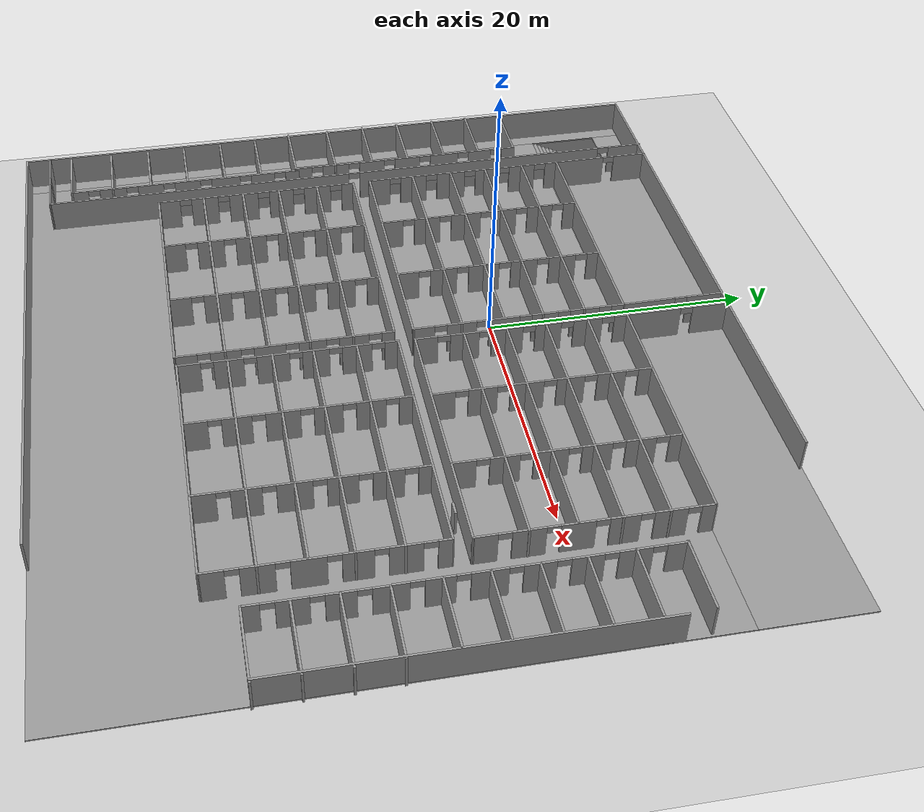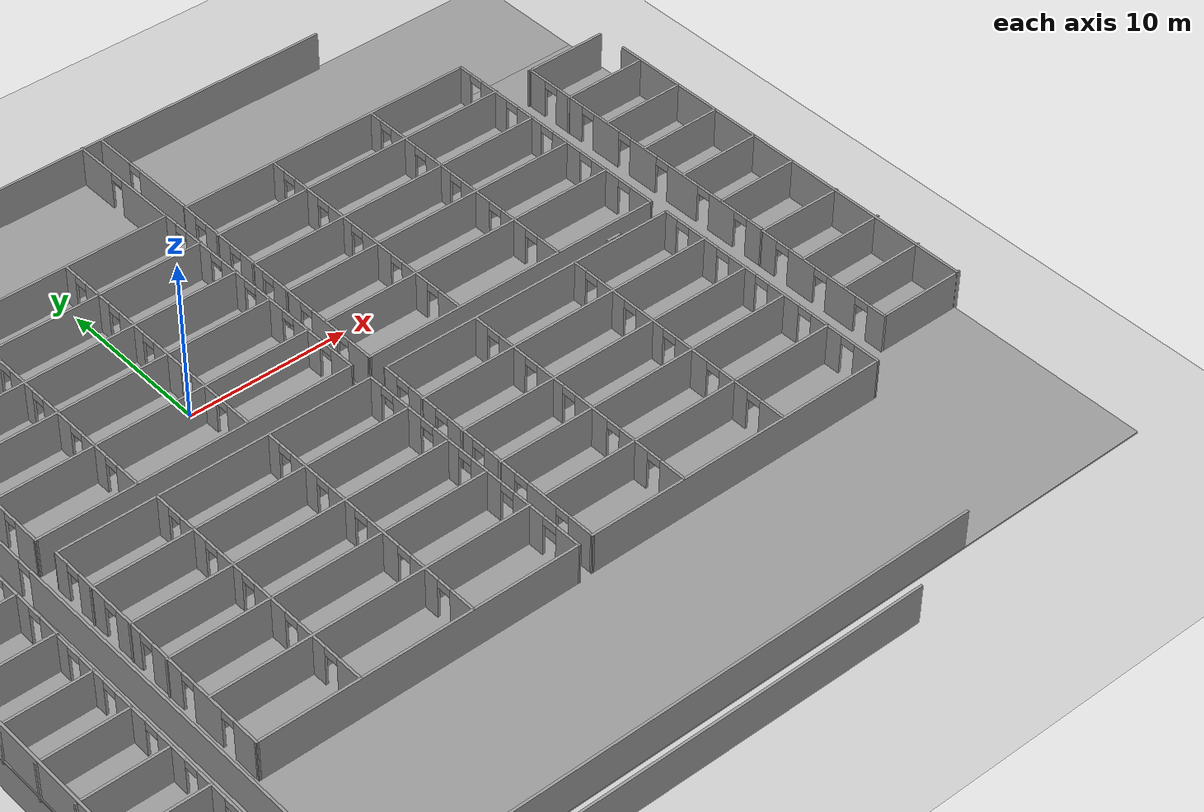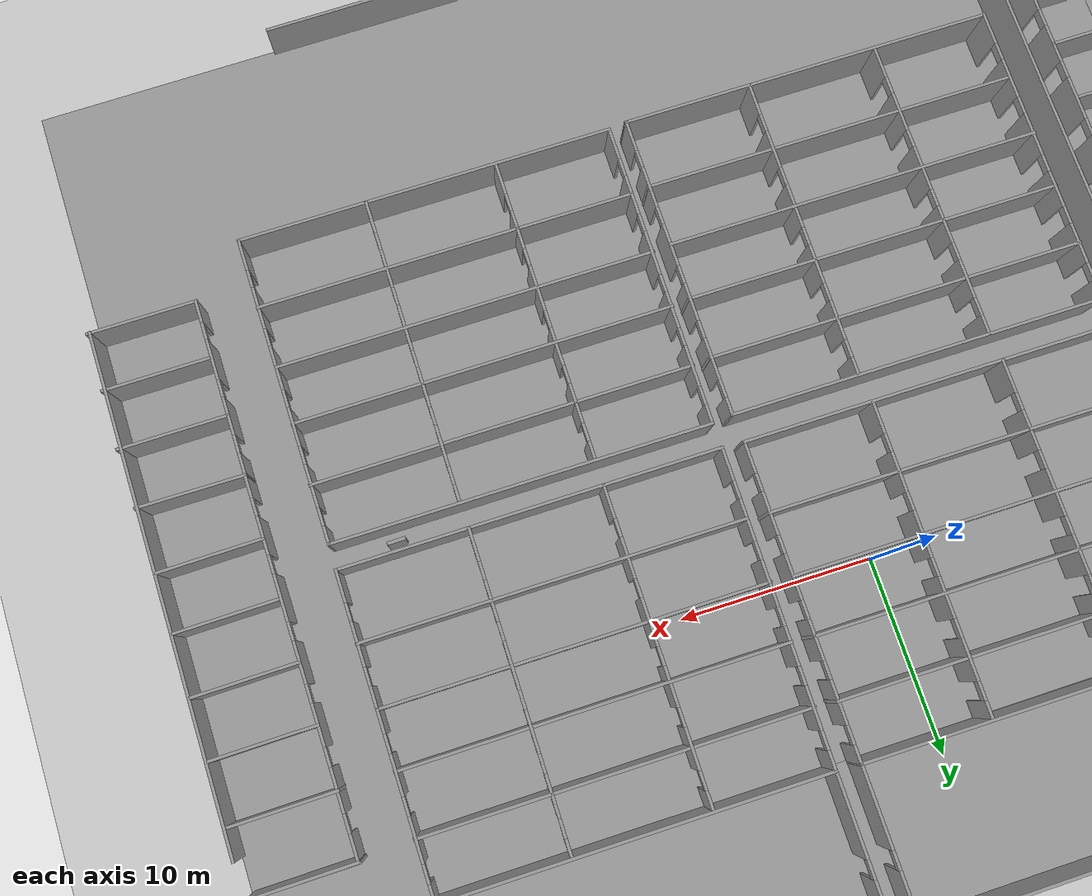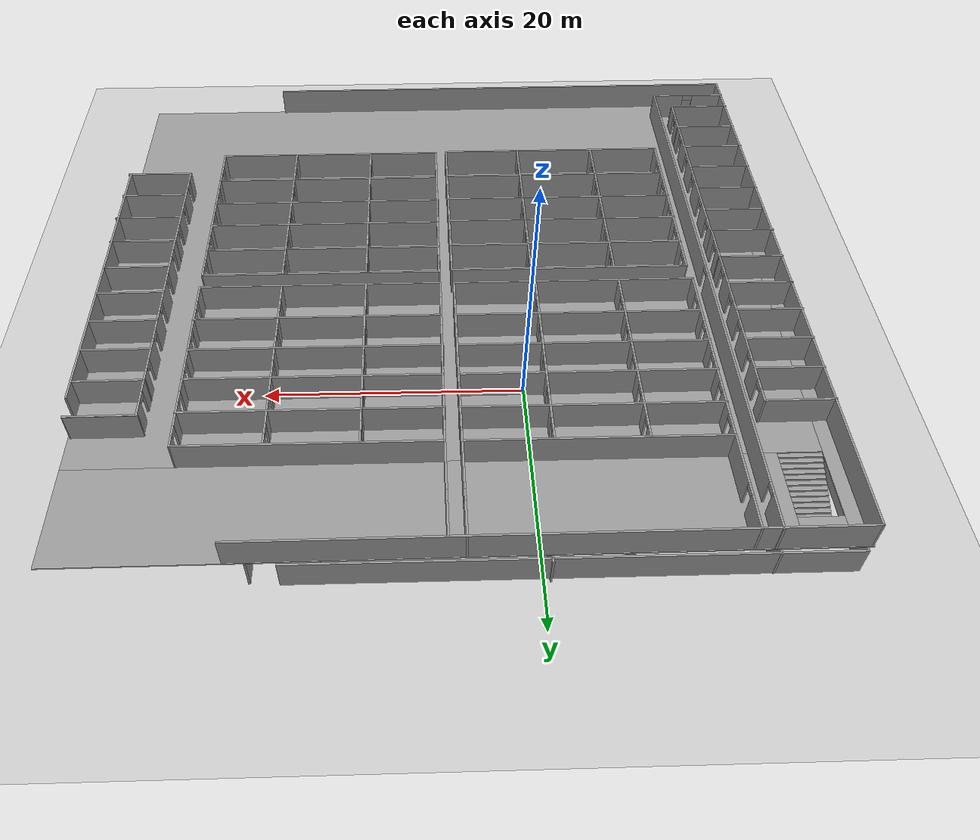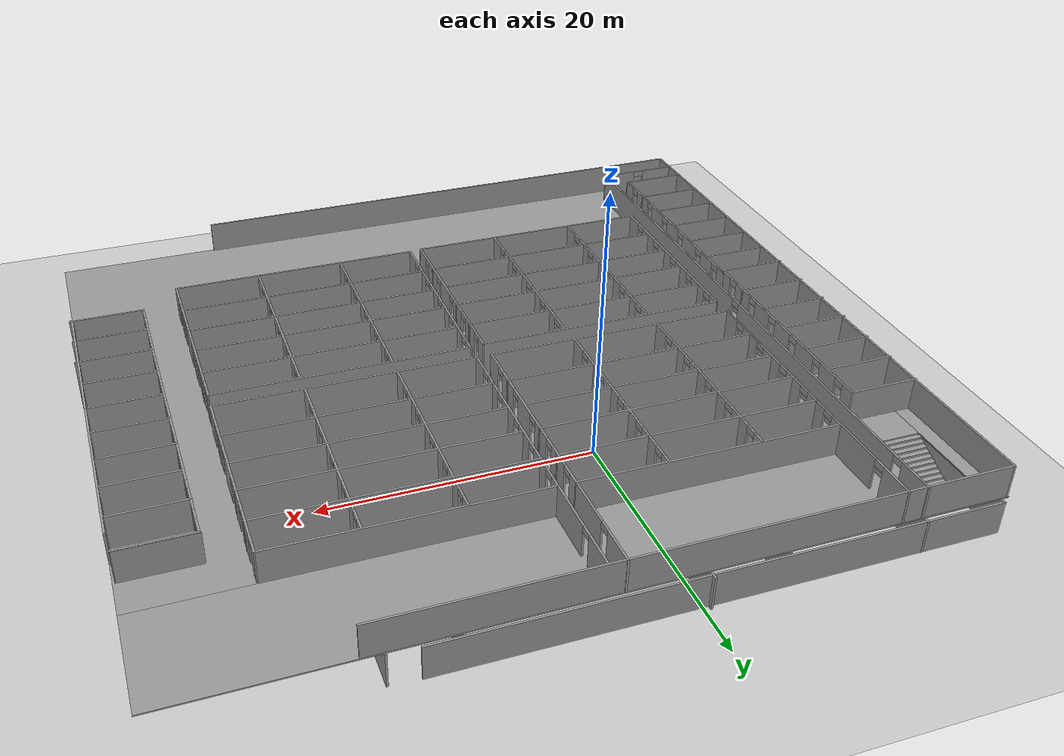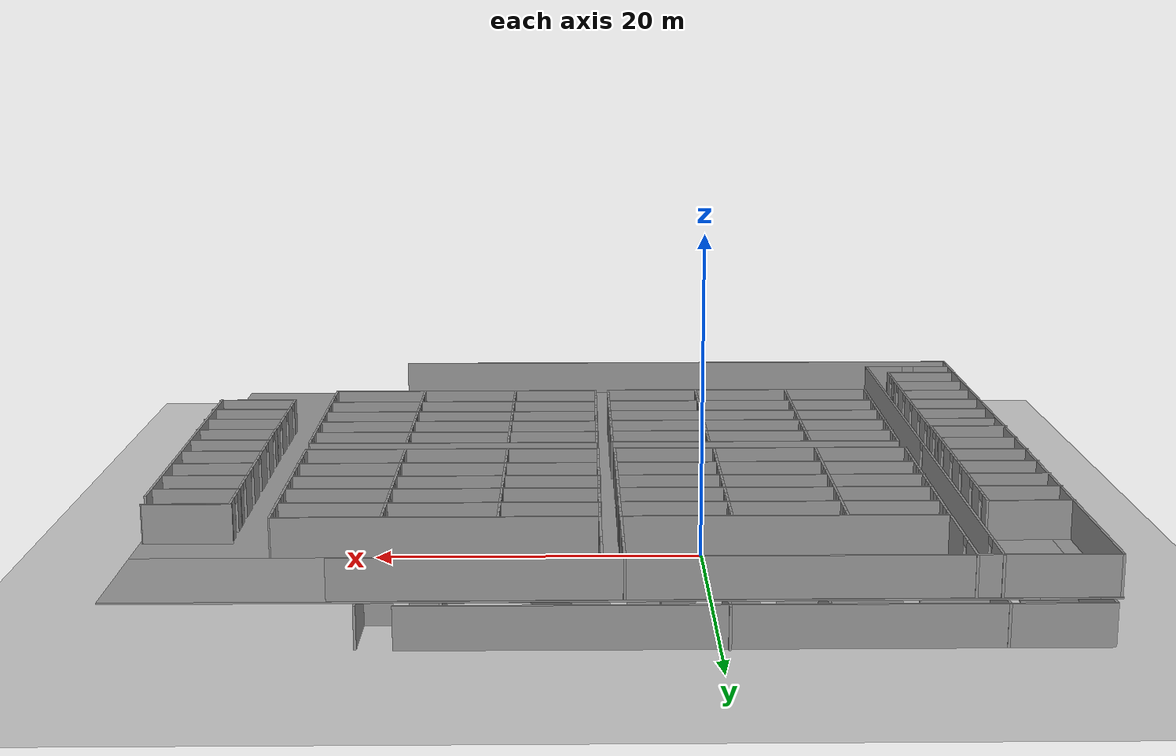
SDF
<sdf version="1.6">
 <world name="default">
  <light name="sun" type="directional">
   <pose>0 0 10 0 -0 0</pose>
   <diffuse>0.8 0.8 0.8 1</diffuse>
   <specular>0.2 0.2 0.2 1</specular>
   <attenuation>
    <range>1000</range>
    <constant>0.9</constant>
    <linear>0.01</linear>
    <quadratic>0.001</quadratic>
   </attenuation>
   <direction>-0.5 0.1 -0.9</direction>
  </light>
  <model name="ground_plane">
   <static>1</static>
   <link name="link">
    <collision name="collision">
     <geometry><plane><normal>0 0 1</normal><size>100 100</size></plane></geometry>
     <surface>
      <contact><collide_bitmask>65535</collide_bitmask></contact>
      <friction><ode><mu>100</mu><mu2>50</mu2></ode></friction>
     </surface>
    </collision>
    <visual name="visual">
     <cast_shadows>0</cast_shadows>
     <geometry><plane><normal>0 0 1</normal><size>100 100</size></plane></geometry>
     <material>
      <script><uri>file://media/materials/scripts/gazebo.material</uri><name>Gazebo/Grey</name></script>
     </material>
    </visual>
   </link>
  </model>
  <gravity>0 0 -9.8</gravity>
  <magnetic_field>6e-06 2.3e-05 -4.2e-05</magnetic_field>
  <atmosphere type="adiabatic"/>
  <physics name="default_physics" default="0" type="ode">
   <max_step_size>0.001</max_step_size>
   <real_time_factor>1</real_time_factor>
   <real_time_update_rate>1000</real_time_update_rate>
  </physics>
  <scene><ambient>0.4 0.4 0.4 1</ambient><background>0.7 0.7 0.7 1</background><shadows>1</shadows></scene>
  <spherical_coordinates>
   <surface_model>EARTH_WGS84</surface_model>
   <latitude_deg>0</latitude_deg>
   <longitude_deg>0</longitude_deg>
   <elevation>0</elevation>
   <heading_deg>0</heading_deg>
  </spherical_coordinates>
  <model name="Level_1">
   <pose>4.42313 -8.87328 0 0 -0 0</pose>
   <link name="Wall_0">
    <collision name="Wall_0_Collision">
     <geometry><box><size>39 0.15 2.5</size></box></geometry>
     <pose>0 0 1.25 0 -0 0</pose>
    </collision>
    <visual name="Wall_0_Visual">
     <pose>0 0 1.25 0 -0 0</pose>
     <geometry><box><size>39 0.15 2.5</size></box></geometry>
     <material>
      <script><uri>file://media/materials/scripts/gazebo.material</uri><name>Gazebo/Grey</name></script>
      <ambient>1 1 1 1</ambient>
     </material>
     <meta><layer>0</layer></meta>
    </visual>
    <pose>-6.1866 -25.3136 0 0 -0 0</pose>
   </link>
   <link name="Wall_101">
    <collision name="Wall_101_Collision">
     <geometry><box><size>4.75 0.15 2.5</size></box></geometry>
     <pose>0 0 1.25 0 -0 0</pose>
    </collision>
    <visual name="Wall_101_Visual">
     <pose>0 0 1.25 0 -0 0</pose>
     <geometry><box><size>4.75 0.15 2.5</size></box></geometry>
     <material>
      <script><uri>file://media/materials/scripts/gazebo.material</uri><name>Gazebo/Grey</name></script>
      <ambient>1 1 1 1</ambient>
     </material>
     <meta><layer>0</layer></meta>
    </visual>
    <pose>7.03487 -4.82871 0 0 -0 2.35619</pose>
   </link>
   <link name="Wall_102">
    <collision name="Wall_102_Collision">
     <geometry><box><size>16.002 0.15 2.5</size></box></geometry>
     <pose>0 0 1.25 0 -0 0</pose>
    </collision>
    <visual name="Wall_102_Visual">
     <pose>0 0 1.25 0 -0 0</pose>
     <geometry><box><size>16.002 0.15 2.5</size></box></geometry>
     <material>
      <script><uri>file://media/materials/scripts/gazebo.material</uri><name>Gazebo/Grey</name></script>
      <ambient>1 1 1 1</ambient>
     </material>
     <meta><layer>0</layer></meta>
    </visual>
    <pose>11.1007 2.31307 0 0 -0 0.769627</pose>
   </link>
   <link name="Wall_103">
    <collision name="Wall_103_Collision">
     <geometry><box><size>6.5 0.15 2.5</size></box></geometry>
     <pose>0 0 1.25 0 -0 0</pose>
    </collision>
    <visual name="Wall_103_Visual">
     <pose>0 0 1.25 0 -0 0</pose>
     <geometry><box><size>6.5 0.15 2.5</size></box></geometry>
     <material>
      <script><uri>file://media/materials/scripts/gazebo.material</uri><name>Gazebo/Grey</name></script>
      <ambient>1 1 1 1</ambient>
     </material>
     <meta><layer>0</layer></meta>
    </visual>
    <pose>16.7929 4.65351 0 0 -0 -1.5708</pose>
   </link>
   <link name="Wall_104">
    <collision name="Wall_104_Collision">
     <geometry><box><size>11.5107 0.15 2.5</size></box></geometry>
     <pose>0 0 1.25 0 -0 0</pose>
    </collision>
    <visual name="Wall_104_Visual">
     <pose>0 0 1.25 0 -0 0</pose>
     <geometry><box><size>11.5107 0.15 2.5</size></box></geometry>
     <material>
      <script><uri>file://media/materials/scripts/gazebo.material</uri><name>Gazebo/Grey</name></script>
      <ambient>1 1 1 1</ambient>
     </material>
     <meta><layer>0</layer></meta>
    </visual>
    <pose>12.7271 -2.48827 0 0 -0 -2.36853</pose>
   </link>
   <link name="Wall_106">
    <collision name="Wall_106_Collision">
     <geometry><box><size>4.5 0.15 2.5</size></box></geometry>
     <pose>0 0 1.25 0 -0 0</pose>
    </collision>
    <visual name="Wall_106_Visual">
     <pose>0 0 1.25 0 -0 0</pose>
     <geometry><box><size>4.5 0.15 2.5</size></box></geometry>
     <material>
      <script><uri>file://media/materials/scripts/gazebo.material</uri><name>Gazebo/Grey</name></script>
      <ambient>1 1 1 1</ambient>
     </material>
     <meta><layer>0</layer></meta>
    </visual>
    <pose>10.7825 -1.28419 0 0 -0 -0.785398</pose>
   </link>
   <link name="Wall_108">
    <collision name="Wall_108_Collision">
     <geometry><box><size>4.5 0.15 2.5</size></box></geometry>
     <pose>0 0 1.25 0 -0 0</pose>
    </collision>
    <visual name="Wall_108_Visual">
     <pose>0 0 1.25 0 -0 0</pose>
     <geometry><box><size>4.5 0.15 2.5</size></box></geometry>
     <material>
      <script><uri>file://media/materials/scripts/gazebo.material</uri><name>Gazebo/Grey</name></script>
      <ambient>1 1 1 1</ambient>
     </material>
     <meta><layer>0</layer></meta>
    </visual>
    <pose>14.9391 2.87236 0 0 -0 -0.785398</pose>
   </link>
   <link name="Wall_11">
    <collision name="Wall_11_Collision">
     <geometry><box><size>25.5 0.15 2.5</size></box></geometry>
     <pose>0 0 1.25 0 -0 0</pose>
    </collision>
    <visual name="Wall_11_Visual">
     <pose>0 0 1.25 0 -0 0</pose>
     <geometry><box><size>25.5 0.15 2.5</size></box></geometry>
     <material>
      <script><uri>file://media/materials/scripts/gazebo.material</uri><name>Gazebo/Grey</name></script>
      <ambient>1 1 1 1</ambient>
     </material>
     <meta><layer>0</layer></meta>
    </visual>
    <pose>25.7176 -0.00926 0 0 -0 -1.5708</pose>
   </link>
   <link name="Wall_110">
    <collision name="Wall_110_Collision">
     <geometry><box><size>5.5 0.15 2.5</size></box></geometry>
     <pose>0 0 1.25 0 -0 0</pose>
    </collision>
    <visual name="Wall_110_Visual">
     <pose>0 0 1.25 0 -0 0</pose>
     <geometry><box><size>5.5 0.15 2.5</size></box></geometry>
     <material>
      <script><uri>file://media/materials/scripts/gazebo.material</uri><name>Gazebo/Grey</name></script>
      <ambient>1 1 1 1</ambient>
     </material>
     <meta><layer>0</layer></meta>
    </visual>
    <pose>22.9256 -2.04053 0 0 -0 3.14159</pose>
   </link>
   <link name="Wall_111">
    <collision name="Wall_111_Collision">
     <geometry><box><size>3.75 0.15 2.5</size></box></geometry>
     <pose>0 0 1.25 0 -0 0</pose>
    </collision>
    <visual name="Wall_111_Visual">
     <pose>0 0 1.25 0 -0 0</pose>
     <geometry><box><size>3.75 0.15 2.5</size></box></geometry>
     <material>
      <script><uri>file://media/materials/scripts/gazebo.material</uri><name>Gazebo/Grey</name></script>
      <ambient>1 1 1 1</ambient>
     </material>
     <meta><layer>0</layer></meta>
    </visual>
    <pose>20.2506 -0.240529 0 0 -0 1.5708</pose>
   </link>
   <link name="Wall_112">
    <collision name="Wall_112_Collision">
     <geometry><box><size>5.5 0.15 2.5</size></box></geometry>
     <pose>0 0 1.25 0 -0 0</pose>
    </collision>
    <visual name="Wall_112_Visual">
     <pose>0 0 1.25 0 -0 0</pose>
     <geometry><box><size>5.5 0.15 2.5</size></box></geometry>
     <material>
      <script><uri>file://media/materials/scripts/gazebo.material</uri><name>Gazebo/Grey</name></script>
      <ambient>1 1 1 1</ambient>
     </material>
     <meta><layer>0</layer></meta>
    </visual>
    <pose>22.9256 1.55947 0 0 -0 0</pose>
   </link>
   <link name="Wall_114">
    <collision name="Wall_114_Collision">
     <geometry><box><size>5.5 0.15 2.5</size></box></geometry>
     <pose>0 0 1.25 0 -0 0</pose>
    </collision>
    <visual name="Wall_114_Visual">
     <pose>0 0 1.25 0 -0 0</pose>
     <geometry><box><size>5.5 0.15 2.5</size></box></geometry>
     <material>
      <script><uri>file://media/materials/scripts/gazebo.material</uri><name>Gazebo/Grey</name></script>
      <ambient>1 1 1 1</ambient>
     </material>
     <meta><layer>0</layer></meta>
    </visual>
    <pose>19.4933 3.69811 0 0 -0 0</pose>
   </link>
   <link name="Wall_115">
    <collision name="Wall_115_Collision">
     <geometry><box><size>4 0.15 2.5</size></box></geometry>
     <pose>0 0 1.25 0 -0 0</pose>
    </collision>
    <visual name="Wall_115_Visual">
     <pose>0 0 1.25 0 -0 0</pose>
     <geometry><box><size>4 0.15 2.5</size></box></geometry>
     <material>
      <script><uri>file://media/materials/scripts/gazebo.material</uri><name>Gazebo/Grey</name></script>
      <ambient>1 1 1 1</ambient>
     </material>
     <meta><layer>0</layer></meta>
    </visual>
    <pose>22.1683 5.62311 0 0 -0 1.5708</pose>
   </link>
   <link name="Wall_116">
    <collision name="Wall_116_Collision">
     <geometry><box><size>5.5 0.15 2.5</size></box></geometry>
     <pose>0 0 1.25 0 -0 0</pose>
    </collision>
    <visual name="Wall_116_Visual">
     <pose>0 0 1.25 0 -0 0</pose>
     <geometry><box><size>5.5 0.15 2.5</size></box></geometry>
     <material>
      <script><uri>file://media/materials/scripts/gazebo.material</uri><name>Gazebo/Grey</name></script>
      <ambient>1 1 1 1</ambient>
     </material>
     <meta><layer>0</layer></meta>
    </visual>
    <pose>19.4933 7.54811 0 0 -0 3.14159</pose>
   </link>
   <link name="Wall_118">
    <collision name="Wall_118_Collision">
     <geometry><box><size>5.39027 0.15 2.5</size></box></geometry>
     <pose>0 0 1.25 0 -0 0</pose>
    </collision>
    <visual name="Wall_118_Visual">
     <pose>0 0 1.25 0 -0 0</pose>
     <geometry><box><size>5.39027 0.15 2.5</size></box></geometry>
     <material>
      <script><uri>file://media/materials/scripts/gazebo.material</uri><name>Gazebo/Grey</name></script>
      <ambient>1 1 1 1</ambient>
     </material>
     <meta><layer>0</layer></meta>
    </visual>
    <pose>-2.48405 19.5667 0 0 -0 1.11332</pose>
   </link>
   <link name="Wall_119">
    <pose>1.09822 21.9175 0 0 -0 0</pose>
    <visual name="Wall_119_Visual_0">
     <pose>-1.54856 0 1.25 0 -0 0</pose>
     <geometry><box><size>1.90287 0.15 2.5</size></box></geometry>
     <material>
      <script><uri>file://media/materials/scripts/gazebo.material</uri><name>Gazebo/Grey</name></script>
      <ambient>1 1 1 1</ambient>
     </material>
     <meta><layer>0</layer></meta>
    </visual>
    <collision name="Wall_119_Collision_0">
     <geometry><box><size>1.90287 0.15 2.5</size></box></geometry>
     <pose>-1.54856 0 1.25 0 -0 0</pose>
    </collision>
    <visual name="Wall_119_Visual_1">
     <pose>1.40144 0 1.25 0 -0 0</pose>
     <geometry><box><size>2.19713 0.15 2.5</size></box></geometry>
     <material>
      <script><uri>file://media/materials/scripts/gazebo.material</uri><name>Gazebo/Grey</name></script>
      <ambient>1 1 1 1</ambient>
     </material>
     <meta><layer>0</layer></meta>
    </visual>
    <collision name="Wall_119_Collision_1">
     <geometry><box><size>2.19713 0.15 2.5</size></box></geometry>
     <pose>1.40144 0 1.25 0 -0 0</pose>
    </collision>
    <visual name="Wall_119_Visual_2">
     <pose>-0.147126 0 2.25 0 -0 0</pose>
     <geometry><box><size>0.9 0.15 0.5</size></box></geometry>
     <material>
      <script><uri>file://media/materials/scripts/gazebo.material</uri><name>Gazebo/Grey</name></script>
      <ambient>1 1 1 1</ambient>
     </material>
     <meta><layer>0</layer></meta>
    </visual>
    <collision name="Wall_119_Collision_2">
     <geometry><box><size>0.9 0.15 0.5</size></box></geometry>
     <pose>-0.147126 0 2.25 0 -0 0</pose>
    </collision>
   </link>
   <link name="Wall_120">
    <collision name="Wall_120_Collision">
     <geometry><box><size>5.51815 0.15 2.5</size></box></geometry>
     <pose>0 0 1.25 0 -0 0</pose>
    </collision>
    <visual name="Wall_120_Visual">
     <pose>0 0 1.25 0 -0 0</pose>
     <geometry><box><size>5.51815 0.15 2.5</size></box></geometry>
     <material>
      <script><uri>file://media/materials/scripts/gazebo.material</uri><name>Gazebo/Grey</name></script>
      <ambient>1 1 1 1</ambient>
     </material>
     <meta><layer>0</layer></meta>
    </visual>
    <pose>4.75085 19.5306 0 0 -0 -1.09575</pose>
   </link>
   <link name="Wall_122">
    <collision name="Wall_122_Collision">
     <geometry><box><size>4 0.15 2.5</size></box></geometry>
     <pose>0 0 1.25 0 -0 0</pose>
    </collision>
    <visual name="Wall_122_Visual">
     <pose>0 0 1.25 0 -0 0</pose>
     <geometry><box><size>4 0.15 2.5</size></box></geometry>
     <material>
      <script><uri>file://media/materials/scripts/gazebo.material</uri><name>Gazebo/Grey</name></script>
      <ambient>1 1 1 1</ambient>
     </material>
     <meta><layer>0</layer></meta>
    </visual>
    <pose>10.4775 22.9915 0 0 -0 -1.5708</pose>
   </link>
   <link name="Wall_123">
    <pose>12.7775 21.0665 0 0 -0 0</pose>
    <visual name="Wall_123_Visual_0">
     <pose>-1.33768 0 1.25 0 -0 0</pose>
     <geometry><box><size>2.07464 0.15 2.5</size></box></geometry>
     <material>
      <script><uri>file://media/materials/scripts/gazebo.material</uri><name>Gazebo/Grey</name></script>
      <ambient>1 1 1 1</ambient>
     </material>
     <meta><layer>0</layer></meta>
    </visual>
    <collision name="Wall_123_Collision_0">
     <geometry><box><size>2.07464 0.15 2.5</size></box></geometry>
     <pose>-1.33768 0 1.25 0 -0 0</pose>
    </collision>
    <visual name="Wall_123_Visual_1">
     <pose>1.48732 0 1.25 0 -0 0</pose>
     <geometry><box><size>1.77536 0.15 2.5</size></box></geometry>
     <material>
      <script><uri>file://media/materials/scripts/gazebo.material</uri><name>Gazebo/Grey</name></script>
      <ambient>1 1 1 1</ambient>
     </material>
     <meta><layer>0</layer></meta>
    </visual>
    <collision name="Wall_123_Collision_1">
     <geometry><box><size>1.77536 0.15 2.5</size></box></geometry>
     <pose>1.48732 0 1.25 0 -0 0</pose>
    </collision>
    <visual name="Wall_123_Visual_2">
     <pose>0.149637 0 2.25 0 -0 0</pose>
     <geometry><box><size>0.9 0.15 0.5</size></box></geometry>
     <material>
      <script><uri>file://media/materials/scripts/gazebo.material</uri><name>Gazebo/Grey</name></script>
      <ambient>1 1 1 1</ambient>
     </material>
     <meta><layer>0</layer></meta>
    </visual>
    <collision name="Wall_123_Collision_2">
     <geometry><box><size>0.9 0.15 0.5</size></box></geometry>
     <pose>0.149637 0 2.25 0 -0 0</pose>
    </collision>
   </link>
   <link name="Wall_124">
    <collision name="Wall_124_Collision">
     <geometry><box><size>4 0.15 2.5</size></box></geometry>
     <pose>0 0 1.25 0 -0 0</pose>
    </collision>
    <visual name="Wall_124_Visual">
     <pose>0 0 1.25 0 -0 0</pose>
     <geometry><box><size>4 0.15 2.5</size></box></geometry>
     <material>
      <script><uri>file://media/materials/scripts/gazebo.material</uri><name>Gazebo/Grey</name></script>
      <ambient>1 1 1 1</ambient>
     </material>
     <meta><layer>0</layer></meta>
    </visual>
    <pose>15.0775 22.9915 0 0 -0 1.5708</pose>
   </link>
   <link name="Wall_126">
    <collision name="Wall_126_Collision">
     <geometry><box><size>4.75 0.15 2.5</size></box></geometry>
     <pose>0 0 1.25 0 -0 0</pose>
    </collision>
    <visual name="Wall_126_Visual">
     <pose>0 0 1.25 0 -0 0</pose>
     <geometry><box><size>4.75 0.15 2.5</size></box></geometry>
     <material>
      <script><uri>file://media/materials/scripts/gazebo.material</uri><name>Gazebo/Grey</name></script>
      <ambient>1 1 1 1</ambient>
     </material>
     <meta><layer>0</layer></meta>
    </visual>
    <pose>-19.8825 22.7636 0 0 -0 -1.5708</pose>
   </link>
   <link name="Wall_127">
    <pose>-15.0825 20.4636 0 0 -0 0</pose>
    <visual name="Wall_127_Visual_0">
     <pose>-2.83636 0 1.25 0 -0 0</pose>
     <geometry><box><size>4.07728 0.15 2.5</size></box></geometry>
     <material>
      <script><uri>file://media/materials/scripts/gazebo.material</uri><name>Gazebo/Grey</name></script>
      <ambient>1 1 1 1</ambient>
     </material>
     <meta><layer>0</layer></meta>
    </visual>
    <collision name="Wall_127_Collision_0">
     <geometry><box><size>4.07728 0.15 2.5</size></box></geometry>
     <pose>-2.83636 0 1.25 0 -0 0</pose>
    </collision>
    <visual name="Wall_127_Visual_1">
     <pose>2.48864 0 1.25 0 -0 0</pose>
     <geometry><box><size>4.77272 0.15 2.5</size></box></geometry>
     <material>
      <script><uri>file://media/materials/scripts/gazebo.material</uri><name>Gazebo/Grey</name></script>
      <ambient>1 1 1 1</ambient>
     </material>
     <meta><layer>0</layer></meta>
    </visual>
    <collision name="Wall_127_Collision_1">
     <geometry><box><size>4.77272 0.15 2.5</size></box></geometry>
     <pose>2.48864 0 1.25 0 -0 0</pose>
    </collision>
    <visual name="Wall_127_Visual_2">
     <pose>-0.347718 0 2.25 0 -0 0</pose>
     <geometry><box><size>0.9 0.15 0.5</size></box></geometry>
     <material>
      <script><uri>file://media/materials/scripts/gazebo.material</uri><name>Gazebo/Grey</name></script>
      <ambient>1 1 1 1</ambient>
     </material>
     <meta><layer>0</layer></meta>
    </visual>
    <collision name="Wall_127_Collision_2">
     <geometry><box><size>0.9 0.15 0.5</size></box></geometry>
     <pose>-0.347718 0 2.25 0 -0 0</pose>
    </collision>
   </link>
   <link name="Wall_128">
    <collision name="Wall_128_Collision">
     <geometry><box><size>4.5 0.15 2.5</size></box></geometry>
     <pose>0 0 1.25 0 -0 0</pose>
    </collision>
    <visual name="Wall_128_Visual">
     <pose>0 0 1.25 0 -0 0</pose>
     <geometry><box><size>4.5 0.15 2.5</size></box></geometry>
     <material>
      <script><uri>file://media/materials/scripts/gazebo.material</uri><name>Gazebo/Grey</name></script>
      <ambient>1 1 1 1</ambient>
     </material>
     <meta><layer>0</layer></meta>
    </visual>
    <pose>-10.2825 22.6386 0 0 -0 1.5708</pose>
   </link>
   <link name="Wall_13">
    <collision name="Wall_13_Collision">
     <geometry><box><size>4.75 0.15 2.5</size></box></geometry>
     <pose>0 0 1.25 0 -0 0</pose>
    </collision>
    <visual name="Wall_13_Visual">
     <pose>0 0 1.25 0 -0 0</pose>
     <geometry><box><size>4.75 0.15 2.5</size></box></geometry>
     <material>
      <script><uri>file://media/materials/scripts/gazebo.material</uri><name>Gazebo/Grey</name></script>
      <ambient>1 1 1 1</ambient>
     </material>
     <meta><layer>0</layer></meta>
    </visual>
    <pose>-23.394 -19.4874 0 0 -0 0</pose>
   </link>
   <link name="Wall_130">
    <pose>-7.60749 20.4636 0 0 -0 0</pose>
    <visual name="Wall_130_Visual_0">
     <pose>-1.51233 0 1.25 0 -0 0</pose>
     <geometry><box><size>2.47533 0.15 2.5</size></box></geometry>
     <material>
      <script><uri>file://media/materials/scripts/gazebo.material</uri><name>Gazebo/Grey</name></script>
      <ambient>1 1 1 1</ambient>
     </material>
     <meta><layer>0</layer></meta>
    </visual>
    <collision name="Wall_130_Collision_0">
     <geometry><box><size>2.47533 0.15 2.5</size></box></geometry>
     <pose>-1.51233 0 1.25 0 -0 0</pose>
    </collision>
    <visual name="Wall_130_Visual_1">
     <pose>1.68767 0 1.25 0 -0 0</pose>
     <geometry><box><size>2.12467 0.15 2.5</size></box></geometry>
     <material>
      <script><uri>file://media/materials/scripts/gazebo.material</uri><name>Gazebo/Grey</name></script>
      <ambient>1 1 1 1</ambient>
     </material>
     <meta><layer>0</layer></meta>
    </visual>
    <collision name="Wall_130_Collision_1">
     <geometry><box><size>2.12467 0.15 2.5</size></box></geometry>
     <pose>1.68767 0 1.25 0 -0 0</pose>
    </collision>
    <visual name="Wall_130_Visual_2">
     <pose>0.175332 0 2.25 0 -0 0</pose>
     <geometry><box><size>0.9 0.15 0.5</size></box></geometry>
     <material>
      <script><uri>file://media/materials/scripts/gazebo.material</uri><name>Gazebo/Grey</name></script>
      <ambient>1 1 1 1</ambient>
     </material>
     <meta><layer>0</layer></meta>
    </visual>
    <collision name="Wall_130_Collision_2">
     <geometry><box><size>0.9 0.15 0.5</size></box></geometry>
     <pose>0.175332 0 2.25 0 -0 0</pose>
    </collision>
   </link>
   <link name="Wall_131">
    <collision name="Wall_131_Collision">
     <geometry><box><size>5 0.15 2.5</size></box></geometry>
     <pose>0 0 1.25 0 -0 0</pose>
    </collision>
    <visual name="Wall_131_Visual">
     <pose>0 0 1.25 0 -0 0</pose>
     <geometry><box><size>5 0.15 2.5</size></box></geometry>
     <material>
      <script><uri>file://media/materials/scripts/gazebo.material</uri><name>Gazebo/Grey</name></script>
      <ambient>1 1 1 1</ambient>
     </material>
     <meta><layer>0</layer></meta>
    </visual>
    <pose>-4.93249 22.8886 0 0 -0 1.5708</pose>
   </link>
   <link name="Wall_133">
    <pose>9.44685 17.3898 0 0 -0 0.021977</pose>
    <visual name="Wall_133_Visual_0">
     <pose>-1.07074 0 1.25 0 -0 0</pose>
     <geometry><box><size>0.736662 0.15 2.5</size></box></geometry>
     <material>
      <script><uri>file://media/materials/scripts/gazebo.material</uri><name>Gazebo/Grey</name></script>
      <ambient>1 1 1 1</ambient>
     </material>
     <meta><layer>0</layer></meta>
    </visual>
    <collision name="Wall_133_Collision_0">
     <geometry><box><size>0.736662 0.15 2.5</size></box></geometry>
     <pose>-1.07074 0 1.25 0 -0 0</pose>
    </collision>
    <visual name="Wall_133_Visual_1">
     <pose>0.818331 0 1.25 0 -0 0</pose>
     <geometry><box><size>1.24147 0.15 2.5</size></box></geometry>
     <material>
      <script><uri>file://media/materials/scripts/gazebo.material</uri><name>Gazebo/Grey</name></script>
      <ambient>1 1 1 1</ambient>
     </material>
     <meta><layer>0</layer></meta>
    </visual>
    <collision name="Wall_133_Collision_1">
     <geometry><box><size>1.24147 0.15 2.5</size></box></geometry>
     <pose>0.818331 0 1.25 0 -0 0</pose>
    </collision>
    <visual name="Wall_133_Visual_2">
     <pose>-0.252406 0 2.25 0 -0 0</pose>
     <geometry><box><size>0.9 0.15 0.5</size></box></geometry>
     <material>
      <script><uri>file://media/materials/scripts/gazebo.material</uri><name>Gazebo/Grey</name></script>
      <ambient>1 1 1 1</ambient>
     </material>
     <meta><layer>0</layer></meta>
    </visual>
    <collision name="Wall_133_Collision_2">
     <geometry><box><size>0.9 0.15 0.5</size></box></geometry>
     <pose>-0.252406 0 2.25 0 -0 0</pose>
    </collision>
   </link>
   <link name="Wall_135">
    <collision name="Wall_135_Collision">
     <geometry><box><size>3.52284 0.15 2.5</size></box></geometry>
     <pose>0 0 1.25 0 -0 0</pose>
    </collision>
    <visual name="Wall_135_Visual">
     <pose>0 0 1.25 0 -0 0</pose>
     <geometry><box><size>3.52284 0.15 2.5</size></box></geometry>
     <material>
      <script><uri>file://media/materials/scripts/gazebo.material</uri><name>Gazebo/Grey</name></script>
      <ambient>1 1 1 1</ambient>
     </material>
     <meta><layer>0</layer></meta>
    </visual>
    <pose>16.8454 9.23414 0 0 -0 -1.58689</pose>
   </link>
   <link name="Wall_16">
    <collision name="Wall_16_Collision">
     <geometry><box><size>6.4039 0.15 2.5</size></box></geometry>
     <pose>0 0 1.25 0 -0 0</pose>
    </collision>
    <visual name="Wall_16_Visual">
     <pose>0 0 1.25 0 -0 0</pose>
     <geometry><box><size>6.4039 0.15 2.5</size></box></geometry>
     <material>
      <script><uri>file://media/materials/scripts/gazebo.material</uri><name>Gazebo/Grey</name></script>
      <ambient>1 1 1 1</ambient>
     </material>
     <meta><layer>0</layer></meta>
    </visual>
    <pose>-21.0744 -16.3606 0 0 -0 1.56453</pose>
   </link>
   <link name="Wall_17">
    <collision name="Wall_17_Collision">
     <geometry><box><size>4.8124 0.15 2.5</size></box></geometry>
     <pose>0 0 1.25 0 -0 0</pose>
    </collision>
    <visual name="Wall_17_Visual">
     <pose>0 0 1.25 0 -0 0</pose>
     <geometry><box><size>4.8124 0.15 2.5</size></box></geometry>
     <material>
      <script><uri>file://media/materials/scripts/gazebo.material</uri><name>Gazebo/Grey</name></script>
      <ambient>1 1 1 1</ambient>
     </material>
     <meta><layer>0</layer></meta>
    </visual>
    <pose>-23.3858 -13.2564 0 0 -0 -3.13184</pose>
   </link>
   <link name="Wall_19">
    <collision name="Wall_19_Collision">
     <geometry><box><size>16.0443 0.15 2.5</size></box></geometry>
     <pose>0 0 1.25 0 -0 0</pose>
    </collision>
    <visual name="Wall_19_Visual">
     <pose>0 0 1.25 0 -0 0</pose>
     <geometry><box><size>16.0443 0.15 2.5</size></box></geometry>
     <material>
      <script><uri>file://media/materials/scripts/gazebo.material</uri><name>Gazebo/Grey</name></script>
      <ambient>1 1 1 1</ambient>
     </material>
     <meta><layer>0</layer></meta>
    </visual>
    <pose>-9.84438 -17.3407 0 0 -0 0.010778</pose>
   </link>
   <link name="Wall_2">
    <collision name="Wall_2_Collision">
     <geometry><box><size>4.25 0.15 2.5</size></box></geometry>
     <pose>0 0 1.25 0 -0 0</pose>
    </collision>
    <visual name="Wall_2_Visual">
     <pose>0 0 1.25 0 -0 0</pose>
     <geometry><box><size>4.25 0.15 2.5</size></box></geometry>
     <material>
      <script><uri>file://media/materials/scripts/gazebo.material</uri><name>Gazebo/Grey</name></script>
      <ambient>1 1 1 1</ambient>
     </material>
     <meta><layer>0</layer></meta>
    </visual>
    <pose>-17.939 -23.2636 0 0 -0 1.5708</pose>
   </link>
   <link name="Wall_20">
    <collision name="Wall_20_Collision">
     <geometry><box><size>11.25 0.15 2.5</size></box></geometry>
     <pose>0 0 1.25 0 -0 0</pose>
    </collision>
    <visual name="Wall_20_Visual">
     <pose>0 0 1.25 0 -0 0</pose>
     <geometry><box><size>11.25 0.15 2.5</size></box></geometry>
     <material>
      <script><uri>file://media/materials/scripts/gazebo.material</uri><name>Gazebo/Grey</name></script>
      <ambient>1 1 1 1</ambient>
     </material>
     <meta><layer>0</layer></meta>
    </visual>
    <pose>2.02676 -13.3306 0 0 -0 0.785398</pose>
   </link>
   <link name="Wall_21">
    <collision name="Wall_21_Collision">
     <geometry><box><size>4.70633 0.15 2.5</size></box></geometry>
     <pose>0 0 1.25 0 -0 0</pose>
    </collision>
    <visual name="Wall_21_Visual">
     <pose>0 0 1.25 0 -0 0</pose>
     <geometry><box><size>4.70633 0.15 2.5</size></box></geometry>
     <material>
      <script><uri>file://media/materials/scripts/gazebo.material</uri><name>Gazebo/Grey</name></script>
      <ambient>1 1 1 1</ambient>
     </material>
     <meta><layer>0</layer></meta>
    </visual>
    <pose>4.35354 -7.78211 0 0 -0 2.348</pose>
   </link>
   <link name="Wall_22">
    <collision name="Wall_22_Collision">
     <geometry><box><size>16.0969 0.15 2.5</size></box></geometry>
     <pose>0 0 1.25 0 -0 0</pose>
    </collision>
    <visual name="Wall_22_Visual">
     <pose>0 0 1.25 0 -0 0</pose>
     <geometry><box><size>16.0969 0.15 2.5</size></box></geometry>
     <material>
      <script><uri>file://media/materials/scripts/gazebo.material</uri><name>Gazebo/Grey</name></script>
      <ambient>1 1 1 1</ambient>
     </material>
     <meta><layer>0</layer></meta>
    </visual>
    <pose>-2.91193 -11.7662 0 0 -0 -2.36149</pose>
   </link>
   <link name="Wall_24">
    <collision name="Wall_24_Collision">
     <geometry><box><size>9 0.15 2.5</size></box></geometry>
     <pose>0 0 1.25 0 -0 0</pose>
    </collision>
    <visual name="Wall_24_Visual">
     <pose>0 0 1.25 0 -0 0</pose>
     <geometry><box><size>9 0.15 2.5</size></box></geometry>
     <material>
      <script><uri>file://media/materials/scripts/gazebo.material</uri><name>Gazebo/Grey</name></script>
      <ambient>1 1 1 1</ambient>
     </material>
     <meta><layer>0</layer></meta>
    </visual>
    <pose>-12.3218 -12.1261 0 0 -0 2.35619</pose>
   </link>
   <link name="Wall_25">
    <collision name="Wall_25_Collision">
     <geometry><box><size>14.9952 0.15 2.5</size></box></geometry>
     <pose>0 0 1.25 0 -0 0</pose>
    </collision>
    <visual name="Wall_25_Visual">
     <pose>0 0 1.25 0 -0 0</pose>
     <geometry><box><size>14.9952 0.15 2.5</size></box></geometry>
     <material>
      <script><uri>file://media/materials/scripts/gazebo.material</uri><name>Gazebo/Grey</name></script>
      <ambient>1 1 1 1</ambient>
     </material>
     <meta><layer>0</layer></meta>
    </visual>
    <pose>-10.2245 -3.72644 0 0 -0 0.789636</pose>
   </link>
   <link name="Wall_26">
    <collision name="Wall_26_Collision">
     <geometry><box><size>9.09192 0.15 2.5</size></box></geometry>
     <pose>0 0 1.25 0 -0 0</pose>
    </collision>
    <visual name="Wall_26_Visual">
     <pose>0 0 1.25 0 -0 0</pose>
     <geometry><box><size>9.09192 0.15 2.5</size></box></geometry>
     <material>
      <script><uri>file://media/materials/scripts/gazebo.material</uri><name>Gazebo/Grey</name></script>
      <ambient>1 1 1 1</ambient>
     </material>
     <meta><layer>0</layer></meta>
    </visual>
    <pose>-1.88972 -1.66923 0 0 -0 -0.802016</pose>
   </link>
   <link name="Wall_27">
    <collision name="Wall_27_Collision">
     <geometry><box><size>14.75 0.15 2.5</size></box></geometry>
     <pose>0 0 1.25 0 -0 0</pose>
    </collision>
    <visual name="Wall_27_Visual">
     <pose>0 0 1.25 0 -0 0</pose>
     <geometry><box><size>14.75 0.15 2.5</size></box></geometry>
     <material>
      <script><uri>file://media/materials/scripts/gazebo.material</uri><name>Gazebo/Grey</name></script>
      <ambient>1 1 1 1</ambient>
     </material>
     <meta><layer>0</layer></meta>
    </visual>
    <pose>-3.94634 -10.0479 0 0 -0 -2.35619</pose>
   </link>
   <link name="Wall_29">
    <collision name="Wall_29_Collision">
     <geometry><box><size>14.8537 0.15 2.5</size></box></geometry>
     <pose>0 0 1.25 0 -0 0</pose>
    </collision>
    <visual name="Wall_29_Visual">
     <pose>0 0 1.25 0 -0 0</pose>
     <geometry><box><size>14.8537 0.15 2.5</size></box></geometry>
     <material>
      <script><uri>file://media/materials/scripts/gazebo.material</uri><name>Gazebo/Grey</name></script>
      <ambient>1 1 1 1</ambient>
     </material>
     <meta><layer>0</layer></meta>
    </visual>
    <pose>-17.8589 -10.0748 0 0 -0 1.58002</pose>
   </link>
   <link name="Wall_30">
    <collision name="Wall_30_Collision">
     <geometry><box><size>12.25 0.15 2.5</size></box></geometry>
     <pose>0 0 1.25 0 -0 0</pose>
    </collision>
    <visual name="Wall_30_Visual">
     <pose>0 0 1.25 0 -0 0</pose>
     <geometry><box><size>12.25 0.15 2.5</size></box></geometry>
     <material>
      <script><uri>file://media/materials/scripts/gazebo.material</uri><name>Gazebo/Grey</name></script>
      <ambient>1 1 1 1</ambient>
     </material>
     <meta><layer>0</layer></meta>
    </visual>
    <pose>-13.6487 1.55476 0 0 -0 0.785398</pose>
   </link>
   <link name="Wall_31">
    <collision name="Wall_31_Collision">
     <geometry><box><size>4.25 0.15 2.5</size></box></geometry>
     <pose>0 0 1.25 0 -0 0</pose>
    </collision>
    <visual name="Wall_31_Visual">
     <pose>0 0 1.25 0 -0 0</pose>
     <geometry><box><size>4.25 0.15 2.5</size></box></geometry>
     <material>
      <script><uri>file://media/materials/scripts/gazebo.material</uri><name>Gazebo/Grey</name></script>
      <ambient>1 1 1 1</ambient>
     </material>
     <meta><layer>0</layer></meta>
    </visual>
    <pose>-7.9211 4.38319 0 0 -0 -0.785398</pose>
   </link>
   <link name="Wall_33">
    <collision name="Wall_33_Collision">
     <geometry><box><size>16.25 0.15 2.5</size></box></geometry>
     <pose>0 0 1.25 0 -0 0</pose>
    </collision>
    <visual name="Wall_33_Visual">
     <pose>0 0 1.25 0 -0 0</pose>
     <geometry><box><size>16.25 0.15 2.5</size></box></geometry>
     <material>
      <script><uri>file://media/materials/scripts/gazebo.material</uri><name>Gazebo/Grey</name></script>
      <ambient>1 1 1 1</ambient>
     </material>
     <meta><layer>0</layer></meta>
    </visual>
    <pose>-12.1637 -2.75859 0 0 -0 -2.35619</pose>
   </link>
   <link name="Wall_35">
    <collision name="Wall_35_Collision">
     <geometry><box><size>22.5 0.15 2.5</size></box></geometry>
     <pose>0 0 1.25 0 -0 0</pose>
    </collision>
    <visual name="Wall_35_Visual">
     <pose>0 0 1.25 0 -0 0</pose>
     <geometry><box><size>22.5 0.15 2.5</size></box></geometry>
     <material>
      <script><uri>file://media/materials/scripts/gazebo.material</uri><name>Gazebo/Grey</name></script>
      <ambient>1 1 1 1</ambient>
     </material>
     <meta><layer>0</layer></meta>
    </visual>
    <pose>-9.90046 -9.53573 0 0 -0 0.785398</pose>
   </link>
   <link name="Wall_37">
    <collision name="Wall_37_Collision">
     <geometry><box><size>4.25 0.15 2.5</size></box></geometry>
     <pose>0 0 1.25 0 -0 0</pose>
    </collision>
    <visual name="Wall_37_Visual">
     <pose>0 0 1.25 0 -0 0</pose>
     <geometry><box><size>4.25 0.15 2.5</size></box></geometry>
     <material>
      <script><uri>file://media/materials/scripts/gazebo.material</uri><name>Gazebo/Grey</name></script>
      <ambient>1 1 1 1</ambient>
     </material>
     <meta><layer>0</layer></meta>
    </visual>
    <pose>-15.5996 -3.27281 0 0 -0 -0.785398</pose>
   </link>
   <link name="Wall_39">
    <collision name="Wall_39_Collision">
     <geometry><box><size>4.25 0.15 2.5</size></box></geometry>
     <pose>0 0 1.25 0 -0 0</pose>
    </collision>
    <visual name="Wall_39_Visual">
     <pose>0 0 1.25 0 -0 0</pose>
     <geometry><box><size>4.25 0.15 2.5</size></box></geometry>
     <material>
      <script><uri>file://media/materials/scripts/gazebo.material</uri><name>Gazebo/Grey</name></script>
      <ambient>1 1 1 1</ambient>
     </material>
     <meta><layer>0</layer></meta>
    </visual>
    <pose>-11.8668 0.459992 0 0 -0 -0.785398</pose>
   </link>
   <link name="Wall_41">
    <collision name="Wall_41_Collision">
     <geometry><box><size>9 0.15 2.5</size></box></geometry>
     <pose>0 0 1.25 0 -0 0</pose>
    </collision>
    <visual name="Wall_41_Visual">
     <pose>0 0 1.25 0 -0 0</pose>
     <geometry><box><size>9 0.15 2.5</size></box></geometry>
     <material>
      <script><uri>file://media/materials/scripts/gazebo.material</uri><name>Gazebo/Grey</name></script>
      <ambient>1 1 1 1</ambient>
     </material>
     <meta><layer>0</layer></meta>
    </visual>
    <pose>-9.59981 -9.30713 0 0 -0 -0.785398</pose>
   </link>
   <link name="Wall_43">
    <collision name="Wall_43_Collision">
     <geometry><box><size>9 0.15 2.5</size></box></geometry>
     <pose>0 0 1.25 0 -0 0</pose>
    </collision>
    <visual name="Wall_43_Visual">
     <pose>0 0 1.25 0 -0 0</pose>
     <geometry><box><size>9 0.15 2.5</size></box></geometry>
     <material>
      <script><uri>file://media/materials/scripts/gazebo.material</uri><name>Gazebo/Grey</name></script>
      <ambient>1 1 1 1</ambient>
     </material>
     <meta><layer>0</layer></meta>
    </visual>
    <pose>-5.48681 -5.19413 0 0 -0 -0.785398</pose>
   </link>
   <link name="Wall_45">
    <collision name="Wall_45_Collision">
     <geometry><box><size>4.5 0.15 2.5</size></box></geometry>
     <pose>0 0 1.25 0 -0 0</pose>
    </collision>
    <visual name="Wall_45_Visual">
     <pose>0 0 1.25 0 -0 0</pose>
     <geometry><box><size>4.5 0.15 2.5</size></box></geometry>
     <material>
      <script><uri>file://media/materials/scripts/gazebo.material</uri><name>Gazebo/Grey</name></script>
      <ambient>1 1 1 1</ambient>
     </material>
     <meta><layer>0</layer></meta>
    </visual>
    <pose>0.66431 -11.2416 0 0 -0 -0.785398</pose>
   </link>
   <link name="Wall_47">
    <collision name="Wall_47_Collision">
     <geometry><box><size>4.72203 0.15 2.5</size></box></geometry>
     <pose>0 0 1.25 0 -0 0</pose>
    </collision>
    <visual name="Wall_47_Visual">
     <pose>0 0 1.25 0 -0 0</pose>
     <geometry><box><size>4.72203 0.15 2.5</size></box></geometry>
     <material>
      <script><uri>file://media/materials/scripts/gazebo.material</uri><name>Gazebo/Grey</name></script>
      <ambient>1 1 1 1</ambient>
     </material>
     <meta><layer>0</layer></meta>
    </visual>
    <pose>-3.38858 -15.4661 0 0 -0 -0.793528</pose>
   </link>
   <link name="Wall_49">
    <collision name="Wall_49_Collision">
     <geometry><box><size>5 0.15 2.5</size></box></geometry>
     <pose>0 0 1.25 0 -0 0</pose>
    </collision>
    <visual name="Wall_49_Visual">
     <pose>0 0 1.25 0 -0 0</pose>
     <geometry><box><size>5 0.15 2.5</size></box></geometry>
     <material>
      <script><uri>file://media/materials/scripts/gazebo.material</uri><name>Gazebo/Grey</name></script>
      <ambient>1 1 1 1</ambient>
     </material>
     <meta><layer>0</layer></meta>
    </visual>
    <pose>-6.44735 -19.6834 0 0 -0 -1.5708</pose>
   </link>
   <link name="Wall_5">
    <collision name="Wall_5_Collision">
     <geometry><box><size>7.75 0.15 2.5</size></box></geometry>
     <pose>0 0 1.25 0 -0 0</pose>
    </collision>
    <visual name="Wall_5_Visual">
     <pose>0 0 1.25 0 -0 0</pose>
     <geometry><box><size>7.75 0.15 2.5</size></box></geometry>
     <material>
      <script><uri>file://media/materials/scripts/gazebo.material</uri><name>Gazebo/Grey</name></script>
      <ambient>1 1 1 1</ambient>
     </material>
     <meta><layer>0</layer></meta>
    </visual>
    <pose>-14.139 -21.2136 0 0 -0 0</pose>
   </link>
   <link name="Wall_50">
    <collision name="Wall_50_Collision">
     <geometry><box><size>4.5129 0.15 2.5</size></box></geometry>
     <pose>0 0 1.25 0 -0 0</pose>
    </collision>
    <visual name="Wall_50_Visual">
     <pose>0 0 1.25 0 -0 0</pose>
     <geometry><box><size>4.5129 0.15 2.5</size></box></geometry>
     <material>
      <script><uri>file://media/materials/scripts/gazebo.material</uri><name>Gazebo/Grey</name></script>
      <ambient>1 1 1 1</ambient>
     </material>
     <meta><layer>0</layer></meta>
    </visual>
    <pose>-4.26596 -22.1249 0 0 -0 -0.007578</pose>
   </link>
   <link name="Wall_51">
    <collision name="Wall_51_Collision">
     <geometry><box><size>5 0.15 2.5</size></box></geometry>
     <pose>0 0 1.25 0 -0 0</pose>
    </collision>
    <visual name="Wall_51_Visual">
     <pose>0 0 1.25 0 -0 0</pose>
     <geometry><box><size>5 0.15 2.5</size></box></geometry>
     <material>
      <script><uri>file://media/materials/scripts/gazebo.material</uri><name>Gazebo/Grey</name></script>
      <ambient>1 1 1 1</ambient>
     </material>
     <meta><layer>0</layer></meta>
    </visual>
    <pose>-2.08457 -19.7765 0 0 -0 1.5708</pose>
   </link>
   <link name="Wall_53">
    <collision name="Wall_53_Collision">
     <geometry><box><size>4 0.15 2.5</size></box></geometry>
     <pose>0 0 1.25 0 -0 0</pose>
    </collision>
    <visual name="Wall_53_Visual">
     <pose>0 0 1.25 0 -0 0</pose>
     <geometry><box><size>4 0.15 2.5</size></box></geometry>
     <material>
      <script><uri>file://media/materials/scripts/gazebo.material</uri><name>Gazebo/Grey</name></script>
      <ambient>1 1 1 1</ambient>
     </material>
     <meta><layer>0</layer></meta>
    </visual>
    <pose>-19.8248 -9.35642 0 0 -0 3.14159</pose>
   </link>
   <link name="Wall_54">
    <collision name="Wall_54_Collision">
     <geometry><box><size>6.75 0.15 2.5</size></box></geometry>
     <pose>0 0 1.25 0 -0 0</pose>
    </collision>
    <visual name="Wall_54_Visual">
     <pose>0 0 1.25 0 -0 0</pose>
     <geometry><box><size>6.75 0.15 2.5</size></box></geometry>
     <material>
      <script><uri>file://media/materials/scripts/gazebo.material</uri><name>Gazebo/Grey</name></script>
      <ambient>1 1 1 1</ambient>
     </material>
     <meta><layer>0</layer></meta>
    </visual>
    <pose>-21.7498 -6.05642 0 0 -0 1.5708</pose>
   </link>
   <link name="Wall_55">
    <collision name="Wall_55_Collision">
     <geometry><box><size>3.97333 0.15 2.5</size></box></geometry>
     <pose>0 0 1.25 0 -0 0</pose>
    </collision>
    <visual name="Wall_55_Visual">
     <pose>0 0 1.25 0 -0 0</pose>
     <geometry><box><size>3.97333 0.15 2.5</size></box></geometry>
     <material>
      <script><uri>file://media/materials/scripts/gazebo.material</uri><name>Gazebo/Grey</name></script>
      <ambient>1 1 1 1</ambient>
     </material>
     <meta><layer>0</layer></meta>
    </visual>
    <pose>-19.8383 -2.73983 0 0 -0 0.008679</pose>
   </link>
   <link name="Wall_57">
    <collision name="Wall_57_Collision">
     <geometry><box><size>5.5 0.15 2.5</size></box></geometry>
     <pose>0 0 1.25 0 -0 0</pose>
    </collision>
    <visual name="Wall_57_Visual">
     <pose>0 0 1.25 0 -0 0</pose>
     <geometry><box><size>5.5 0.15 2.5</size></box></geometry>
     <material>
      <script><uri>file://media/materials/scripts/gazebo.material</uri><name>Gazebo/Grey</name></script>
      <ambient>1 1 1 1</ambient>
     </material>
     <meta><layer>0</layer></meta>
    </visual>
    <pose>-15.2078 3.80107 0 0 -0 2.35619</pose>
   </link>
   <link name="Wall_6">
    <collision name="Wall_6_Collision">
     <geometry><box><size>4 0.15 2.5</size></box></geometry>
     <pose>0 0 1.25 0 -0 0</pose>
    </collision>
    <visual name="Wall_6_Visual">
     <pose>0 0 1.25 0 -0 0</pose>
     <geometry><box><size>4 0.15 2.5</size></box></geometry>
     <material>
      <script><uri>file://media/materials/scripts/gazebo.material</uri><name>Gazebo/Grey</name></script>
      <ambient>1 1 1 1</ambient>
     </material>
     <meta><layer>0</layer></meta>
    </visual>
    <pose>-10.339 -23.1386 0 0 -0 -1.5708</pose>
   </link>
   <link name="Wall_60">
    <collision name="Wall_60_Collision">
     <geometry><box><size>5.75 0.15 2.5</size></box></geometry>
     <pose>0 0 1.25 0 -0 0</pose>
    </collision>
    <visual name="Wall_60_Visual">
     <pose>0 0 1.25 0 -0 0</pose>
     <geometry><box><size>5.75 0.15 2.5</size></box></geometry>
     <material>
      <script><uri>file://media/materials/scripts/gazebo.material</uri><name>Gazebo/Grey</name></script>
      <ambient>1 1 1 1</ambient>
     </material>
     <meta><layer>0</layer></meta>
    </visual>
    <pose>-15.1195 7.67248 0 0 -0 0.785398</pose>
   </link>
   <link name="Wall_61">
    <collision name="Wall_61_Collision">
     <geometry><box><size>5.516 0.15 2.5</size></box></geometry>
     <pose>0 0 1.25 0 -0 0</pose>
    </collision>
    <visual name="Wall_61_Visual">
     <pose>0 0 1.25 0 -0 0</pose>
     <geometry><box><size>5.516 0.15 2.5</size></box></geometry>
     <material>
      <script><uri>file://media/materials/scripts/gazebo.material</uri><name>Gazebo/Grey</name></script>
      <ambient>1 1 1 1</ambient>
     </material>
     <meta><layer>0</layer></meta>
    </visual>
    <pose>-11.2551 7.74257 0 0 -0 -0.792085</pose>
   </link>
   <link name="Wall_63">
    <collision name="Wall_63_Collision">
     <geometry><box><size>6.75 0.15 2.5</size></box></geometry>
     <pose>0 0 1.25 0 -0 0</pose>
    </collision>
    <visual name="Wall_63_Visual">
     <pose>0 0 1.25 0 -0 0</pose>
     <geometry><box><size>6.75 0.15 2.5</size></box></geometry>
     <material>
      <script><uri>file://media/materials/scripts/gazebo.material</uri><name>Gazebo/Grey</name></script>
      <ambient>1 1 1 1</ambient>
     </material>
     <meta><layer>0</layer></meta>
    </visual>
    <pose>-15.473 11.9858 0 0 -0 2.35619</pose>
   </link>
   <link name="Wall_65">
    <collision name="Wall_65_Collision">
     <geometry><box><size>6 0.15 2.5</size></box></geometry>
     <pose>0 0 1.25 0 -0 0</pose>
    </collision>
    <visual name="Wall_65_Visual">
     <pose>0 0 1.25 0 -0 0</pose>
     <geometry><box><size>6 0.15 2.5</size></box></geometry>
     <material>
      <script><uri>file://media/materials/scripts/gazebo.material</uri><name>Gazebo/Grey</name></script>
      <ambient>1 1 1 1</ambient>
     </material>
     <meta><layer>0</layer></meta>
    </visual>
    <pose>-22.684 9.36724 0 0 -0 0</pose>
   </link>
   <link name="Wall_66">
    <collision name="Wall_66_Collision">
     <geometry><box><size>7.75 0.15 2.5</size></box></geometry>
     <pose>0 0 1.25 0 -0 0</pose>
    </collision>
    <visual name="Wall_66_Visual">
     <pose>0 0 1.25 0 -0 0</pose>
     <geometry><box><size>7.75 0.15 2.5</size></box></geometry>
     <material>
      <script><uri>file://media/materials/scripts/gazebo.material</uri><name>Gazebo/Grey</name></script>
      <ambient>1 1 1 1</ambient>
     </material>
     <meta><layer>0</layer></meta>
    </visual>
    <pose>-19.759 5.56724 0 0 -0 -1.5708</pose>
   </link>
   <link name="Wall_68">
    <collision name="Wall_68_Collision">
     <geometry><box><size>6 0.15 2.5</size></box></geometry>
     <pose>0 0 1.25 0 -0 0</pose>
    </collision>
    <visual name="Wall_68_Visual">
     <pose>0 0 1.25 0 -0 0</pose>
     <geometry><box><size>6 0.15 2.5</size></box></geometry>
     <material>
      <script><uri>file://media/materials/scripts/gazebo.material</uri><name>Gazebo/Grey</name></script>
      <ambient>1 1 1 1</ambient>
     </material>
     <meta><layer>0</layer></meta>
    </visual>
    <pose>-22.684 1.76724 0 0 -0 3.14159</pose>
   </link>
   <link name="Wall_70">
    <pose>-9.25868 11.5793 0 0 -0 -0.785398</pose>
    <visual name="Wall_70_Visual_0">
     <pose>-3.42391 0 1.25 0 -0 0</pose>
     <geometry><box><size>9.65219 0.15 2.5</size></box></geometry>
     <material>
      <script><uri>file://media/materials/scripts/gazebo.material</uri><name>Gazebo/Grey</name></script>
      <ambient>1 1 1 1</ambient>
     </material>
     <meta><layer>0</layer></meta>
    </visual>
    <collision name="Wall_70_Collision_0">
     <geometry><box><size>9.65219 0.15 2.5</size></box></geometry>
     <pose>-3.42391 0 1.25 0 -0 0</pose>
    </collision>
    <visual name="Wall_70_Visual_1">
     <pose>5.27609 0 1.25 0 -0 0</pose>
     <geometry><box><size>5.94781 0.15 2.5</size></box></geometry>
     <material>
      <script><uri>file://media/materials/scripts/gazebo.material</uri><name>Gazebo/Grey</name></script>
      <ambient>1 1 1 1</ambient>
     </material>
     <meta><layer>0</layer></meta>
    </visual>
    <collision name="Wall_70_Collision_1">
     <geometry><box><size>5.94781 0.15 2.5</size></box></geometry>
     <pose>5.27609 0 1.25 0 -0 0</pose>
    </collision>
    <visual name="Wall_70_Visual_2">
     <pose>1.85219 0 2.25 0 -0 0</pose>
     <geometry><box><size>0.9 0.15 0.5</size></box></geometry>
     <material>
      <script><uri>file://media/materials/scripts/gazebo.material</uri><name>Gazebo/Grey</name></script>
      <ambient>1 1 1 1</ambient>
     </material>
     <meta><layer>0</layer></meta>
    </visual>
    <collision name="Wall_70_Collision_2">
     <geometry><box><size>0.9 0.15 0.5</size></box></geometry>
     <pose>1.85219 0 2.25 0 -0 0</pose>
    </collision>
   </link>
   <link name="Wall_71">
    <collision name="Wall_71_Collision">
     <geometry><box><size>16.5 0.15 2.5</size></box></geometry>
     <pose>0 0 1.25 0 -0 0</pose>
    </collision>
    <visual name="Wall_71_Visual">
     <pose>0 0 1.25 0 -0 0</pose>
     <geometry><box><size>16.5 0.15 2.5</size></box></geometry>
     <material>
      <script><uri>file://media/materials/scripts/gazebo.material</uri><name>Gazebo/Grey</name></script>
      <ambient>1 1 1 1</ambient>
     </material>
     <meta><layer>0</layer></meta>
    </visual>
    <pose>2.30252 11.5793 0 0 -0 0.785398</pose>
   </link>
   <link name="Wall_72">
    <pose>-3.43027 17.2715 0 0 -0 -3.13392</pose>
    <visual name="Wall_72_Visual_0">
     <pose>-2.82658 0 1.25 0 -0 0</pose>
     <geometry><box><size>17.5243 0.15 2.5</size></box></geometry>
     <material>
      <script><uri>file://media/materials/scripts/gazebo.material</uri><name>Gazebo/Grey</name></script>
      <ambient>1 1 1 1</ambient>
     </material>
     <meta><layer>0</layer></meta>
    </visual>
    <collision name="Wall_72_Collision_0">
     <geometry><box><size>17.5243 0.15 2.5</size></box></geometry>
     <pose>-2.82658 0 1.25 0 -0 0</pose>
    </collision>
    <visual name="Wall_72_Visual_1">
     <pose>9.21215 0 1.25 0 -0 0</pose>
     <geometry><box><size>4.75316 0.15 2.5</size></box></geometry>
     <material>
      <script><uri>file://media/materials/scripts/gazebo.material</uri><name>Gazebo/Grey</name></script>
      <ambient>1 1 1 1</ambient>
     </material>
     <meta><layer>0</layer></meta>
    </visual>
    <collision name="Wall_72_Collision_1">
     <geometry><box><size>4.75316 0.15 2.5</size></box></geometry>
     <pose>9.21215 0 1.25 0 -0 0</pose>
    </collision>
    <visual name="Wall_72_Visual_2">
     <pose>6.38557 0 2.25 0 -0 0</pose>
     <geometry><box><size>0.9 0.15 0.5</size></box></geometry>
     <material>
      <script><uri>file://media/materials/scripts/gazebo.material</uri><name>Gazebo/Grey</name></script>
      <ambient>1 1 1 1</ambient>
     </material>
     <meta><layer>0</layer></meta>
    </visual>
    <collision name="Wall_72_Collision_2">
     <geometry><box><size>0.9 0.15 0.5</size></box></geometry>
     <pose>6.38557 0 2.25 0 -0 0</pose>
    </collision>
   </link>
   <link name="Wall_74">
    <collision name="Wall_74_Collision">
     <geometry><box><size>12.25 0.15 2.5</size></box></geometry>
     <pose>0 0 1.25 0 -0 0</pose>
    </collision>
    <visual name="Wall_74_Visual">
     <pose>0 0 1.25 0 -0 0</pose>
     <geometry><box><size>12.25 0.15 2.5</size></box></geometry>
     <material>
      <script><uri>file://media/materials/scripts/gazebo.material</uri><name>Gazebo/Grey</name></script>
      <ambient>1 1 1 1</ambient>
     </material>
     <meta><layer>0</layer></meta>
    </visual>
    <pose>-2.14385 13.1539 0 0 -0 0.785398</pose>
   </link>
   <link name="Wall_78">
    <collision name="Wall_78_Collision">
     <geometry><box><size>4.5 0.15 2.5</size></box></geometry>
     <pose>0 0 1.25 0 -0 0</pose>
    </collision>
    <visual name="Wall_78_Visual">
     <pose>0 0 1.25 0 -0 0</pose>
     <geometry><box><size>4.5 0.15 2.5</size></box></geometry>
     <material>
      <script><uri>file://media/materials/scripts/gazebo.material</uri><name>Gazebo/Grey</name></script>
      <ambient>1 1 1 1</ambient>
     </material>
     <meta><layer>0</layer></meta>
    </visual>
    <pose>2.65983 14.9347 0 0 -0 -0.785398</pose>
   </link>
   <link name="Wall_8">
    <collision name="Wall_8_Collision">
     <geometry><box><size>50.5 0.15 2.5</size></box></geometry>
     <pose>0 0 1.25 0 -0 0</pose>
    </collision>
    <visual name="Wall_8_Visual">
     <pose>0 0 1.25 0 -0 0</pose>
     <geometry><box><size>50.5 0.15 2.5</size></box></geometry>
     <material>
      <script><uri>file://media/materials/scripts/gazebo.material</uri><name>Gazebo/Grey</name></script>
      <ambient>1 1 1 1</ambient>
     </material>
     <meta><layer>0</layer></meta>
    </visual>
    <pose>-25.6116 -0.138619 0 0 -0 1.5708</pose>
   </link>
   <link name="Wall_80">
    <collision name="Wall_80_Collision">
     <geometry><box><size>4.5 0.15 2.5</size></box></geometry>
     <pose>0 0 1.25 0 -0 0</pose>
    </collision>
    <visual name="Wall_80_Visual">
     <pose>0 0 1.25 0 -0 0</pose>
     <geometry><box><size>4.5 0.15 2.5</size></box></geometry>
     <material>
      <script><uri>file://media/materials/scripts/gazebo.material</uri><name>Gazebo/Grey</name></script>
      <ambient>1 1 1 1</ambient>
     </material>
     <meta><layer>0</layer></meta>
    </visual>
    <pose>-1.07902 11.1958 0 0 -0 -0.785398</pose>
   </link>
   <link name="Wall_83">
    <collision name="Wall_83_Collision">
     <geometry><box><size>4.52868 0.15 2.5</size></box></geometry>
     <pose>0 0 1.25 0 -0 0</pose>
    </collision>
    <visual name="Wall_83_Visual">
     <pose>0 0 1.25 0 -0 0</pose>
     <geometry><box><size>4.52868 0.15 2.5</size></box></geometry>
     <material>
      <script><uri>file://media/materials/scripts/gazebo.material</uri><name>Gazebo/Grey</name></script>
      <ambient>1 1 1 1</ambient>
     </material>
     <meta><layer>0</layer></meta>
    </visual>
    <pose>3.0239 6.41743 0 0 -0 2.34967</pose>
   </link>
   <link name="Wall_87">
    <collision name="Wall_87_Collision">
     <geometry><box><size>20 0.15 2.5</size></box></geometry>
     <pose>0 0 1.25 0 -0 0</pose>
    </collision>
    <visual name="Wall_87_Visual">
     <pose>0 0 1.25 0 -0 0</pose>
     <geometry><box><size>20 0.15 2.5</size></box></geometry>
     <material>
      <script><uri>file://media/materials/scripts/gazebo.material</uri><name>Gazebo/Grey</name></script>
      <ambient>1 1 1 1</ambient>
     </material>
     <meta><layer>0</layer></meta>
    </visual>
    <pose>7.98211 8.40467 0 0 -0 0.785398</pose>
   </link>
   <link name="Wall_89">
    <collision name="Wall_89_Collision">
     <geometry><box><size>18.5 0.15 2.5</size></box></geometry>
     <pose>0 0 1.25 0 -0 0</pose>
    </collision>
    <visual name="Wall_89_Visual">
     <pose>0 0 1.25 0 -0 0</pose>
     <geometry><box><size>18.5 0.15 2.5</size></box></geometry>
     <material>
      <script><uri>file://media/materials/scripts/gazebo.material</uri><name>Gazebo/Grey</name></script>
      <ambient>1 1 1 1</ambient>
     </material>
     <meta><layer>0</layer></meta>
    </visual>
    <pose>4.32289 10.9321 0 0 -0 0.785398</pose>
   </link>
   <link name="Wall_9">
    <collision name="Wall_9_Collision">
     <geometry><box><size>38.75 0.15 2.5</size></box></geometry>
     <pose>0 0 1.25 0 -0 0</pose>
    </collision>
    <visual name="Wall_9_Visual">
     <pose>0 0 1.25 0 -0 0</pose>
     <geometry><box><size>38.75 0.15 2.5</size></box></geometry>
     <material>
      <script><uri>file://media/materials/scripts/gazebo.material</uri><name>Gazebo/Grey</name></script>
      <ambient>1 1 1 1</ambient>
     </material>
     <meta><layer>0</layer></meta>
    </visual>
    <pose>-6.3116 25.0364 0 0 -0 0</pose>
   </link>
   <link name="Wall_91">
    <collision name="Wall_91_Collision">
     <geometry><box><size>4.52492 0.15 2.5</size></box></geometry>
     <pose>0 0 1.25 0 -0 0</pose>
    </collision>
    <visual name="Wall_91_Visual">
     <pose>0 0 1.25 0 -0 0</pose>
     <geometry><box><size>4.52492 0.15 2.5</size></box></geometry>
     <material>
      <script><uri>file://media/materials/scripts/gazebo.material</uri><name>Gazebo/Grey</name></script>
      <ambient>1 1 1 1</ambient>
     </material>
     <meta><layer>0</layer></meta>
    </visual>
    <pose>-0.600372 2.91553 0 0 -0 -0.773904</pose>
   </link>
   <link name="Wall_92">
    <collision name="Wall_92_Collision">
     <geometry><box><size>4.75 0.15 2.5</size></box></geometry>
     <pose>0 0 1.25 0 -0 0</pose>
    </collision>
    <visual name="Wall_92_Visual">
     <pose>0 0 1.25 0 -0 0</pose>
     <geometry><box><size>4.75 0.15 2.5</size></box></geometry>
     <material>
      <script><uri>file://media/materials/scripts/gazebo.material</uri><name>Gazebo/Grey</name></script>
      <ambient>1 1 1 1</ambient>
     </material>
     <meta><layer>0</layer></meta>
    </visual>
    <pose>2.59042 -0.239709 0 0 -0 -0.785398</pose>
   </link>
   <link name="Wall_93">
    <collision name="Wall_93_Collision">
     <geometry><box><size>18.1404 0.15 2.5</size></box></geometry>
     <pose>0 0 1.25 0 -0 0</pose>
    </collision>
    <visual name="Wall_93_Visual">
     <pose>0 0 1.25 0 -0 0</pose>
     <geometry><box><size>18.1404 0.15 2.5</size></box></geometry>
     <material>
      <script><uri>file://media/materials/scripts/gazebo.material</uri><name>Gazebo/Grey</name></script>
      <ambient>1 1 1 1</ambient>
     </material>
     <meta><layer>0</layer></meta>
    </visual>
    <pose>10.5446 4.52706 0 0 -0 0.790526</pose>
   </link>
   <link name="Wall_95">
    <collision name="Wall_95_Collision">
     <geometry><box><size>4.5 0.15 2.5</size></box></geometry>
     <pose>0 0 1.25 0 -0 0</pose>
    </collision>
    <visual name="Wall_95_Visual">
     <pose>0 0 1.25 0 -0 0</pose>
     <geometry><box><size>4.5 0.15 2.5</size></box></geometry>
     <material>
      <script><uri>file://media/materials/scripts/gazebo.material</uri><name>Gazebo/Grey</name></script>
      <ambient>1 1 1 1</ambient>
     </material>
     <meta><layer>0</layer></meta>
    </visual>
    <pose>6.09982 3.3213 0 0 -0 -0.785398</pose>
   </link>
   <link name="Wall_97">
    <collision name="Wall_97_Collision">
     <geometry><box><size>9 0.15 2.5</size></box></geometry>
     <pose>0 0 1.25 0 -0 0</pose>
    </collision>
    <visual name="Wall_97_Visual">
     <pose>0 0 1.25 0 -0 0</pose>
     <geometry><box><size>9 0.15 2.5</size></box></geometry>
     <material>
      <script><uri>file://media/materials/scripts/gazebo.material</uri><name>Gazebo/Grey</name></script>
      <ambient>1 1 1 1</ambient>
     </material>
     <meta><layer>0</layer></meta>
    </visual>
    <pose>8.7336 8.92202 0 0 -0 -0.785398</pose>
   </link>
   <link name="Wall_99">
    <collision name="Wall_99_Collision">
     <geometry><box><size>9 0.15 2.5</size></box></geometry>
     <pose>0 0 1.25 0 -0 0</pose>
    </collision>
    <visual name="Wall_99_Visual">
     <pose>0 0 1.25 0 -0 0</pose>
     <geometry><box><size>9 0.15 2.5</size></box></geometry>
     <material>
      <script><uri>file://media/materials/scripts/gazebo.material</uri><name>Gazebo/Grey</name></script>
      <ambient>1 1 1 1</ambient>
     </material>
     <meta><layer>0</layer></meta>
    </visual>
    <pose>11.4153 11.785 0 0 -0 -0.785398</pose>
   </link>
   <static>1</static>
  </model>
  <model name="Level_2_Layout">
   <pose>5.83664 -8.91662 0.151481 0 -0 0.00315</pose>
   <link name="Door_2">
    <collision name="Door_2_Collision">
     <geometry><box><size>0.9 0.17 2</size></box></geometry>
     <pose>0 0 1 0 -0 0</pose>
    </collision>
    <visual name="Door_2_Visual">
     <pose>0 0 1 0 -0 0</pose>
     <geometry><box><size>0.9 0.17 2</size></box></geometry>
     <material>
      <script><uri>file://media/materials/scripts/gazebo.material</uri><name>Gazebo/Grey</name></script>
     </material>
    </visual>
    <pose>16.277 1.39059 2.5 0 -0 0</pose>
   </link>
   <link name="Floor_1">
    <pose>0 -0 2.5 0 -0 0</pose>
    <visual name="Floor_1_Visual_0">
     <pose>-26.6975 0 0.05 0 -0 0</pose>
     <geometry><box><size>1.28109 50.0674 0.1</size></box></geometry>
     <material>
      <script><uri>file://media/materials/scripts/gazebo.material</uri><name>Gazebo/Grey</name></script>
      <ambient>1 1 1 1</ambient>
     </material>
     <meta><layer>1</layer></meta>
    </visual>
    <collision name="Floor_1_Collision_0">
     <geometry><box><size>1.28109 50.0674 0.1</size></box></geometry>
     <pose>-26.6975 0 0.05 0 -0 0</pose>
    </collision>
    <visual name="Floor_1_Visual_1">
     <pose>0.640543 -3.83191 0.05 0 -0 0</pose>
     <geometry><box><size>53.395 42.4036 0.1</size></box></geometry>
     <material>
      <script><uri>file://media/materials/scripts/gazebo.material</uri><name>Gazebo/Grey</name></script>
      <ambient>1 1 1 1</ambient>
     </material>
     <meta><layer>1</layer></meta>
    </visual>
    <collision name="Floor_1_Collision_1">
     <geometry><box><size>53.395 42.4036 0.1</size></box></geometry>
     <pose>0.640543 -3.83191 0.05 0 -0 0</pose>
    </collision>
    <visual name="Floor_1_Visual_2">
     <pose>2.25939 21.2018 0.05 0 -0 0</pose>
     <geometry><box><size>50.1573 7.66381 0.1</size></box></geometry>
     <material>
      <script><uri>file://media/materials/scripts/gazebo.material</uri><name>Gazebo/Grey</name></script>
      <ambient>1 1 1 1</ambient>
     </material>
     <meta><layer>1</layer></meta>
    </visual>
    <collision name="Floor_1_Collision_2">
     <geometry><box><size>50.1573 7.66381 0.1</size></box></geometry>
     <pose>2.25939 21.2018 0.05 0 -0 0</pose>
    </collision>
    <visual name="Floor_1_Visual_3">
     <pose>-24.4381 23.8464 0.05 0 -0 0</pose>
     <geometry><box><size>3.23769 2.37458 0.1</size></box></geometry>
     <material>
      <script><uri>file://media/materials/scripts/gazebo.material</uri><name>Gazebo/Grey</name></script>
      <ambient>1 1 1 1</ambient>
     </material>
     <meta><layer>1</layer></meta>
    </visual>
    <collision name="Floor_1_Collision_3">
     <geometry><box><size>3.23769 2.37458 0.1</size></box></geometry>
     <pose>-24.4381 23.8464 0.05 0 -0 0</pose>
    </collision>
   </link>
   <link name="Stairs_0">
    <visual name="Stairs_0_Visual_0">
     <pose>-24.4381 22.4828 0.083333 0 -0 0</pose>
     <geometry><box><size>3.23769 0.352616 0.166667</size></box></geometry>
     <material>
      <script><uri>file://media/materials/scripts/gazebo.material</uri><name>Gazebo/Grey</name></script>
      <ambient>1 1 1 1</ambient>
     </material>
     <meta><layer>0</layer></meta>
    </visual>
    <collision name="Stairs_0_Collision_0">
     <geometry><box><size>3.23769 0.352616 0.166667</size></box></geometry>
     <pose>-24.4381 22.4828 0.083333 0 -0 0</pose>
    </collision>
    <visual name="Stairs_0_Visual_1">
     <pose>-24.4381 22.1302 0.25 0 -0 0</pose>
     <geometry><box><size>3.23769 0.352616 0.166667</size></box></geometry>
     <material>
      <script><uri>file://media/materials/scripts/gazebo.material</uri><name>Gazebo/Grey</name></script>
      <ambient>1 1 1 1</ambient>
     </material>
     <meta><layer>0</layer></meta>
    </visual>
    <collision name="Stairs_0_Collision_1">
     <geometry><box><size>3.23769 0.352616 0.166667</size></box></geometry>
     <pose>-24.4381 22.1302 0.25 0 -0 0</pose>
    </collision>
    <visual name="Stairs_0_Visual_2">
     <pose>-24.4381 21.7776 0.416667 0 -0 0</pose>
     <geometry><box><size>3.23769 0.352616 0.166667</size></box></geometry>
     <material>
      <script><uri>file://media/materials/scripts/gazebo.material</uri><name>Gazebo/Grey</name></script>
      <ambient>1 1 1 1</ambient>
     </material>
     <meta><layer>0</layer></meta>
    </visual>
    <collision name="Stairs_0_Collision_2">
     <geometry><box><size>3.23769 0.352616 0.166667</size></box></geometry>
     <pose>-24.4381 21.7776 0.416667 0 -0 0</pose>
    </collision>
    <visual name="Stairs_0_Visual_3">
     <pose>-24.4381 21.425 0.583333 0 -0 0</pose>
     <geometry><box><size>3.23769 0.352616 0.166667</size></box></geometry>
     <material>
      <script><uri>file://media/materials/scripts/gazebo.material</uri><name>Gazebo/Grey</name></script>
      <ambient>1 1 1 1</ambient>
     </material>
     <meta><layer>0</layer></meta>
    </visual>
    <collision name="Stairs_0_Collision_3">
     <geometry><box><size>3.23769 0.352616 0.166667</size></box></geometry>
     <pose>-24.4381 21.425 0.583333 0 -0 0</pose>
    </collision>
    <visual name="Stairs_0_Visual_4">
     <pose>-24.4381 21.0723 0.75 0 -0 0</pose>
     <geometry><box><size>3.23769 0.352616 0.166667</size></box></geometry>
     <material>
      <script><uri>file://media/materials/scripts/gazebo.material</uri><name>Gazebo/Grey</name></script>
      <ambient>1 1 1 1</ambient>
     </material>
     <meta><layer>0</layer></meta>
    </visual>
    <collision name="Stairs_0_Collision_4">
     <geometry><box><size>3.23769 0.352616 0.166667</size></box></geometry>
     <pose>-24.4381 21.0723 0.75 0 -0 0</pose>
    </collision>
    <visual name="Stairs_0_Visual_5">
     <pose>-24.4381 20.7197 0.916667 0 -0 0</pose>
     <geometry><box><size>3.23769 0.352616 0.166667</size></box></geometry>
     <material>
      <script><uri>file://media/materials/scripts/gazebo.material</uri><name>Gazebo/Grey</name></script>
      <ambient>1 1 1 1</ambient>
     </material>
     <meta><layer>0</layer></meta>
    </visual>
    <collision name="Stairs_0_Collision_5">
     <geometry><box><size>3.23769 0.352616 0.166667</size></box></geometry>
     <pose>-24.4381 20.7197 0.916667 0 -0 0</pose>
    </collision>
    <visual name="Stairs_0_Visual_6">
     <pose>-24.4381 20.3671 1.08333 0 -0 0</pose>
     <geometry><box><size>3.23769 0.352616 0.166667</size></box></geometry>
     <material>
      <script><uri>file://media/materials/scripts/gazebo.material</uri><name>Gazebo/Grey</name></script>
      <ambient>1 1 1 1</ambient>
     </material>
     <meta><layer>0</layer></meta>
    </visual>
    <collision name="Stairs_0_Collision_6">
     <geometry><box><size>3.23769 0.352616 0.166667</size></box></geometry>
     <pose>-24.4381 20.3671 1.08333 0 -0 0</pose>
    </collision>
    <visual name="Stairs_0_Visual_7">
     <pose>-24.4381 20.0145 1.25 0 -0 0</pose>
     <geometry><box><size>3.23769 0.352616 0.166667</size></box></geometry>
     <material>
      <script><uri>file://media/materials/scripts/gazebo.material</uri><name>Gazebo/Grey</name></script>
      <ambient>1 1 1 1</ambient>
     </material>
     <meta><layer>0</layer></meta>
    </visual>
    <collision name="Stairs_0_Collision_7">
     <geometry><box><size>3.23769 0.352616 0.166667</size></box></geometry>
     <pose>-24.4381 20.0145 1.25 0 -0 0</pose>
    </collision>
    <visual name="Stairs_0_Visual_8">
     <pose>-24.4381 19.6619 1.41667 0 -0 0</pose>
     <geometry><box><size>3.23769 0.352616 0.166667</size></box></geometry>
     <material>
      <script><uri>file://media/materials/scripts/gazebo.material</uri><name>Gazebo/Grey</name></script>
      <ambient>1 1 1 1</ambient>
     </material>
     <meta><layer>0</layer></meta>
    </visual>
    <collision name="Stairs_0_Collision_8">
     <geometry><box><size>3.23769 0.352616 0.166667</size></box></geometry>
     <pose>-24.4381 19.6619 1.41667 0 -0 0</pose>
    </collision>
    <visual name="Stairs_0_Visual_9">
     <pose>-24.4381 19.3093 1.58333 0 -0 0</pose>
     <geometry><box><size>3.23769 0.352616 0.166667</size></box></geometry>
     <material>
      <script><uri>file://media/materials/scripts/gazebo.material</uri><name>Gazebo/Grey</name></script>
      <ambient>1 1 1 1</ambient>
     </material>
     <meta><layer>0</layer></meta>
    </visual>
    <collision name="Stairs_0_Collision_9">
     <geometry><box><size>3.23769 0.352616 0.166667</size></box></geometry>
     <pose>-24.4381 19.3093 1.58333 0 -0 0</pose>
    </collision>
    <visual name="Stairs_0_Visual_10">
     <pose>-24.4381 18.9566 1.75 0 -0 0</pose>
     <geometry><box><size>3.23769 0.352616 0.166667</size></box></geometry>
     <material>
      <script><uri>file://media/materials/scripts/gazebo.material</uri><name>Gazebo/Grey</name></script>
      <ambient>1 1 1 1</ambient>
     </material>
     <meta><layer>0</layer></meta>
    </visual>
    <collision name="Stairs_0_Collision_10">
     <geometry><box><size>3.23769 0.352616 0.166667</size></box></geometry>
     <pose>-24.4381 18.9566 1.75 0 -0 0</pose>
    </collision>
    <visual name="Stairs_0_Visual_11">
     <pose>-24.4381 18.604 1.91667 0 -0 0</pose>
     <geometry><box><size>3.23769 0.352616 0.166667</size></box></geometry>
     <material>
      <script><uri>file://media/materials/scripts/gazebo.material</uri><name>Gazebo/Grey</name></script>
      <ambient>1 1 1 1</ambient>
     </material>
     <meta><layer>0</layer></meta>
    </visual>
    <collision name="Stairs_0_Collision_11">
     <geometry><box><size>3.23769 0.352616 0.166667</size></box></geometry>
     <pose>-24.4381 18.604 1.91667 0 -0 0</pose>
    </collision>
    <visual name="Stairs_0_Visual_12">
     <pose>-24.4381 18.2514 2.08333 0 -0 0</pose>
     <geometry><box><size>3.23769 0.352616 0.166667</size></box></geometry>
     <material>
      <script><uri>file://media/materials/scripts/gazebo.material</uri><name>Gazebo/Grey</name></script>
      <ambient>1 1 1 1</ambient>
     </material>
     <meta><layer>0</layer></meta>
    </visual>
    <collision name="Stairs_0_Collision_12">
     <geometry><box><size>3.23769 0.352616 0.166667</size></box></geometry>
     <pose>-24.4381 18.2514 2.08333 0 -0 0</pose>
    </collision>
    <visual name="Stairs_0_Visual_13">
     <pose>-24.4381 17.8988 2.25 0 -0 0</pose>
     <geometry><box><size>3.23769 0.352616 0.166667</size></box></geometry>
     <material>
      <script><uri>file://media/materials/scripts/gazebo.material</uri><name>Gazebo/Grey</name></script>
      <ambient>1 1 1 1</ambient>
     </material>
     <meta><layer>0</layer></meta>
    </visual>
    <collision name="Stairs_0_Collision_13">
     <geometry><box><size>3.23769 0.352616 0.166667</size></box></geometry>
     <pose>-24.4381 17.8988 2.25 0 -0 0</pose>
    </collision>
    <visual name="Stairs_0_Visual_14">
     <pose>-24.4381 17.5462 2.41667 0 -0 0</pose>
     <geometry><box><size>3.23769 0.352616 0.166667</size></box></geometry>
     <material>
      <script><uri>file://media/materials/scripts/gazebo.material</uri><name>Gazebo/Grey</name></script>
      <ambient>1 1 1 1</ambient>
     </material>
     <meta><layer>0</layer></meta>
    </visual>
    <collision name="Stairs_0_Collision_14">
     <geometry><box><size>3.23769 0.352616 0.166667</size></box></geometry>
     <pose>-24.4381 17.5462 2.41667 0 -0 0</pose>
    </collision>
   </link>
   <link name="Wall_12">
    <collision name="Wall_12_Collision">
     <geometry><box><size>50 0.15 2.5</size></box></geometry>
     <pose>0 0 1.25 0 -0 0</pose>
    </collision>
    <visual name="Wall_12_Visual">
     <pose>0 0 1.25 0 -0 0</pose>
     <geometry><box><size>50 0.15 2.5</size></box></geometry>
     <material>
      <script><uri>file://media/materials/scripts/gazebo.material</uri><name>Gazebo/Grey</name></script>
      <ambient>1 1 1 1</ambient>
     </material>
     <meta><layer>1</layer></meta>
    </visual>
    <pose>-27.2031 -0.033683 2.5 0 -0 -1.5708</pose>
   </link>
   <link name="Wall_13">
    <collision name="Wall_13_Collision">
     <geometry><box><size>42.5 0.15 2.5</size></box></geometry>
     <pose>0 0 1.25 0 -0 0</pose>
    </collision>
    <visual name="Wall_13_Visual">
     <pose>0 0 1.25 0 -0 0</pose>
     <geometry><box><size>42.5 0.15 2.5</size></box></geometry>
     <material>
      <script><uri>file://media/materials/scripts/gazebo.material</uri><name>Gazebo/Grey</name></script>
      <ambient>1 1 1 1</ambient>
     </material>
     <meta><layer>1</layer></meta>
    </visual>
    <pose>-6.02811 24.8913 2.5 0 -0 0</pose>
   </link>
   <link name="Wall_14">
    <collision name="Wall_14_Collision">
     <geometry><box><size>25.5 0.15 2.5</size></box></geometry>
     <pose>0 0 1.25 0 -0 0</pose>
    </collision>
    <visual name="Wall_14_Visual">
     <pose>0 0 1.25 0 -0 0</pose>
     <geometry><box><size>25.5 0.15 2.5</size></box></geometry>
     <material>
      <script><uri>file://media/materials/scripts/gazebo.material</uri><name>Gazebo/Grey</name></script>
      <ambient>1 1 1 1</ambient>
     </material>
     <meta><layer>1</layer></meta>
    </visual>
    <pose>27.263 0.149678 2.5 0 -0 -1.5708</pose>
   </link>
   <link name="Wall_15">
    <collision name="Wall_15_Collision">
     <geometry><box><size>42.25 0.15 2.5</size></box></geometry>
     <pose>0 0 1.25 0 -0 0</pose>
    </collision>
    <visual name="Wall_15_Visual">
     <pose>0 0 1.25 0 -0 0</pose>
     <geometry><box><size>42.25 0.15 2.5</size></box></geometry>
     <material>
      <script><uri>file://media/materials/scripts/gazebo.material</uri><name>Gazebo/Grey</name></script>
      <ambient>1 1 1 1</ambient>
     </material>
     <meta><layer>1</layer></meta>
    </visual>
    <pose>-6.15311 -24.9587 2.5 0 -0 0</pose>
   </link>
   <link name="Wall_16">
    <collision name="Wall_16_Collision">
     <geometry><box><size>5.25 0.15 2.5</size></box></geometry>
     <pose>0 0 1.25 0 -0 0</pose>
    </collision>
    <visual name="Wall_16_Visual">
     <pose>0 0 1.25 0 -0 0</pose>
     <geometry><box><size>5.25 0.15 2.5</size></box></geometry>
     <material>
      <script><uri>file://media/materials/scripts/gazebo.material</uri><name>Gazebo/Grey</name></script>
      <ambient>1 1 1 1</ambient>
     </material>
     <meta><layer>1</layer></meta>
    </visual>
    <pose>-24.713 14.558 2.5 0 -0 0</pose>
   </link>
   <link name="Wall_18">
    <collision name="Wall_18_Collision">
     <geometry><box><size>5.25 0.15 2.5</size></box></geometry>
     <pose>0 0 1.25 0 -0 0</pose>
    </collision>
    <visual name="Wall_18_Visual">
     <pose>0 0 1.25 0 -0 0</pose>
     <geometry><box><size>5.25 0.15 2.5</size></box></geometry>
     <material>
      <script><uri>file://media/materials/scripts/gazebo.material</uri><name>Gazebo/Grey</name></script>
      <ambient>1 1 1 1</ambient>
     </material>
     <meta><layer>1</layer></meta>
    </visual>
    <pose>24.4968 14.5776 2.5 0 -0 0</pose>
   </link>
   <link name="Wall_20">
    <pose>-24.0279 -23.1282 2.5 0 -0 -0.004082</pose>
    <visual name="Wall_20_Visual_0">
     <pose>-1.86605 0 1.25 0 -0 0</pose>
     <geometry><box><size>2.8616 0.15 2.5</size></box></geometry>
     <material>
      <script><uri>file://media/materials/scripts/gazebo.material</uri><name>Gazebo/Grey</name></script>
      <ambient>1 1 1 1</ambient>
     </material>
     <meta><layer>1</layer></meta>
    </visual>
    <collision name="Wall_20_Collision_0">
     <geometry><box><size>2.8616 0.15 2.5</size></box></geometry>
     <pose>-1.86605 0 1.25 0 -0 0</pose>
    </collision>
    <visual name="Wall_20_Visual_1">
     <pose>1.8808 0 1.25 0 -0 0</pose>
     <geometry><box><size>2.83211 0.15 2.5</size></box></geometry>
     <material>
      <script><uri>file://media/materials/scripts/gazebo.material</uri><name>Gazebo/Grey</name></script>
      <ambient>1 1 1 1</ambient>
     </material>
     <meta><layer>1</layer></meta>
    </visual>
    <collision name="Wall_20_Collision_1">
     <geometry><box><size>2.83211 0.15 2.5</size></box></geometry>
     <pose>1.8808 0 1.25 0 -0 0</pose>
    </collision>
    <visual name="Wall_20_Visual_2">
     <pose>0.014748 0 2.25 0 -0 0</pose>
     <geometry><box><size>0.9 0.15 0.5</size></box></geometry>
     <material>
      <script><uri>file://media/materials/scripts/gazebo.material</uri><name>Gazebo/Grey</name></script>
      <ambient>1 1 1 1</ambient>
     </material>
     <meta><layer>1</layer></meta>
    </visual>
    <collision name="Wall_20_Collision_2">
     <geometry><box><size>0.9 0.15 0.5</size></box></geometry>
     <pose>0.014748 0 2.25 0 -0 0</pose>
    </collision>
   </link>
   <link name="Wall_22">
    <pose>-20.8061 0.908682 2.5 0 -0 1.5708</pose>
    <visual name="Wall_22_Visual_0">
     <pose>-12.2267 0 1.25 0 -0 0</pose>
     <geometry><box><size>23.7966 0.15 2.5</size></box></geometry>
     <material>
      <script><uri>file://media/materials/scripts/gazebo.material</uri><name>Gazebo/Grey</name></script>
      <ambient>1 1 1 1</ambient>
     </material>
     <meta><layer>1</layer></meta>
    </visual>
    <collision name="Wall_22_Collision_0">
     <geometry><box><size>23.7966 0.15 2.5</size></box></geometry>
     <pose>-12.2267 0 1.25 0 -0 0</pose>
    </collision>
    <visual name="Wall_22_Visual_1">
     <pose>10.5329 0 1.25 0 -0 0</pose>
     <geometry><box><size>19.9226 0.15 2.5</size></box></geometry>
     <material>
      <script><uri>file://media/materials/scripts/gazebo.material</uri><name>Gazebo/Grey</name></script>
      <ambient>1 1 1 1</ambient>
     </material>
     <meta><layer>1</layer></meta>
    </visual>
    <collision name="Wall_22_Collision_1">
     <geometry><box><size>19.9226 0.15 2.5</size></box></geometry>
     <pose>10.5329 0 1.25 0 -0 0</pose>
    </collision>
    <visual name="Wall_22_Visual_2">
     <pose>22.7596 0 1.25 0 -0 0</pose>
     <geometry><box><size>2.73077 0.15 2.5</size></box></geometry>
     <material>
      <script><uri>file://media/materials/scripts/gazebo.material</uri><name>Gazebo/Grey</name></script>
      <ambient>1 1 1 1</ambient>
     </material>
     <meta><layer>1</layer></meta>
    </visual>
    <collision name="Wall_22_Collision_2">
     <geometry><box><size>2.73077 0.15 2.5</size></box></geometry>
     <pose>22.7596 0 1.25 0 -0 0</pose>
    </collision>
    <visual name="Wall_22_Visual_3">
     <pose>0.121611 0 2.25 0 -0 0</pose>
     <geometry><box><size>0.9 0.15 0.5</size></box></geometry>
     <material>
      <script><uri>file://media/materials/scripts/gazebo.material</uri><name>Gazebo/Grey</name></script>
      <ambient>1 1 1 1</ambient>
     </material>
     <meta><layer>1</layer></meta>
    </visual>
    <collision name="Wall_22_Collision_3">
     <geometry><box><size>0.9 0.15 0.5</size></box></geometry>
     <pose>0.121611 0 2.25 0 -0 0</pose>
    </collision>
    <visual name="Wall_22_Visual_4">
     <pose>20.9442 0 2.25 0 -0 0</pose>
     <geometry><box><size>0.9 0.15 0.5</size></box></geometry>
     <material>
      <script><uri>file://media/materials/scripts/gazebo.material</uri><name>Gazebo/Grey</name></script>
      <ambient>1 1 1 1</ambient>
     </material>
     <meta><layer>1</layer></meta>
    </visual>
    <collision name="Wall_22_Collision_4">
     <geometry><box><size>0.9 0.15 0.5</size></box></geometry>
     <pose>20.9442 0 2.25 0 -0 0</pose>
    </collision>
   </link>
   <link name="Wall_24">
    <pose>-19.406 21.2429 2.5 0 -0 -1.5708</pose>
    <visual name="Wall_24_Visual_0">
     <pose>-2.42961 0 1.25 0 -0 0</pose>
     <geometry><box><size>2.64078 0.15 2.5</size></box></geometry>
     <material>
      <script><uri>file://media/materials/scripts/gazebo.material</uri><name>Gazebo/Grey</name></script>
      <ambient>1 1 1 1</ambient>
     </material>
     <meta><layer>1</layer></meta>
    </visual>
    <collision name="Wall_24_Collision_0">
     <geometry><box><size>2.64078 0.15 2.5</size></box></geometry>
     <pose>-2.42961 0 1.25 0 -0 0</pose>
    </collision>
    <visual name="Wall_24_Visual_1">
     <pose>1.77039 0 1.25 0 -0 0</pose>
     <geometry><box><size>3.95922 0.15 2.5</size></box></geometry>
     <material>
      <script><uri>file://media/materials/scripts/gazebo.material</uri><name>Gazebo/Grey</name></script>
      <ambient>1 1 1 1</ambient>
     </material>
     <meta><layer>1</layer></meta>
    </visual>
    <collision name="Wall_24_Collision_1">
     <geometry><box><size>3.95922 0.15 2.5</size></box></geometry>
     <pose>1.77039 0 1.25 0 -0 0</pose>
    </collision>
    <visual name="Wall_24_Visual_2">
     <pose>-0.659224 0 2.25 0 -0 0</pose>
     <geometry><box><size>0.9 0.15 0.5</size></box></geometry>
     <material>
      <script><uri>file://media/materials/scripts/gazebo.material</uri><name>Gazebo/Grey</name></script>
      <ambient>1 1 1 1</ambient>
     </material>
     <meta><layer>1</layer></meta>
    </visual>
    <collision name="Wall_24_Collision_2">
     <geometry><box><size>0.9 0.15 0.5</size></box></geometry>
     <pose>-0.659224 0 2.25 0 -0 0</pose>
    </collision>
   </link>
   <link name="Wall_26">
    <pose>-0.645168 21.2546 2.5 0 -0 -1.5708</pose>
    <visual name="Wall_26_Visual_0">
     <pose>-2.35879 0 1.25 0 -0 0</pose>
     <geometry><box><size>2.78242 0.15 2.5</size></box></geometry>
     <material>
      <script><uri>file://media/materials/scripts/gazebo.material</uri><name>Gazebo/Grey</name></script>
      <ambient>1 1 1 1</ambient>
     </material>
     <meta><layer>1</layer></meta>
    </visual>
    <collision name="Wall_26_Collision_0">
     <geometry><box><size>2.78242 0.15 2.5</size></box></geometry>
     <pose>-2.35879 0 1.25 0 -0 0</pose>
    </collision>
    <visual name="Wall_26_Visual_1">
     <pose>1.84121 0 1.25 0 -0 0</pose>
     <geometry><box><size>3.81758 0.15 2.5</size></box></geometry>
     <material>
      <script><uri>file://media/materials/scripts/gazebo.material</uri><name>Gazebo/Grey</name></script>
      <ambient>1 1 1 1</ambient>
     </material>
     <meta><layer>1</layer></meta>
    </visual>
    <collision name="Wall_26_Collision_1">
     <geometry><box><size>3.81758 0.15 2.5</size></box></geometry>
     <pose>1.84121 0 1.25 0 -0 0</pose>
    </collision>
    <visual name="Wall_26_Visual_2">
     <pose>-0.517576 0 2.25 0 -0 0</pose>
     <geometry><box><size>0.9 0.15 0.5</size></box></geometry>
     <material>
      <script><uri>file://media/materials/scripts/gazebo.material</uri><name>Gazebo/Grey</name></script>
      <ambient>1 1 1 1</ambient>
     </material>
     <meta><layer>1</layer></meta>
    </visual>
    <collision name="Wall_26_Collision_2">
     <geometry><box><size>0.9 0.15 0.5</size></box></geometry>
     <pose>-0.517576 0 2.25 0 -0 0</pose>
    </collision>
   </link>
   <link name="Wall_28">
    <pose>0.553483 21.1961 2.5 0 -0 -1.5708</pose>
    <visual name="Wall_28_Visual_0">
     <pose>-2.40264 0 1.25 0 -0 0</pose>
     <geometry><box><size>2.69472 0.15 2.5</size></box></geometry>
     <material>
      <script><uri>file://media/materials/scripts/gazebo.material</uri><name>Gazebo/Grey</name></script>
      <ambient>1 1 1 1</ambient>
     </material>
     <meta><layer>1</layer></meta>
    </visual>
    <collision name="Wall_28_Collision_0">
     <geometry><box><size>2.69472 0.15 2.5</size></box></geometry>
     <pose>-2.40264 0 1.25 0 -0 0</pose>
    </collision>
    <visual name="Wall_28_Visual_1">
     <pose>1.79736 0 1.25 0 -0 0</pose>
     <geometry><box><size>3.90528 0.15 2.5</size></box></geometry>
     <material>
      <script><uri>file://media/materials/scripts/gazebo.material</uri><name>Gazebo/Grey</name></script>
      <ambient>1 1 1 1</ambient>
     </material>
     <meta><layer>1</layer></meta>
    </visual>
    <collision name="Wall_28_Collision_1">
     <geometry><box><size>3.90528 0.15 2.5</size></box></geometry>
     <pose>1.79736 0 1.25 0 -0 0</pose>
    </collision>
    <visual name="Wall_28_Visual_2">
     <pose>-0.605282 0 2.25 0 -0 0</pose>
     <geometry><box><size>0.9 0.15 0.5</size></box></geometry>
     <material>
      <script><uri>file://media/materials/scripts/gazebo.material</uri><name>Gazebo/Grey</name></script>
      <ambient>1 1 1 1</ambient>
     </material>
     <meta><layer>1</layer></meta>
    </visual>
    <collision name="Wall_28_Collision_2">
     <geometry><box><size>0.9 0.15 0.5</size></box></geometry>
     <pose>-0.605282 0 2.25 0 -0 0</pose>
    </collision>
   </link>
   <static>1</static>
  </model>
  <model name="5x3_Cubicles">
   <pose>-4.22818 0.813946 2.66445 0 -0 0</pose>
   <link name="Wall_0">
    <pose>-9.39351 -0 0 0 -0 -1.57435</pose>
    <visual name="Wall_0_Visual_0">
     <pose>-7.27295 0 1.25 0 -0 0</pose>
     <geometry><box><size>1.03181 0.15 2.5</size></box></geometry>
     <material>
      <script><uri>file://media/materials/scripts/gazebo.material</uri><name>Gazebo/Grey</name></script>
      <ambient>1 1 1 1</ambient>
     </material>
     <meta><layer>0</layer></meta>
    </visual>
    <collision name="Wall_0_Collision_0">
     <geometry><box><size>1.03181 0.15 2.5</size></box></geometry>
     <pose>-7.27295 0 1.25 0 -0 0</pose>
    </collision>
    <visual name="Wall_0_Visual_1">
     <pose>-4.8086 0 1.25 0 -0 0</pose>
     <geometry><box><size>2.09689 0.15 2.5</size></box></geometry>
     <material>
      <script><uri>file://media/materials/scripts/gazebo.material</uri><name>Gazebo/Grey</name></script>
      <ambient>1 1 1 1</ambient>
     </material>
     <meta><layer>0</layer></meta>
    </visual>
    <collision name="Wall_0_Collision_1">
     <geometry><box><size>2.09689 0.15 2.5</size></box></geometry>
     <pose>-4.8086 0 1.25 0 -0 0</pose>
    </collision>
    <visual name="Wall_0_Visual_2">
     <pose>-1.91379 0 1.25 0 -0 0</pose>
     <geometry><box><size>1.89272 0.15 2.5</size></box></geometry>
     <material>
      <script><uri>file://media/materials/scripts/gazebo.material</uri><name>Gazebo/Grey</name></script>
      <ambient>1 1 1 1</ambient>
     </material>
     <meta><layer>0</layer></meta>
    </visual>
    <collision name="Wall_0_Collision_2">
     <geometry><box><size>1.89272 0.15 2.5</size></box></geometry>
     <pose>-1.91379 0 1.25 0 -0 0</pose>
    </collision>
    <visual name="Wall_0_Visual_3">
     <pose>1.06918 0 1.25 0 -0 0</pose>
     <geometry><box><size>2.27323 0.15 2.5</size></box></geometry>
     <material>
      <script><uri>file://media/materials/scripts/gazebo.material</uri><name>Gazebo/Grey</name></script>
      <ambient>1 1 1 1</ambient>
     </material>
     <meta><layer>0</layer></meta>
    </visual>
    <collision name="Wall_0_Collision_3">
     <geometry><box><size>2.27323 0.15 2.5</size></box></geometry>
     <pose>1.06918 0 1.25 0 -0 0</pose>
    </collision>
    <visual name="Wall_0_Visual_4">
     <pose>4.14705 0 1.25 0 -0 0</pose>
     <geometry><box><size>2.0825 0.15 2.5</size></box></geometry>
     <material>
      <script><uri>file://media/materials/scripts/gazebo.material</uri><name>Gazebo/Grey</name></script>
      <ambient>1 1 1 1</ambient>
     </material>
     <meta><layer>0</layer></meta>
    </visual>
    <collision name="Wall_0_Collision_4">
     <geometry><box><size>2.0825 0.15 2.5</size></box></geometry>
     <pose>4.14705 0 1.25 0 -0 0</pose>
    </collision>
    <visual name="Wall_0_Visual_5">
     <pose>6.93858 0 1.25 0 -0 0</pose>
     <geometry><box><size>1.70057 0.15 2.5</size></box></geometry>
     <material>
      <script><uri>file://media/materials/scripts/gazebo.material</uri><name>Gazebo/Grey</name></script>
      <ambient>1 1 1 1</ambient>
     </material>
     <meta><layer>0</layer></meta>
    </visual>
    <collision name="Wall_0_Collision_5">
     <geometry><box><size>1.70057 0.15 2.5</size></box></geometry>
     <pose>6.93858 0 1.25 0 -0 0</pose>
    </collision>
    <visual name="Wall_0_Visual_6">
     <pose>-6.30705 0 2.25 0 -0 0</pose>
     <geometry><box><size>0.9 0.15 0.5</size></box></geometry>
     <material>
      <script><uri>file://media/materials/scripts/gazebo.material</uri><name>Gazebo/Grey</name></script>
      <ambient>1 1 1 1</ambient>
     </material>
     <meta><layer>0</layer></meta>
    </visual>
    <collision name="Wall_0_Collision_6">
     <geometry><box><size>0.9 0.15 0.5</size></box></geometry>
     <pose>-6.30705 0 2.25 0 -0 0</pose>
    </collision>
    <visual name="Wall_0_Visual_7">
     <pose>-3.31016 0 2.25 0 -0 0</pose>
     <geometry><box><size>0.9 0.15 0.5</size></box></geometry>
     <material>
      <script><uri>file://media/materials/scripts/gazebo.material</uri><name>Gazebo/Grey</name></script>
      <ambient>1 1 1 1</ambient>
     </material>
     <meta><layer>0</layer></meta>
    </visual>
    <collision name="Wall_0_Collision_7">
     <geometry><box><size>0.9 0.15 0.5</size></box></geometry>
     <pose>-3.31016 0 2.25 0 -0 0</pose>
    </collision>
    <visual name="Wall_0_Visual_8">
     <pose>-0.517433 0 2.25 0 -0 0</pose>
     <geometry><box><size>0.9 0.15 0.5</size></box></geometry>
     <material>
      <script><uri>file://media/materials/scripts/gazebo.material</uri><name>Gazebo/Grey</name></script>
      <ambient>1 1 1 1</ambient>
     </material>
     <meta><layer>0</layer></meta>
    </visual>
    <collision name="Wall_0_Collision_8">
     <geometry><box><size>0.9 0.15 0.5</size></box></geometry>
     <pose>-0.517433 0 2.25 0 -0 0</pose>
    </collision>
    <visual name="Wall_0_Visual_9">
     <pose>2.6558 0 2.25 0 -0 0</pose>
     <geometry><box><size>0.9 0.15 0.5</size></box></geometry>
     <material>
      <script><uri>file://media/materials/scripts/gazebo.material</uri><name>Gazebo/Grey</name></script>
      <ambient>1 1 1 1</ambient>
     </material>
     <meta><layer>0</layer></meta>
    </visual>
    <collision name="Wall_0_Collision_9">
     <geometry><box><size>0.9 0.15 0.5</size></box></geometry>
     <pose>2.6558 0 2.25 0 -0 0</pose>
    </collision>
    <visual name="Wall_0_Visual_10">
     <pose>5.63829 0 2.25 0 -0 0</pose>
     <geometry><box><size>0.9 0.15 0.5</size></box></geometry>
     <material>
      <script><uri>file://media/materials/scripts/gazebo.material</uri><name>Gazebo/Grey</name></script>
      <ambient>1 1 1 1</ambient>
     </material>
     <meta><layer>0</layer></meta>
    </visual>
    <collision name="Wall_0_Collision_10">
     <geometry><box><size>0.9 0.15 0.5</size></box></geometry>
     <pose>5.63829 0 2.25 0 -0 0</pose>
    </collision>
   </link>
   <link name="Wall_10">
    <collision name="Wall_10_Collision">
     <geometry><box><size>19 0.15 2.5</size></box></geometry>
     <pose>0 0 1.25 0 -0 0</pose>
    </collision>
    <visual name="Wall_10_Visual">
     <pose>0 0 1.25 0 -0 0</pose>
     <geometry><box><size>19 0.15 2.5</size></box></geometry>
     <material>
      <script><uri>file://media/materials/scripts/gazebo.material</uri><name>Gazebo/Grey</name></script>
      <ambient>1 1 1 1</ambient>
     </material>
     <meta><layer>0</layer></meta>
    </visual>
    <pose>-0 1.73972 0 0 -0 0</pose>
   </link>
   <link name="Wall_12">
    <collision name="Wall_12_Collision">
     <geometry><box><size>19 0.15 2.5</size></box></geometry>
     <pose>0 0 1.25 0 -0 0</pose>
    </collision>
    <visual name="Wall_12_Visual">
     <pose>0 0 1.25 0 -0 0</pose>
     <geometry><box><size>19 0.15 2.5</size></box></geometry>
     <material>
      <script><uri>file://media/materials/scripts/gazebo.material</uri><name>Gazebo/Grey</name></script>
      <ambient>1 1 1 1</ambient>
     </material>
     <meta><layer>0</layer></meta>
    </visual>
    <pose>0.002757 4.78648 0 0 -0 0</pose>
   </link>
   <link name="Wall_14">
    <pose>3.03244 -0.038205 0 0 -0 -1.57332</pose>
    <visual name="Wall_14_Visual_0">
     <pose>-7.27661 0 1.25 0 -0 0</pose>
     <geometry><box><size>0.887786 0.15 2.5</size></box></geometry>
     <material>
      <script><uri>file://media/materials/scripts/gazebo.material</uri><name>Gazebo/Grey</name></script>
      <ambient>1 1 1 1</ambient>
     </material>
     <meta><layer>0</layer></meta>
    </visual>
    <collision name="Wall_14_Collision_0">
     <geometry><box><size>0.887786 0.15 2.5</size></box></geometry>
     <pose>-7.27661 0 1.25 0 -0 0</pose>
    </collision>
    <visual name="Wall_14_Visual_1">
     <pose>-4.91212 0 1.25 0 -0 0</pose>
     <geometry><box><size>2.04118 0.15 2.5</size></box></geometry>
     <material>
      <script><uri>file://media/materials/scripts/gazebo.material</uri><name>Gazebo/Grey</name></script>
      <ambient>1 1 1 1</ambient>
     </material>
     <meta><layer>0</layer></meta>
    </visual>
    <collision name="Wall_14_Collision_1">
     <geometry><box><size>2.04118 0.15 2.5</size></box></geometry>
     <pose>-4.91212 0 1.25 0 -0 0</pose>
    </collision>
    <visual name="Wall_14_Visual_2">
     <pose>-1.97726 0 1.25 0 -0 0</pose>
     <geometry><box><size>2.02854 0.15 2.5</size></box></geometry>
     <material>
      <script><uri>file://media/materials/scripts/gazebo.material</uri><name>Gazebo/Grey</name></script>
      <ambient>1 1 1 1</ambient>
     </material>
     <meta><layer>0</layer></meta>
    </visual>
    <collision name="Wall_14_Collision_2">
     <geometry><box><size>2.02854 0.15 2.5</size></box></geometry>
     <pose>-1.97726 0 1.25 0 -0 0</pose>
    </collision>
    <visual name="Wall_14_Visual_3">
     <pose>1.09454 0 1.25 0 -0 0</pose>
     <geometry><box><size>2.31505 0.15 2.5</size></box></geometry>
     <material>
      <script><uri>file://media/materials/scripts/gazebo.material</uri><name>Gazebo/Grey</name></script>
      <ambient>1 1 1 1</ambient>
     </material>
     <meta><layer>0</layer></meta>
    </visual>
    <collision name="Wall_14_Collision_3">
     <geometry><box><size>2.31505 0.15 2.5</size></box></geometry>
     <pose>1.09454 0 1.25 0 -0 0</pose>
    </collision>
    <visual name="Wall_14_Visual_4">
     <pose>4.15071 0 1.25 0 -0 0</pose>
     <geometry><box><size>1.9973 0.15 2.5</size></box></geometry>
     <material>
      <script><uri>file://media/materials/scripts/gazebo.material</uri><name>Gazebo/Grey</name></script>
      <ambient>1 1 1 1</ambient>
     </material>
     <meta><layer>0</layer></meta>
    </visual>
    <collision name="Wall_14_Collision_4">
     <geometry><box><size>1.9973 0.15 2.5</size></box></geometry>
     <pose>4.15071 0 1.25 0 -0 0</pose>
    </collision>
    <visual name="Wall_14_Visual_5">
     <pose>6.88493 0 1.25 0 -0 0</pose>
     <geometry><box><size>1.67114 0.15 2.5</size></box></geometry>
     <material>
      <script><uri>file://media/materials/scripts/gazebo.material</uri><name>Gazebo/Grey</name></script>
      <ambient>1 1 1 1</ambient>
     </material>
     <meta><layer>0</layer></meta>
    </visual>
    <collision name="Wall_14_Collision_5">
     <geometry><box><size>1.67114 0.15 2.5</size></box></geometry>
     <pose>6.88493 0 1.25 0 -0 0</pose>
    </collision>
    <visual name="Wall_14_Visual_6">
     <pose>-6.38271 0 2.25 0 -0 0</pose>
     <geometry><box><size>0.9 0.15 0.5</size></box></geometry>
     <material>
      <script><uri>file://media/materials/scripts/gazebo.material</uri><name>Gazebo/Grey</name></script>
      <ambient>1 1 1 1</ambient>
     </material>
     <meta><layer>0</layer></meta>
    </visual>
    <collision name="Wall_14_Collision_6">
     <geometry><box><size>0.9 0.15 0.5</size></box></geometry>
     <pose>-6.38271 0 2.25 0 -0 0</pose>
    </collision>
    <visual name="Wall_14_Visual_7">
     <pose>-3.44153 0 2.25 0 -0 0</pose>
     <geometry><box><size>0.9 0.15 0.5</size></box></geometry>
     <material>
      <script><uri>file://media/materials/scripts/gazebo.material</uri><name>Gazebo/Grey</name></script>
      <ambient>1 1 1 1</ambient>
     </material>
     <meta><layer>0</layer></meta>
    </visual>
    <collision name="Wall_14_Collision_7">
     <geometry><box><size>0.9 0.15 0.5</size></box></geometry>
     <pose>-3.44153 0 2.25 0 -0 0</pose>
    </collision>
    <visual name="Wall_14_Visual_8">
     <pose>-0.512986 0 2.25 0 -0 0</pose>
     <geometry><box><size>0.9 0.15 0.5</size></box></geometry>
     <material>
      <script><uri>file://media/materials/scripts/gazebo.material</uri><name>Gazebo/Grey</name></script>
      <ambient>1 1 1 1</ambient>
     </material>
     <meta><layer>0</layer></meta>
    </visual>
    <collision name="Wall_14_Collision_8">
     <geometry><box><size>0.9 0.15 0.5</size></box></geometry>
     <pose>-0.512986 0 2.25 0 -0 0</pose>
    </collision>
    <visual name="Wall_14_Visual_9">
     <pose>2.70206 0 2.25 0 -0 0</pose>
     <geometry><box><size>0.9 0.15 0.5</size></box></geometry>
     <material>
      <script><uri>file://media/materials/scripts/gazebo.material</uri><name>Gazebo/Grey</name></script>
      <ambient>1 1 1 1</ambient>
     </material>
     <meta><layer>0</layer></meta>
    </visual>
    <collision name="Wall_14_Collision_9">
     <geometry><box><size>0.9 0.15 0.5</size></box></geometry>
     <pose>2.70206 0 2.25 0 -0 0</pose>
    </collision>
    <visual name="Wall_14_Visual_10">
     <pose>5.59936 0 2.25 0 -0 0</pose>
     <geometry><box><size>0.9 0.15 0.5</size></box></geometry>
     <material>
      <script><uri>file://media/materials/scripts/gazebo.material</uri><name>Gazebo/Grey</name></script>
      <ambient>1 1 1 1</ambient>
     </material>
     <meta><layer>0</layer></meta>
    </visual>
    <collision name="Wall_14_Collision_10">
     <geometry><box><size>0.9 0.15 0.5</size></box></geometry>
     <pose>5.59936 0 2.25 0 -0 0</pose>
    </collision>
   </link>
   <link name="Wall_16">
    <pose>-3.57321 -0.011645 0 0 -0 -1.5708</pose>
    <visual name="Wall_16_Visual_0">
     <pose>-7.25015 0 1.25 0 -0 0</pose>
     <geometry><box><size>0.999697 0.15 2.5</size></box></geometry>
     <material>
      <script><uri>file://media/materials/scripts/gazebo.material</uri><name>Gazebo/Grey</name></script>
      <ambient>1 1 1 1</ambient>
     </material>
     <meta><layer>0</layer></meta>
    </visual>
    <collision name="Wall_16_Collision_0">
     <geometry><box><size>0.999697 0.15 2.5</size></box></geometry>
     <pose>-7.25015 0 1.25 0 -0 0</pose>
    </collision>
    <visual name="Wall_16_Visual_1">
     <pose>-4.84832 0 1.25 0 -0 0</pose>
     <geometry><box><size>2.00397 0.15 2.5</size></box></geometry>
     <material>
      <script><uri>file://media/materials/scripts/gazebo.material</uri><name>Gazebo/Grey</name></script>
      <ambient>1 1 1 1</ambient>
     </material>
     <meta><layer>0</layer></meta>
    </visual>
    <collision name="Wall_16_Collision_1">
     <geometry><box><size>2.00397 0.15 2.5</size></box></geometry>
     <pose>-4.84832 0 1.25 0 -0 0</pose>
    </collision>
    <visual name="Wall_16_Visual_2">
     <pose>-1.97337 0 1.25 0 -0 0</pose>
     <geometry><box><size>1.94594 0.15 2.5</size></box></geometry>
     <material>
      <script><uri>file://media/materials/scripts/gazebo.material</uri><name>Gazebo/Grey</name></script>
      <ambient>1 1 1 1</ambient>
     </material>
     <meta><layer>0</layer></meta>
    </visual>
    <collision name="Wall_16_Collision_2">
     <geometry><box><size>1.94594 0.15 2.5</size></box></geometry>
     <pose>-1.97337 0 1.25 0 -0 0</pose>
    </collision>
    <visual name="Wall_16_Visual_3">
     <pose>1.06765 0 1.25 0 -0 0</pose>
     <geometry><box><size>2.3361 0.15 2.5</size></box></geometry>
     <material>
      <script><uri>file://media/materials/scripts/gazebo.material</uri><name>Gazebo/Grey</name></script>
      <ambient>1 1 1 1</ambient>
     </material>
     <meta><layer>0</layer></meta>
    </visual>
    <collision name="Wall_16_Collision_3">
     <geometry><box><size>2.3361 0.15 2.5</size></box></geometry>
     <pose>1.06765 0 1.25 0 -0 0</pose>
    </collision>
    <visual name="Wall_16_Visual_4">
     <pose>4.14512 0 1.25 0 -0 0</pose>
     <geometry><box><size>2.01884 0.15 2.5</size></box></geometry>
     <material>
      <script><uri>file://media/materials/scripts/gazebo.material</uri><name>Gazebo/Grey</name></script>
      <ambient>1 1 1 1</ambient>
     </material>
     <meta><layer>0</layer></meta>
    </visual>
    <collision name="Wall_16_Collision_4">
     <geometry><box><size>2.01884 0.15 2.5</size></box></geometry>
     <pose>4.14512 0 1.25 0 -0 0</pose>
    </collision>
    <visual name="Wall_16_Visual_5">
     <pose>6.90227 0 1.25 0 -0 0</pose>
     <geometry><box><size>1.69546 0.15 2.5</size></box></geometry>
     <material>
      <script><uri>file://media/materials/scripts/gazebo.material</uri><name>Gazebo/Grey</name></script>
      <ambient>1 1 1 1</ambient>
     </material>
     <meta><layer>0</layer></meta>
    </visual>
    <collision name="Wall_16_Collision_5">
     <geometry><box><size>1.69546 0.15 2.5</size></box></geometry>
     <pose>6.90227 0 1.25 0 -0 0</pose>
    </collision>
    <visual name="Wall_16_Visual_6">
     <pose>-6.3003 0 2.25 0 -0 0</pose>
     <geometry><box><size>0.9 0.15 0.5</size></box></geometry>
     <material>
      <script><uri>file://media/materials/scripts/gazebo.material</uri><name>Gazebo/Grey</name></script>
      <ambient>1 1 1 1</ambient>
     </material>
     <meta><layer>0</layer></meta>
    </visual>
    <collision name="Wall_16_Collision_6">
     <geometry><box><size>0.9 0.15 0.5</size></box></geometry>
     <pose>-6.3003 0 2.25 0 -0 0</pose>
    </collision>
    <visual name="Wall_16_Visual_7">
     <pose>-3.39634 0 2.25 0 -0 0</pose>
     <geometry><box><size>0.9 0.15 0.5</size></box></geometry>
     <material>
      <script><uri>file://media/materials/scripts/gazebo.material</uri><name>Gazebo/Grey</name></script>
      <ambient>1 1 1 1</ambient>
     </material>
     <meta><layer>0</layer></meta>
    </visual>
    <collision name="Wall_16_Collision_7">
     <geometry><box><size>0.9 0.15 0.5</size></box></geometry>
     <pose>-3.39634 0 2.25 0 -0 0</pose>
    </collision>
    <visual name="Wall_16_Visual_8">
     <pose>-0.5504 0 2.25 0 -0 0</pose>
     <geometry><box><size>0.9 0.15 0.5</size></box></geometry>
     <material>
      <script><uri>file://media/materials/scripts/gazebo.material</uri><name>Gazebo/Grey</name></script>
      <ambient>1 1 1 1</ambient>
     </material>
     <meta><layer>0</layer></meta>
    </visual>
    <collision name="Wall_16_Collision_8">
     <geometry><box><size>0.9 0.15 0.5</size></box></geometry>
     <pose>-0.5504 0 2.25 0 -0 0</pose>
    </collision>
    <visual name="Wall_16_Visual_9">
     <pose>2.6857 0 2.25 0 -0 0</pose>
     <geometry><box><size>0.9 0.15 0.5</size></box></geometry>
     <material>
      <script><uri>file://media/materials/scripts/gazebo.material</uri><name>Gazebo/Grey</name></script>
      <ambient>1 1 1 1</ambient>
     </material>
     <meta><layer>0</layer></meta>
    </visual>
    <collision name="Wall_16_Collision_9">
     <geometry><box><size>0.9 0.15 0.5</size></box></geometry>
     <pose>2.6857 0 2.25 0 -0 0</pose>
    </collision>
    <visual name="Wall_16_Visual_10">
     <pose>5.60454 0 2.25 0 -0 0</pose>
     <geometry><box><size>0.9 0.15 0.5</size></box></geometry>
     <material>
      <script><uri>file://media/materials/scripts/gazebo.material</uri><name>Gazebo/Grey</name></script>
      <ambient>1 1 1 1</ambient>
     </material>
     <meta><layer>0</layer></meta>
    </visual>
    <collision name="Wall_16_Collision_10">
     <geometry><box><size>0.9 0.15 0.5</size></box></geometry>
     <pose>5.60454 0 2.25 0 -0 0</pose>
    </collision>
   </link>
   <link name="Wall_2">
    <collision name="Wall_2_Collision">
     <geometry><box><size>19 0.15 2.5</size></box></geometry>
     <pose>0 0 1.25 0 -0 0</pose>
    </collision>
    <visual name="Wall_2_Visual">
     <pose>0 0 1.25 0 -0 0</pose>
     <geometry><box><size>19 0.15 2.5</size></box></geometry>
     <material>
      <script><uri>file://media/materials/scripts/gazebo.material</uri><name>Gazebo/Grey</name></script>
      <ambient>1 1 1 1</ambient>
     </material>
     <meta><layer>0</layer></meta>
    </visual>
    <pose>0.004043 -7.71378 0 0 -0 0</pose>
   </link>
   <link name="Wall_3">
    <pose>9.40486 -0.007207 0 0 -0 1.57394</pose>
    <visual name="Wall_3_Visual_0">
     <pose>-6.96276 0 1.25 0 -0 0</pose>
     <geometry><box><size>1.63776 0.15 2.5</size></box></geometry>
     <material>
      <script><uri>file://media/materials/scripts/gazebo.material</uri><name>Gazebo/Grey</name></script>
      <ambient>1 1 1 1</ambient>
     </material>
     <meta><layer>0</layer></meta>
    </visual>
    <collision name="Wall_3_Collision_0">
     <geometry><box><size>1.63776 0.15 2.5</size></box></geometry>
     <pose>-6.96276 0 1.25 0 -0 0</pose>
    </collision>
    <visual name="Wall_3_Visual_1">
     <pose>-4.17068 0 1.25 0 -0 0</pose>
     <geometry><box><size>2.14639 0.15 2.5</size></box></geometry>
     <material>
      <script><uri>file://media/materials/scripts/gazebo.material</uri><name>Gazebo/Grey</name></script>
      <ambient>1 1 1 1</ambient>
     </material>
     <meta><layer>0</layer></meta>
    </visual>
    <collision name="Wall_3_Collision_1">
     <geometry><box><size>2.14639 0.15 2.5</size></box></geometry>
     <pose>-4.17068 0 1.25 0 -0 0</pose>
    </collision>
    <visual name="Wall_3_Visual_2">
     <pose>-1.08256 0 1.25 0 -0 0</pose>
     <geometry><box><size>2.22987 0.15 2.5</size></box></geometry>
     <material>
      <script><uri>file://media/materials/scripts/gazebo.material</uri><name>Gazebo/Grey</name></script>
      <ambient>1 1 1 1</ambient>
     </material>
     <meta><layer>0</layer></meta>
    </visual>
    <collision name="Wall_3_Collision_2">
     <geometry><box><size>2.22987 0.15 2.5</size></box></geometry>
     <pose>-1.08256 0 1.25 0 -0 0</pose>
    </collision>
    <visual name="Wall_3_Visual_3">
     <pose>1.90922 0 1.25 0 -0 0</pose>
     <geometry><box><size>1.95369 0.15 2.5</size></box></geometry>
     <material>
      <script><uri>file://media/materials/scripts/gazebo.material</uri><name>Gazebo/Grey</name></script>
      <ambient>1 1 1 1</ambient>
     </material>
     <meta><layer>0</layer></meta>
    </visual>
    <collision name="Wall_3_Collision_3">
     <geometry><box><size>1.95369 0.15 2.5</size></box></geometry>
     <pose>1.90922 0 1.25 0 -0 0</pose>
    </collision>
    <visual name="Wall_3_Visual_4">
     <pose>4.85258 0 1.25 0 -0 0</pose>
     <geometry><box><size>2.13302 0.15 2.5</size></box></geometry>
     <material>
      <script><uri>file://media/materials/scripts/gazebo.material</uri><name>Gazebo/Grey</name></script>
      <ambient>1 1 1 1</ambient>
     </material>
     <meta><layer>0</layer></meta>
    </visual>
    <collision name="Wall_3_Collision_4">
     <geometry><box><size>2.13302 0.15 2.5</size></box></geometry>
     <pose>4.85258 0 1.25 0 -0 0</pose>
    </collision>
    <visual name="Wall_3_Visual_5">
     <pose>7.30037 0 1.25 0 -0 0</pose>
     <geometry><box><size>0.962557 0.15 2.5</size></box></geometry>
     <material>
      <script><uri>file://media/materials/scripts/gazebo.material</uri><name>Gazebo/Grey</name></script>
      <ambient>1 1 1 1</ambient>
     </material>
     <meta><layer>0</layer></meta>
    </visual>
    <collision name="Wall_3_Collision_5">
     <geometry><box><size>0.962557 0.15 2.5</size></box></geometry>
     <pose>7.30037 0 1.25 0 -0 0</pose>
    </collision>
    <visual name="Wall_3_Visual_6">
     <pose>-5.69388 0 2.25 0 -0 0</pose>
     <geometry><box><size>0.9 0.15 0.5</size></box></geometry>
     <material>
      <script><uri>file://media/materials/scripts/gazebo.material</uri><name>Gazebo/Grey</name></script>
      <ambient>1 1 1 1</ambient>
     </material>
     <meta><layer>0</layer></meta>
    </visual>
    <collision name="Wall_3_Collision_6">
     <geometry><box><size>0.9 0.15 0.5</size></box></geometry>
     <pose>-5.69388 0 2.25 0 -0 0</pose>
    </collision>
    <visual name="Wall_3_Visual_7">
     <pose>-2.64749 0 2.25 0 -0 0</pose>
     <geometry><box><size>0.9 0.15 0.5</size></box></geometry>
     <material>
      <script><uri>file://media/materials/scripts/gazebo.material</uri><name>Gazebo/Grey</name></script>
      <ambient>1 1 1 1</ambient>
     </material>
     <meta><layer>0</layer></meta>
    </visual>
    <collision name="Wall_3_Collision_7">
     <geometry><box><size>0.9 0.15 0.5</size></box></geometry>
     <pose>-2.64749 0 2.25 0 -0 0</pose>
    </collision>
    <visual name="Wall_3_Visual_8">
     <pose>0.482376 0 2.25 0 -0 0</pose>
     <geometry><box><size>0.9 0.15 0.5</size></box></geometry>
     <material>
      <script><uri>file://media/materials/scripts/gazebo.material</uri><name>Gazebo/Grey</name></script>
      <ambient>1 1 1 1</ambient>
     </material>
     <meta><layer>0</layer></meta>
    </visual>
    <collision name="Wall_3_Collision_8">
     <geometry><box><size>0.9 0.15 0.5</size></box></geometry>
     <pose>0.482376 0 2.25 0 -0 0</pose>
    </collision>
    <visual name="Wall_3_Visual_9">
     <pose>3.33607 0 2.25 0 -0 0</pose>
     <geometry><box><size>0.9 0.15 0.5</size></box></geometry>
     <material>
      <script><uri>file://media/materials/scripts/gazebo.material</uri><name>Gazebo/Grey</name></script>
      <ambient>1 1 1 1</ambient>
     </material>
     <meta><layer>0</layer></meta>
    </visual>
    <collision name="Wall_3_Collision_9">
     <geometry><box><size>0.9 0.15 0.5</size></box></geometry>
     <pose>3.33607 0 2.25 0 -0 0</pose>
    </collision>
    <visual name="Wall_3_Visual_10">
     <pose>6.36909 0 2.25 0 -0 0</pose>
     <geometry><box><size>0.9 0.15 0.5</size></box></geometry>
     <material>
      <script><uri>file://media/materials/scripts/gazebo.material</uri><name>Gazebo/Grey</name></script>
      <ambient>1 1 1 1</ambient>
     </material>
     <meta><layer>0</layer></meta>
    </visual>
    <collision name="Wall_3_Collision_10">
     <geometry><box><size>0.9 0.15 0.5</size></box></geometry>
     <pose>6.36909 0 2.25 0 -0 0</pose>
    </collision>
   </link>
   <link name="Wall_4">
    <collision name="Wall_4_Collision">
     <geometry><box><size>18.8967 0.15 2.5</size></box></geometry>
     <pose>0 0 1.25 0 -0 0</pose>
    </collision>
    <visual name="Wall_4_Visual">
     <pose>0 0 1.25 0 -0 0</pose>
     <geometry><box><size>18.8967 0.15 2.5</size></box></geometry>
     <material>
      <script><uri>file://media/materials/scripts/gazebo.material</uri><name>Gazebo/Grey</name></script>
      <ambient>1 1 1 1</ambient>
     </material>
     <meta><layer>0</layer></meta>
    </visual>
    <pose>0.0073 7.70657 0 0 -0 3.14082</pose>
   </link>
   <link name="Wall_6">
    <collision name="Wall_6_Collision">
     <geometry><box><size>19 0.15 2.5</size></box></geometry>
     <pose>0 0 1.25 0 -0 0</pose>
    </collision>
    <visual name="Wall_6_Visual">
     <pose>0 0 1.25 0 -0 0</pose>
     <geometry><box><size>19 0.15 2.5</size></box></geometry>
     <material>
      <script><uri>file://media/materials/scripts/gazebo.material</uri><name>Gazebo/Grey</name></script>
      <ambient>1 1 1 1</ambient>
     </material>
     <meta><layer>0</layer></meta>
    </visual>
    <pose>0.024186 -4.2101 0 0 -0 0</pose>
   </link>
   <link name="Wall_8">
    <collision name="Wall_8_Collision">
     <geometry><box><size>19 0.15 2.5</size></box></geometry>
     <pose>0 0 1.25 0 -0 0</pose>
    </collision>
    <visual name="Wall_8_Visual">
     <pose>0 0 1.25 0 -0 0</pose>
     <geometry><box><size>19 0.15 2.5</size></box></geometry>
     <material>
      <script><uri>file://media/materials/scripts/gazebo.material</uri><name>Gazebo/Grey</name></script>
      <ambient>1 1 1 1</ambient>
     </material>
     <meta><layer>0</layer></meta>
    </visual>
    <pose>-0.024187 -1.11426 0 0 -0 0</pose>
   </link>
   <static>1</static>
  </model>
  <model name="5x3_Cubicles_0">
   <pose>15.7042 0.74649 2.63141 0 -0 0</pose>
   <link name="Wall_0">
    <pose>-9.39351 -0 0 0 -0 -1.57435</pose>
    <visual name="Wall_0_Visual_0">
     <pose>-7.27295 0 1.25 0 -0 0</pose>
     <geometry><box><size>1.03181 0.15 2.5</size></box></geometry>
     <material>
      <script><uri>file://media/materials/scripts/gazebo.material</uri><name>Gazebo/Grey</name></script>
      <ambient>1 1 1 1</ambient>
     </material>
     <meta><layer>0</layer></meta>
    </visual>
    <collision name="Wall_0_Collision_0">
     <geometry><box><size>1.03181 0.15 2.5</size></box></geometry>
     <pose>-7.27295 0 1.25 0 -0 0</pose>
    </collision>
    <visual name="Wall_0_Visual_1">
     <pose>-4.8086 0 1.25 0 -0 0</pose>
     <geometry><box><size>2.09689 0.15 2.5</size></box></geometry>
     <material>
      <script><uri>file://media/materials/scripts/gazebo.material</uri><name>Gazebo/Grey</name></script>
      <ambient>1 1 1 1</ambient>
     </material>
     <meta><layer>0</layer></meta>
    </visual>
    <collision name="Wall_0_Collision_1">
     <geometry><box><size>2.09689 0.15 2.5</size></box></geometry>
     <pose>-4.8086 0 1.25 0 -0 0</pose>
    </collision>
    <visual name="Wall_0_Visual_2">
     <pose>-1.91379 0 1.25 0 -0 0</pose>
     <geometry><box><size>1.89272 0.15 2.5</size></box></geometry>
     <material>
      <script><uri>file://media/materials/scripts/gazebo.material</uri><name>Gazebo/Grey</name></script>
      <ambient>1 1 1 1</ambient>
     </material>
     <meta><layer>0</layer></meta>
    </visual>
    <collision name="Wall_0_Collision_2">
     <geometry><box><size>1.89272 0.15 2.5</size></box></geometry>
     <pose>-1.91379 0 1.25 0 -0 0</pose>
    </collision>
    <visual name="Wall_0_Visual_3">
     <pose>1.06918 0 1.25 0 -0 0</pose>
     <geometry><box><size>2.27323 0.15 2.5</size></box></geometry>
     <material>
      <script><uri>file://media/materials/scripts/gazebo.material</uri><name>Gazebo/Grey</name></script>
      <ambient>1 1 1 1</ambient>
     </material>
     <meta><layer>0</layer></meta>
    </visual>
    <collision name="Wall_0_Collision_3">
     <geometry><box><size>2.27323 0.15 2.5</size></box></geometry>
     <pose>1.06918 0 1.25 0 -0 0</pose>
    </collision>
    <visual name="Wall_0_Visual_4">
     <pose>4.14705 0 1.25 0 -0 0</pose>
     <geometry><box><size>2.0825 0.15 2.5</size></box></geometry>
     <material>
      <script><uri>file://media/materials/scripts/gazebo.material</uri><name>Gazebo/Grey</name></script>
      <ambient>1 1 1 1</ambient>
     </material>
     <meta><layer>0</layer></meta>
    </visual>
    <collision name="Wall_0_Collision_4">
     <geometry><box><size>2.0825 0.15 2.5</size></box></geometry>
     <pose>4.14705 0 1.25 0 -0 0</pose>
    </collision>
    <visual name="Wall_0_Visual_5">
     <pose>6.93858 0 1.25 0 -0 0</pose>
     <geometry><box><size>1.70057 0.15 2.5</size></box></geometry>
     <material>
      <script><uri>file://media/materials/scripts/gazebo.material</uri><name>Gazebo/Grey</name></script>
      <ambient>1 1 1 1</ambient>
     </material>
     <meta><layer>0</layer></meta>
    </visual>
    <collision name="Wall_0_Collision_5">
     <geometry><box><size>1.70057 0.15 2.5</size></box></geometry>
     <pose>6.93858 0 1.25 0 -0 0</pose>
    </collision>
    <visual name="Wall_0_Visual_6">
     <pose>-6.30705 0 2.25 0 -0 0</pose>
     <geometry><box><size>0.9 0.15 0.5</size></box></geometry>
     <material>
      <script><uri>file://media/materials/scripts/gazebo.material</uri><name>Gazebo/Grey</name></script>
      <ambient>1 1 1 1</ambient>
     </material>
     <meta><layer>0</layer></meta>
    </visual>
    <collision name="Wall_0_Collision_6">
     <geometry><box><size>0.9 0.15 0.5</size></box></geometry>
     <pose>-6.30705 0 2.25 0 -0 0</pose>
    </collision>
    <visual name="Wall_0_Visual_7">
     <pose>-3.31016 0 2.25 0 -0 0</pose>
     <geometry><box><size>0.9 0.15 0.5</size></box></geometry>
     <material>
      <script><uri>file://media/materials/scripts/gazebo.material</uri><name>Gazebo/Grey</name></script>
      <ambient>1 1 1 1</ambient>
     </material>
     <meta><layer>0</layer></meta>
    </visual>
    <collision name="Wall_0_Collision_7">
     <geometry><box><size>0.9 0.15 0.5</size></box></geometry>
     <pose>-3.31016 0 2.25 0 -0 0</pose>
    </collision>
    <visual name="Wall_0_Visual_8">
     <pose>-0.517433 0 2.25 0 -0 0</pose>
     <geometry><box><size>0.9 0.15 0.5</size></box></geometry>
     <material>
      <script><uri>file://media/materials/scripts/gazebo.material</uri><name>Gazebo/Grey</name></script>
      <ambient>1 1 1 1</ambient>
     </material>
     <meta><layer>0</layer></meta>
    </visual>
    <collision name="Wall_0_Collision_8">
     <geometry><box><size>0.9 0.15 0.5</size></box></geometry>
     <pose>-0.517433 0 2.25 0 -0 0</pose>
    </collision>
    <visual name="Wall_0_Visual_9">
     <pose>2.6558 0 2.25 0 -0 0</pose>
     <geometry><box><size>0.9 0.15 0.5</size></box></geometry>
     <material>
      <script><uri>file://media/materials/scripts/gazebo.material</uri><name>Gazebo/Grey</name></script>
      <ambient>1 1 1 1</ambient>
     </material>
     <meta><layer>0</layer></meta>
    </visual>
    <collision name="Wall_0_Collision_9">
     <geometry><box><size>0.9 0.15 0.5</size></box></geometry>
     <pose>2.6558 0 2.25 0 -0 0</pose>
    </collision>
    <visual name="Wall_0_Visual_10">
     <pose>5.63829 0 2.25 0 -0 0</pose>
     <geometry><box><size>0.9 0.15 0.5</size></box></geometry>
     <material>
      <script><uri>file://media/materials/scripts/gazebo.material</uri><name>Gazebo/Grey</name></script>
      <ambient>1 1 1 1</ambient>
     </material>
     <meta><layer>0</layer></meta>
    </visual>
    <collision name="Wall_0_Collision_10">
     <geometry><box><size>0.9 0.15 0.5</size></box></geometry>
     <pose>5.63829 0 2.25 0 -0 0</pose>
    </collision>
   </link>
   <link name="Wall_10">
    <collision name="Wall_10_Collision">
     <geometry><box><size>19 0.15 2.5</size></box></geometry>
     <pose>0 0 1.25 0 -0 0</pose>
    </collision>
    <visual name="Wall_10_Visual">
     <pose>0 0 1.25 0 -0 0</pose>
     <geometry><box><size>19 0.15 2.5</size></box></geometry>
     <material>
      <script><uri>file://media/materials/scripts/gazebo.material</uri><name>Gazebo/Grey</name></script>
      <ambient>1 1 1 1</ambient>
     </material>
     <meta><layer>0</layer></meta>
    </visual>
    <pose>-0 1.73972 0 0 -0 0</pose>
   </link>
   <link name="Wall_12">
    <collision name="Wall_12_Collision">
     <geometry><box><size>19 0.15 2.5</size></box></geometry>
     <pose>0 0 1.25 0 -0 0</pose>
    </collision>
    <visual name="Wall_12_Visual">
     <pose>0 0 1.25 0 -0 0</pose>
     <geometry><box><size>19 0.15 2.5</size></box></geometry>
     <material>
      <script><uri>file://media/materials/scripts/gazebo.material</uri><name>Gazebo/Grey</name></script>
      <ambient>1 1 1 1</ambient>
     </material>
     <meta><layer>0</layer></meta>
    </visual>
    <pose>0.002757 4.78648 0 0 -0 0</pose>
   </link>
   <link name="Wall_14">
    <pose>3.03244 -0.038205 0 0 -0 -1.57332</pose>
    <visual name="Wall_14_Visual_0">
     <pose>-7.27661 0 1.25 0 -0 0</pose>
     <geometry><box><size>0.887786 0.15 2.5</size></box></geometry>
     <material>
      <script><uri>file://media/materials/scripts/gazebo.material</uri><name>Gazebo/Grey</name></script>
      <ambient>1 1 1 1</ambient>
     </material>
     <meta><layer>0</layer></meta>
    </visual>
    <collision name="Wall_14_Collision_0">
     <geometry><box><size>0.887786 0.15 2.5</size></box></geometry>
     <pose>-7.27661 0 1.25 0 -0 0</pose>
    </collision>
    <visual name="Wall_14_Visual_1">
     <pose>-4.91212 0 1.25 0 -0 0</pose>
     <geometry><box><size>2.04118 0.15 2.5</size></box></geometry>
     <material>
      <script><uri>file://media/materials/scripts/gazebo.material</uri><name>Gazebo/Grey</name></script>
      <ambient>1 1 1 1</ambient>
     </material>
     <meta><layer>0</layer></meta>
    </visual>
    <collision name="Wall_14_Collision_1">
     <geometry><box><size>2.04118 0.15 2.5</size></box></geometry>
     <pose>-4.91212 0 1.25 0 -0 0</pose>
    </collision>
    <visual name="Wall_14_Visual_2">
     <pose>-1.97726 0 1.25 0 -0 0</pose>
     <geometry><box><size>2.02854 0.15 2.5</size></box></geometry>
     <material>
      <script><uri>file://media/materials/scripts/gazebo.material</uri><name>Gazebo/Grey</name></script>
      <ambient>1 1 1 1</ambient>
     </material>
     <meta><layer>0</layer></meta>
    </visual>
    <collision name="Wall_14_Collision_2">
     <geometry><box><size>2.02854 0.15 2.5</size></box></geometry>
     <pose>-1.97726 0 1.25 0 -0 0</pose>
    </collision>
    <visual name="Wall_14_Visual_3">
     <pose>1.09454 0 1.25 0 -0 0</pose>
     <geometry><box><size>2.31505 0.15 2.5</size></box></geometry>
     <material>
      <script><uri>file://media/materials/scripts/gazebo.material</uri><name>Gazebo/Grey</name></script>
      <ambient>1 1 1 1</ambient>
     </material>
     <meta><layer>0</layer></meta>
    </visual>
    <collision name="Wall_14_Collision_3">
     <geometry><box><size>2.31505 0.15 2.5</size></box></geometry>
     <pose>1.09454 0 1.25 0 -0 0</pose>
    </collision>
    <visual name="Wall_14_Visual_4">
     <pose>4.15071 0 1.25 0 -0 0</pose>
     <geometry><box><size>1.9973 0.15 2.5</size></box></geometry>
     <material>
      <script><uri>file://media/materials/scripts/gazebo.material</uri><name>Gazebo/Grey</name></script>
      <ambient>1 1 1 1</ambient>
     </material>
     <meta><layer>0</layer></meta>
    </visual>
    <collision name="Wall_14_Collision_4">
     <geometry><box><size>1.9973 0.15 2.5</size></box></geometry>
     <pose>4.15071 0 1.25 0 -0 0</pose>
    </collision>
    <visual name="Wall_14_Visual_5">
     <pose>6.88493 0 1.25 0 -0 0</pose>
     <geometry><box><size>1.67114 0.15 2.5</size></box></geometry>
     <material>
      <script><uri>file://media/materials/scripts/gazebo.material</uri><name>Gazebo/Grey</name></script>
      <ambient>1 1 1 1</ambient>
     </material>
     <meta><layer>0</layer></meta>
    </visual>
    <collision name="Wall_14_Collision_5">
     <geometry><box><size>1.67114 0.15 2.5</size></box></geometry>
     <pose>6.88493 0 1.25 0 -0 0</pose>
    </collision>
    <visual name="Wall_14_Visual_6">
     <pose>-6.38271 0 2.25 0 -0 0</pose>
     <geometry><box><size>0.9 0.15 0.5</size></box></geometry>
     <material>
      <script><uri>file://media/materials/scripts/gazebo.material</uri><name>Gazebo/Grey</name></script>
      <ambient>1 1 1 1</ambient>
     </material>
     <meta><layer>0</layer></meta>
    </visual>
    <collision name="Wall_14_Collision_6">
     <geometry><box><size>0.9 0.15 0.5</size></box></geometry>
     <pose>-6.38271 0 2.25 0 -0 0</pose>
    </collision>
    <visual name="Wall_14_Visual_7">
     <pose>-3.44153 0 2.25 0 -0 0</pose>
     <geometry><box><size>0.9 0.15 0.5</size></box></geometry>
     <material>
      <script><uri>file://media/materials/scripts/gazebo.material</uri><name>Gazebo/Grey</name></script>
      <ambient>1 1 1 1</ambient>
     </material>
     <meta><layer>0</layer></meta>
    </visual>
    <collision name="Wall_14_Collision_7">
     <geometry><box><size>0.9 0.15 0.5</size></box></geometry>
     <pose>-3.44153 0 2.25 0 -0 0</pose>
    </collision>
    <visual name="Wall_14_Visual_8">
     <pose>-0.512986 0 2.25 0 -0 0</pose>
     <geometry><box><size>0.9 0.15 0.5</size></box></geometry>
     <material>
      <script><uri>file://media/materials/scripts/gazebo.material</uri><name>Gazebo/Grey</name></script>
      <ambient>1 1 1 1</ambient>
     </material>
     <meta><layer>0</layer></meta>
    </visual>
    <collision name="Wall_14_Collision_8">
     <geometry><box><size>0.9 0.15 0.5</size></box></geometry>
     <pose>-0.512986 0 2.25 0 -0 0</pose>
    </collision>
    <visual name="Wall_14_Visual_9">
     <pose>2.70206 0 2.25 0 -0 0</pose>
     <geometry><box><size>0.9 0.15 0.5</size></box></geometry>
     <material>
      <script><uri>file://media/materials/scripts/gazebo.material</uri><name>Gazebo/Grey</name></script>
      <ambient>1 1 1 1</ambient>
     </material>
     <meta><layer>0</layer></meta>
    </visual>
    <collision name="Wall_14_Collision_9">
     <geometry><box><size>0.9 0.15 0.5</size></box></geometry>
     <pose>2.70206 0 2.25 0 -0 0</pose>
    </collision>
    <visual name="Wall_14_Visual_10">
     <pose>5.59936 0 2.25 0 -0 0</pose>
     <geometry><box><size>0.9 0.15 0.5</size></box></geometry>
     <material>
      <script><uri>file://media/materials/scripts/gazebo.material</uri><name>Gazebo/Grey</name></script>
      <ambient>1 1 1 1</ambient>
     </material>
     <meta><layer>0</layer></meta>
    </visual>
    <collision name="Wall_14_Collision_10">
     <geometry><box><size>0.9 0.15 0.5</size></box></geometry>
     <pose>5.59936 0 2.25 0 -0 0</pose>
    </collision>
   </link>
   <link name="Wall_16">
    <pose>-3.57321 -0.011645 0 0 -0 -1.5708</pose>
    <visual name="Wall_16_Visual_0">
     <pose>-7.25015 0 1.25 0 -0 0</pose>
     <geometry><box><size>0.999697 0.15 2.5</size></box></geometry>
     <material>
      <script><uri>file://media/materials/scripts/gazebo.material</uri><name>Gazebo/Grey</name></script>
      <ambient>1 1 1 1</ambient>
     </material>
     <meta><layer>0</layer></meta>
    </visual>
    <collision name="Wall_16_Collision_0">
     <geometry><box><size>0.999697 0.15 2.5</size></box></geometry>
     <pose>-7.25015 0 1.25 0 -0 0</pose>
    </collision>
    <visual name="Wall_16_Visual_1">
     <pose>-4.84832 0 1.25 0 -0 0</pose>
     <geometry><box><size>2.00397 0.15 2.5</size></box></geometry>
     <material>
      <script><uri>file://media/materials/scripts/gazebo.material</uri><name>Gazebo/Grey</name></script>
      <ambient>1 1 1 1</ambient>
     </material>
     <meta><layer>0</layer></meta>
    </visual>
    <collision name="Wall_16_Collision_1">
     <geometry><box><size>2.00397 0.15 2.5</size></box></geometry>
     <pose>-4.84832 0 1.25 0 -0 0</pose>
    </collision>
    <visual name="Wall_16_Visual_2">
     <pose>-1.97337 0 1.25 0 -0 0</pose>
     <geometry><box><size>1.94594 0.15 2.5</size></box></geometry>
     <material>
      <script><uri>file://media/materials/scripts/gazebo.material</uri><name>Gazebo/Grey</name></script>
      <ambient>1 1 1 1</ambient>
     </material>
     <meta><layer>0</layer></meta>
    </visual>
    <collision name="Wall_16_Collision_2">
     <geometry><box><size>1.94594 0.15 2.5</size></box></geometry>
     <pose>-1.97337 0 1.25 0 -0 0</pose>
    </collision>
    <visual name="Wall_16_Visual_3">
     <pose>1.06765 0 1.25 0 -0 0</pose>
     <geometry><box><size>2.3361 0.15 2.5</size></box></geometry>
     <material>
      <script><uri>file://media/materials/scripts/gazebo.material</uri><name>Gazebo/Grey</name></script>
      <ambient>1 1 1 1</ambient>
     </material>
     <meta><layer>0</layer></meta>
    </visual>
    <collision name="Wall_16_Collision_3">
     <geometry><box><size>2.3361 0.15 2.5</size></box></geometry>
     <pose>1.06765 0 1.25 0 -0 0</pose>
    </collision>
    <visual name="Wall_16_Visual_4">
     <pose>4.14512 0 1.25 0 -0 0</pose>
     <geometry><box><size>2.01884 0.15 2.5</size></box></geometry>
     <material>
      <script><uri>file://media/materials/scripts/gazebo.material</uri><name>Gazebo/Grey</name></script>
      <ambient>1 1 1 1</ambient>
     </material>
     <meta><layer>0</layer></meta>
    </visual>
    <collision name="Wall_16_Collision_4">
     <geometry><box><size>2.01884 0.15 2.5</size></box></geometry>
     <pose>4.14512 0 1.25 0 -0 0</pose>
    </collision>
    <visual name="Wall_16_Visual_5">
     <pose>6.90227 0 1.25 0 -0 0</pose>
     <geometry><box><size>1.69546 0.15 2.5</size></box></geometry>
     <material>
      <script><uri>file://media/materials/scripts/gazebo.material</uri><name>Gazebo/Grey</name></script>
      <ambient>1 1 1 1</ambient>
     </material>
     <meta><layer>0</layer></meta>
    </visual>
    <collision name="Wall_16_Collision_5">
     <geometry><box><size>1.69546 0.15 2.5</size></box></geometry>
     <pose>6.90227 0 1.25 0 -0 0</pose>
    </collision>
    <visual name="Wall_16_Visual_6">
     <pose>-6.3003 0 2.25 0 -0 0</pose>
     <geometry><box><size>0.9 0.15 0.5</size></box></geometry>
     <material>
      <script><uri>file://media/materials/scripts/gazebo.material</uri><name>Gazebo/Grey</name></script>
      <ambient>1 1 1 1</ambient>
     </material>
     <meta><layer>0</layer></meta>
    </visual>
    <collision name="Wall_16_Collision_6">
     <geometry><box><size>0.9 0.15 0.5</size></box></geometry>
     <pose>-6.3003 0 2.25 0 -0 0</pose>
    </collision>
    <visual name="Wall_16_Visual_7">
     <pose>-3.39634 0 2.25 0 -0 0</pose>
     <geometry><box><size>0.9 0.15 0.5</size></box></geometry>
     <material>
      <script><uri>file://media/materials/scripts/gazebo.material</uri><name>Gazebo/Grey</name></script>
      <ambient>1 1 1 1</ambient>
     </material>
     <meta><layer>0</layer></meta>
    </visual>
    <collision name="Wall_16_Collision_7">
     <geometry><box><size>0.9 0.15 0.5</size></box></geometry>
     <pose>-3.39634 0 2.25 0 -0 0</pose>
    </collision>
    <visual name="Wall_16_Visual_8">
     <pose>-0.5504 0 2.25 0 -0 0</pose>
     <geometry><box><size>0.9 0.15 0.5</size></box></geometry>
     <material>
      <script><uri>file://media/materials/scripts/gazebo.material</uri><name>Gazebo/Grey</name></script>
      <ambient>1 1 1 1</ambient>
     </material>
     <meta><layer>0</layer></meta>
    </visual>
    <collision name="Wall_16_Collision_8">
     <geometry><box><size>0.9 0.15 0.5</size></box></geometry>
     <pose>-0.5504 0 2.25 0 -0 0</pose>
    </collision>
    <visual name="Wall_16_Visual_9">
     <pose>2.6857 0 2.25 0 -0 0</pose>
     <geometry><box><size>0.9 0.15 0.5</size></box></geometry>
     <material>
      <script><uri>file://media/materials/scripts/gazebo.material</uri><name>Gazebo/Grey</name></script>
      <ambient>1 1 1 1</ambient>
     </material>
     <meta><layer>0</layer></meta>
    </visual>
    <collision name="Wall_16_Collision_9">
     <geometry><box><size>0.9 0.15 0.5</size></box></geometry>
     <pose>2.6857 0 2.25 0 -0 0</pose>
    </collision>
    <visual name="Wall_16_Visual_10">
     <pose>5.60454 0 2.25 0 -0 0</pose>
     <geometry><box><size>0.9 0.15 0.5</size></box></geometry>
     <material>
      <script><uri>file://media/materials/scripts/gazebo.material</uri><name>Gazebo/Grey</name></script>
      <ambient>1 1 1 1</ambient>
     </material>
     <meta><layer>0</layer></meta>
    </visual>
    <collision name="Wall_16_Collision_10">
     <geometry><box><size>0.9 0.15 0.5</size></box></geometry>
     <pose>5.60454 0 2.25 0 -0 0</pose>
    </collision>
   </link>
   <link name="Wall_2">
    <collision name="Wall_2_Collision">
     <geometry><box><size>19 0.15 2.5</size></box></geometry>
     <pose>0 0 1.25 0 -0 0</pose>
    </collision>
    <visual name="Wall_2_Visual">
     <pose>0 0 1.25 0 -0 0</pose>
     <geometry><box><size>19 0.15 2.5</size></box></geometry>
     <material>
      <script><uri>file://media/materials/scripts/gazebo.material</uri><name>Gazebo/Grey</name></script>
      <ambient>1 1 1 1</ambient>
     </material>
     <meta><layer>0</layer></meta>
    </visual>
    <pose>0.004043 -7.71378 0 0 -0 0</pose>
   </link>
   <link name="Wall_3">
    <pose>9.40486 -0.007207 0 0 -0 1.57394</pose>
    <visual name="Wall_3_Visual_0">
     <pose>-6.96276 0 1.25 0 -0 0</pose>
     <geometry><box><size>1.63776 0.15 2.5</size></box></geometry>
     <material>
      <script><uri>file://media/materials/scripts/gazebo.material</uri><name>Gazebo/Grey</name></script>
      <ambient>1 1 1 1</ambient>
     </material>
     <meta><layer>0</layer></meta>
    </visual>
    <collision name="Wall_3_Collision_0">
     <geometry><box><size>1.63776 0.15 2.5</size></box></geometry>
     <pose>-6.96276 0 1.25 0 -0 0</pose>
    </collision>
    <visual name="Wall_3_Visual_1">
     <pose>-4.17068 0 1.25 0 -0 0</pose>
     <geometry><box><size>2.14639 0.15 2.5</size></box></geometry>
     <material>
      <script><uri>file://media/materials/scripts/gazebo.material</uri><name>Gazebo/Grey</name></script>
      <ambient>1 1 1 1</ambient>
     </material>
     <meta><layer>0</layer></meta>
    </visual>
    <collision name="Wall_3_Collision_1">
     <geometry><box><size>2.14639 0.15 2.5</size></box></geometry>
     <pose>-4.17068 0 1.25 0 -0 0</pose>
    </collision>
    <visual name="Wall_3_Visual_2">
     <pose>-1.08256 0 1.25 0 -0 0</pose>
     <geometry><box><size>2.22987 0.15 2.5</size></box></geometry>
     <material>
      <script><uri>file://media/materials/scripts/gazebo.material</uri><name>Gazebo/Grey</name></script>
      <ambient>1 1 1 1</ambient>
     </material>
     <meta><layer>0</layer></meta>
    </visual>
    <collision name="Wall_3_Collision_2">
     <geometry><box><size>2.22987 0.15 2.5</size></box></geometry>
     <pose>-1.08256 0 1.25 0 -0 0</pose>
    </collision>
    <visual name="Wall_3_Visual_3">
     <pose>1.90922 0 1.25 0 -0 0</pose>
     <geometry><box><size>1.95369 0.15 2.5</size></box></geometry>
     <material>
      <script><uri>file://media/materials/scripts/gazebo.material</uri><name>Gazebo/Grey</name></script>
      <ambient>1 1 1 1</ambient>
     </material>
     <meta><layer>0</layer></meta>
    </visual>
    <collision name="Wall_3_Collision_3">
     <geometry><box><size>1.95369 0.15 2.5</size></box></geometry>
     <pose>1.90922 0 1.25 0 -0 0</pose>
    </collision>
    <visual name="Wall_3_Visual_4">
     <pose>4.85258 0 1.25 0 -0 0</pose>
     <geometry><box><size>2.13302 0.15 2.5</size></box></geometry>
     <material>
      <script><uri>file://media/materials/scripts/gazebo.material</uri><name>Gazebo/Grey</name></script>
      <ambient>1 1 1 1</ambient>
     </material>
     <meta><layer>0</layer></meta>
    </visual>
    <collision name="Wall_3_Collision_4">
     <geometry><box><size>2.13302 0.15 2.5</size></box></geometry>
     <pose>4.85258 0 1.25 0 -0 0</pose>
    </collision>
    <visual name="Wall_3_Visual_5">
     <pose>7.30037 0 1.25 0 -0 0</pose>
     <geometry><box><size>0.962557 0.15 2.5</size></box></geometry>
     <material>
      <script><uri>file://media/materials/scripts/gazebo.material</uri><name>Gazebo/Grey</name></script>
      <ambient>1 1 1 1</ambient>
     </material>
     <meta><layer>0</layer></meta>
    </visual>
    <collision name="Wall_3_Collision_5">
     <geometry><box><size>0.962557 0.15 2.5</size></box></geometry>
     <pose>7.30037 0 1.25 0 -0 0</pose>
    </collision>
    <visual name="Wall_3_Visual_6">
     <pose>-5.69388 0 2.25 0 -0 0</pose>
     <geometry><box><size>0.9 0.15 0.5</size></box></geometry>
     <material>
      <script><uri>file://media/materials/scripts/gazebo.material</uri><name>Gazebo/Grey</name></script>
      <ambient>1 1 1 1</ambient>
     </material>
     <meta><layer>0</layer></meta>
    </visual>
    <collision name="Wall_3_Collision_6">
     <geometry><box><size>0.9 0.15 0.5</size></box></geometry>
     <pose>-5.69388 0 2.25 0 -0 0</pose>
    </collision>
    <visual name="Wall_3_Visual_7">
     <pose>-2.64749 0 2.25 0 -0 0</pose>
     <geometry><box><size>0.9 0.15 0.5</size></box></geometry>
     <material>
      <script><uri>file://media/materials/scripts/gazebo.material</uri><name>Gazebo/Grey</name></script>
      <ambient>1 1 1 1</ambient>
     </material>
     <meta><layer>0</layer></meta>
    </visual>
    <collision name="Wall_3_Collision_7">
     <geometry><box><size>0.9 0.15 0.5</size></box></geometry>
     <pose>-2.64749 0 2.25 0 -0 0</pose>
    </collision>
    <visual name="Wall_3_Visual_8">
     <pose>0.482376 0 2.25 0 -0 0</pose>
     <geometry><box><size>0.9 0.15 0.5</size></box></geometry>
     <material>
      <script><uri>file://media/materials/scripts/gazebo.material</uri><name>Gazebo/Grey</name></script>
      <ambient>1 1 1 1</ambient>
     </material>
     <meta><layer>0</layer></meta>
    </visual>
    <collision name="Wall_3_Collision_8">
     <geometry><box><size>0.9 0.15 0.5</size></box></geometry>
     <pose>0.482376 0 2.25 0 -0 0</pose>
    </collision>
    <visual name="Wall_3_Visual_9">
     <pose>3.33607 0 2.25 0 -0 0</pose>
     <geometry><box><size>0.9 0.15 0.5</size></box></geometry>
     <material>
      <script><uri>file://media/materials/scripts/gazebo.material</uri><name>Gazebo/Grey</name></script>
      <ambient>1 1 1 1</ambient>
     </material>
     <meta><layer>0</layer></meta>
    </visual>
    <collision name="Wall_3_Collision_9">
     <geometry><box><size>0.9 0.15 0.5</size></box></geometry>
     <pose>3.33607 0 2.25 0 -0 0</pose>
    </collision>
    <visual name="Wall_3_Visual_10">
     <pose>6.36909 0 2.25 0 -0 0</pose>
     <geometry><box><size>0.9 0.15 0.5</size></box></geometry>
     <material>
      <script><uri>file://media/materials/scripts/gazebo.material</uri><name>Gazebo/Grey</name></script>
      <ambient>1 1 1 1</ambient>
     </material>
     <meta><layer>0</layer></meta>
    </visual>
    <collision name="Wall_3_Collision_10">
     <geometry><box><size>0.9 0.15 0.5</size></box></geometry>
     <pose>6.36909 0 2.25 0 -0 0</pose>
    </collision>
   </link>
   <link name="Wall_4">
    <collision name="Wall_4_Collision">
     <geometry><box><size>18.8967 0.15 2.5</size></box></geometry>
     <pose>0 0 1.25 0 -0 0</pose>
    </collision>
    <visual name="Wall_4_Visual">
     <pose>0 0 1.25 0 -0 0</pose>
     <geometry><box><size>18.8967 0.15 2.5</size></box></geometry>
     <material>
      <script><uri>file://media/materials/scripts/gazebo.material</uri><name>Gazebo/Grey</name></script>
      <ambient>1 1 1 1</ambient>
     </material>
     <meta><layer>0</layer></meta>
    </visual>
    <pose>0.0073 7.70657 0 0 -0 3.14082</pose>
   </link>
   <link name="Wall_6">
    <collision name="Wall_6_Collision">
     <geometry><box><size>19 0.15 2.5</size></box></geometry>
     <pose>0 0 1.25 0 -0 0</pose>
    </collision>
    <visual name="Wall_6_Visual">
     <pose>0 0 1.25 0 -0 0</pose>
     <geometry><box><size>19 0.15 2.5</size></box></geometry>
     <material>
      <script><uri>file://media/materials/scripts/gazebo.material</uri><name>Gazebo/Grey</name></script>
      <ambient>1 1 1 1</ambient>
     </material>
     <meta><layer>0</layer></meta>
    </visual>
    <pose>0.024186 -4.2101 0 0 -0 0</pose>
   </link>
   <link name="Wall_8">
    <collision name="Wall_8_Collision">
     <geometry><box><size>19 0.15 2.5</size></box></geometry>
     <pose>0 0 1.25 0 -0 0</pose>
    </collision>
    <visual name="Wall_8_Visual">
     <pose>0 0 1.25 0 -0 0</pose>
     <geometry><box><size>19 0.15 2.5</size></box></geometry>
     <material>
      <script><uri>file://media/materials/scripts/gazebo.material</uri><name>Gazebo/Grey</name></script>
      <ambient>1 1 1 1</ambient>
     </material>
     <meta><layer>0</layer></meta>
    </visual>
    <pose>-0.024187 -1.11426 0 0 -0 0</pose>
   </link>
   <static>1</static>
  </model>
  <model name="5x3_Cubicles_1">
   <pose>15.7119 -15.892 2.72806 0 -0 0</pose>
   <link name="Wall_0">
    <pose>-9.39351 -0 0 0 -0 -1.57435</pose>
    <visual name="Wall_0_Visual_0">
     <pose>-7.27295 0 1.25 0 -0 0</pose>
     <geometry><box><size>1.03181 0.15 2.5</size></box></geometry>
     <material>
      <script><uri>file://media/materials/scripts/gazebo.material</uri><name>Gazebo/Grey</name></script>
      <ambient>1 1 1 1</ambient>
     </material>
     <meta><layer>0</layer></meta>
    </visual>
    <collision name="Wall_0_Collision_0">
     <geometry><box><size>1.03181 0.15 2.5</size></box></geometry>
     <pose>-7.27295 0 1.25 0 -0 0</pose>
    </collision>
    <visual name="Wall_0_Visual_1">
     <pose>-4.8086 0 1.25 0 -0 0</pose>
     <geometry><box><size>2.09689 0.15 2.5</size></box></geometry>
     <material>
      <script><uri>file://media/materials/scripts/gazebo.material</uri><name>Gazebo/Grey</name></script>
      <ambient>1 1 1 1</ambient>
     </material>
     <meta><layer>0</layer></meta>
    </visual>
    <collision name="Wall_0_Collision_1">
     <geometry><box><size>2.09689 0.15 2.5</size></box></geometry>
     <pose>-4.8086 0 1.25 0 -0 0</pose>
    </collision>
    <visual name="Wall_0_Visual_2">
     <pose>-1.91379 0 1.25 0 -0 0</pose>
     <geometry><box><size>1.89272 0.15 2.5</size></box></geometry>
     <material>
      <script><uri>file://media/materials/scripts/gazebo.material</uri><name>Gazebo/Grey</name></script>
      <ambient>1 1 1 1</ambient>
     </material>
     <meta><layer>0</layer></meta>
    </visual>
    <collision name="Wall_0_Collision_2">
     <geometry><box><size>1.89272 0.15 2.5</size></box></geometry>
     <pose>-1.91379 0 1.25 0 -0 0</pose>
    </collision>
    <visual name="Wall_0_Visual_3">
     <pose>1.06918 0 1.25 0 -0 0</pose>
     <geometry><box><size>2.27323 0.15 2.5</size></box></geometry>
     <material>
      <script><uri>file://media/materials/scripts/gazebo.material</uri><name>Gazebo/Grey</name></script>
      <ambient>1 1 1 1</ambient>
     </material>
     <meta><layer>0</layer></meta>
    </visual>
    <collision name="Wall_0_Collision_3">
     <geometry><box><size>2.27323 0.15 2.5</size></box></geometry>
     <pose>1.06918 0 1.25 0 -0 0</pose>
    </collision>
    <visual name="Wall_0_Visual_4">
     <pose>4.14705 0 1.25 0 -0 0</pose>
     <geometry><box><size>2.0825 0.15 2.5</size></box></geometry>
     <material>
      <script><uri>file://media/materials/scripts/gazebo.material</uri><name>Gazebo/Grey</name></script>
      <ambient>1 1 1 1</ambient>
     </material>
     <meta><layer>0</layer></meta>
    </visual>
    <collision name="Wall_0_Collision_4">
     <geometry><box><size>2.0825 0.15 2.5</size></box></geometry>
     <pose>4.14705 0 1.25 0 -0 0</pose>
    </collision>
    <visual name="Wall_0_Visual_5">
     <pose>6.93858 0 1.25 0 -0 0</pose>
     <geometry><box><size>1.70057 0.15 2.5</size></box></geometry>
     <material>
      <script><uri>file://media/materials/scripts/gazebo.material</uri><name>Gazebo/Grey</name></script>
      <ambient>1 1 1 1</ambient>
     </material>
     <meta><layer>0</layer></meta>
    </visual>
    <collision name="Wall_0_Collision_5">
     <geometry><box><size>1.70057 0.15 2.5</size></box></geometry>
     <pose>6.93858 0 1.25 0 -0 0</pose>
    </collision>
    <visual name="Wall_0_Visual_6">
     <pose>-6.30705 0 2.25 0 -0 0</pose>
     <geometry><box><size>0.9 0.15 0.5</size></box></geometry>
     <material>
      <script><uri>file://media/materials/scripts/gazebo.material</uri><name>Gazebo/Grey</name></script>
      <ambient>1 1 1 1</ambient>
     </material>
     <meta><layer>0</layer></meta>
    </visual>
    <collision name="Wall_0_Collision_6">
     <geometry><box><size>0.9 0.15 0.5</size></box></geometry>
     <pose>-6.30705 0 2.25 0 -0 0</pose>
    </collision>
    <visual name="Wall_0_Visual_7">
     <pose>-3.31016 0 2.25 0 -0 0</pose>
     <geometry><box><size>0.9 0.15 0.5</size></box></geometry>
     <material>
      <script><uri>file://media/materials/scripts/gazebo.material</uri><name>Gazebo/Grey</name></script>
      <ambient>1 1 1 1</ambient>
     </material>
     <meta><layer>0</layer></meta>
    </visual>
    <collision name="Wall_0_Collision_7">
     <geometry><box><size>0.9 0.15 0.5</size></box></geometry>
     <pose>-3.31016 0 2.25 0 -0 0</pose>
    </collision>
    <visual name="Wall_0_Visual_8">
     <pose>-0.517433 0 2.25 0 -0 0</pose>
     <geometry><box><size>0.9 0.15 0.5</size></box></geometry>
     <material>
      <script><uri>file://media/materials/scripts/gazebo.material</uri><name>Gazebo/Grey</name></script>
      <ambient>1 1 1 1</ambient>
     </material>
     <meta><layer>0</layer></meta>
    </visual>
    <collision name="Wall_0_Collision_8">
     <geometry><box><size>0.9 0.15 0.5</size></box></geometry>
     <pose>-0.517433 0 2.25 0 -0 0</pose>
    </collision>
    <visual name="Wall_0_Visual_9">
     <pose>2.6558 0 2.25 0 -0 0</pose>
     <geometry><box><size>0.9 0.15 0.5</size></box></geometry>
     <material>
      <script><uri>file://media/materials/scripts/gazebo.material</uri><name>Gazebo/Grey</name></script>
      <ambient>1 1 1 1</ambient>
     </material>
     <meta><layer>0</layer></meta>
    </visual>
    <collision name="Wall_0_Collision_9">
     <geometry><box><size>0.9 0.15 0.5</size></box></geometry>
     <pose>2.6558 0 2.25 0 -0 0</pose>
    </collision>
    <visual name="Wall_0_Visual_10">
     <pose>5.63829 0 2.25 0 -0 0</pose>
     <geometry><box><size>0.9 0.15 0.5</size></box></geometry>
     <material>
      <script><uri>file://media/materials/scripts/gazebo.material</uri><name>Gazebo/Grey</name></script>
      <ambient>1 1 1 1</ambient>
     </material>
     <meta><layer>0</layer></meta>
    </visual>
    <collision name="Wall_0_Collision_10">
     <geometry><box><size>0.9 0.15 0.5</size></box></geometry>
     <pose>5.63829 0 2.25 0 -0 0</pose>
    </collision>
   </link>
   <link name="Wall_10">
    <collision name="Wall_10_Collision">
     <geometry><box><size>19 0.15 2.5</size></box></geometry>
     <pose>0 0 1.25 0 -0 0</pose>
    </collision>
    <visual name="Wall_10_Visual">
     <pose>0 0 1.25 0 -0 0</pose>
     <geometry><box><size>19 0.15 2.5</size></box></geometry>
     <material>
      <script><uri>file://media/materials/scripts/gazebo.material</uri><name>Gazebo/Grey</name></script>
      <ambient>1 1 1 1</ambient>
     </material>
     <meta><layer>0</layer></meta>
    </visual>
    <pose>-0 1.73972 0 0 -0 0</pose>
   </link>
   <link name="Wall_12">
    <collision name="Wall_12_Collision">
     <geometry><box><size>19 0.15 2.5</size></box></geometry>
     <pose>0 0 1.25 0 -0 0</pose>
    </collision>
    <visual name="Wall_12_Visual">
     <pose>0 0 1.25 0 -0 0</pose>
     <geometry><box><size>19 0.15 2.5</size></box></geometry>
     <material>
      <script><uri>file://media/materials/scripts/gazebo.material</uri><name>Gazebo/Grey</name></script>
      <ambient>1 1 1 1</ambient>
     </material>
     <meta><layer>0</layer></meta>
    </visual>
    <pose>0.002757 4.78648 0 0 -0 0</pose>
   </link>
   <link name="Wall_14">
    <pose>3.03244 -0.038205 0 0 -0 -1.57332</pose>
    <visual name="Wall_14_Visual_0">
     <pose>-7.27661 0 1.25 0 -0 0</pose>
     <geometry><box><size>0.887786 0.15 2.5</size></box></geometry>
     <material>
      <script><uri>file://media/materials/scripts/gazebo.material</uri><name>Gazebo/Grey</name></script>
      <ambient>1 1 1 1</ambient>
     </material>
     <meta><layer>0</layer></meta>
    </visual>
    <collision name="Wall_14_Collision_0">
     <geometry><box><size>0.887786 0.15 2.5</size></box></geometry>
     <pose>-7.27661 0 1.25 0 -0 0</pose>
    </collision>
    <visual name="Wall_14_Visual_1">
     <pose>-4.91212 0 1.25 0 -0 0</pose>
     <geometry><box><size>2.04118 0.15 2.5</size></box></geometry>
     <material>
      <script><uri>file://media/materials/scripts/gazebo.material</uri><name>Gazebo/Grey</name></script>
      <ambient>1 1 1 1</ambient>
     </material>
     <meta><layer>0</layer></meta>
    </visual>
    <collision name="Wall_14_Collision_1">
     <geometry><box><size>2.04118 0.15 2.5</size></box></geometry>
     <pose>-4.91212 0 1.25 0 -0 0</pose>
    </collision>
    <visual name="Wall_14_Visual_2">
     <pose>-1.97726 0 1.25 0 -0 0</pose>
     <geometry><box><size>2.02854 0.15 2.5</size></box></geometry>
     <material>
      <script><uri>file://media/materials/scripts/gazebo.material</uri><name>Gazebo/Grey</name></script>
      <ambient>1 1 1 1</ambient>
     </material>
     <meta><layer>0</layer></meta>
    </visual>
    <collision name="Wall_14_Collision_2">
     <geometry><box><size>2.02854 0.15 2.5</size></box></geometry>
     <pose>-1.97726 0 1.25 0 -0 0</pose>
    </collision>
    <visual name="Wall_14_Visual_3">
     <pose>1.09454 0 1.25 0 -0 0</pose>
     <geometry><box><size>2.31505 0.15 2.5</size></box></geometry>
     <material>
      <script><uri>file://media/materials/scripts/gazebo.material</uri><name>Gazebo/Grey</name></script>
      <ambient>1 1 1 1</ambient>
     </material>
     <meta><layer>0</layer></meta>
    </visual>
    <collision name="Wall_14_Collision_3">
     <geometry><box><size>2.31505 0.15 2.5</size></box></geometry>
     <pose>1.09454 0 1.25 0 -0 0</pose>
    </collision>
    <visual name="Wall_14_Visual_4">
     <pose>4.15071 0 1.25 0 -0 0</pose>
     <geometry><box><size>1.9973 0.15 2.5</size></box></geometry>
     <material>
      <script><uri>file://media/materials/scripts/gazebo.material</uri><name>Gazebo/Grey</name></script>
      <ambient>1 1 1 1</ambient>
     </material>
     <meta><layer>0</layer></meta>
    </visual>
    <collision name="Wall_14_Collision_4">
     <geometry><box><size>1.9973 0.15 2.5</size></box></geometry>
     <pose>4.15071 0 1.25 0 -0 0</pose>
    </collision>
    <visual name="Wall_14_Visual_5">
     <pose>6.88493 0 1.25 0 -0 0</pose>
     <geometry><box><size>1.67114 0.15 2.5</size></box></geometry>
     <material>
      <script><uri>file://media/materials/scripts/gazebo.material</uri><name>Gazebo/Grey</name></script>
      <ambient>1 1 1 1</ambient>
     </material>
     <meta><layer>0</layer></meta>
    </visual>
    <collision name="Wall_14_Collision_5">
     <geometry><box><size>1.67114 0.15 2.5</size></box></geometry>
     <pose>6.88493 0 1.25 0 -0 0</pose>
    </collision>
    <visual name="Wall_14_Visual_6">
     <pose>-6.38271 0 2.25 0 -0 0</pose>
     <geometry><box><size>0.9 0.15 0.5</size></box></geometry>
     <material>
      <script><uri>file://media/materials/scripts/gazebo.material</uri><name>Gazebo/Grey</name></script>
      <ambient>1 1 1 1</ambient>
     </material>
     <meta><layer>0</layer></meta>
    </visual>
    <collision name="Wall_14_Collision_6">
     <geometry><box><size>0.9 0.15 0.5</size></box></geometry>
     <pose>-6.38271 0 2.25 0 -0 0</pose>
    </collision>
    <visual name="Wall_14_Visual_7">
     <pose>-3.44153 0 2.25 0 -0 0</pose>
     <geometry><box><size>0.9 0.15 0.5</size></box></geometry>
     <material>
      <script><uri>file://media/materials/scripts/gazebo.material</uri><name>Gazebo/Grey</name></script>
      <ambient>1 1 1 1</ambient>
     </material>
     <meta><layer>0</layer></meta>
    </visual>
    <collision name="Wall_14_Collision_7">
     <geometry><box><size>0.9 0.15 0.5</size></box></geometry>
     <pose>-3.44153 0 2.25 0 -0 0</pose>
    </collision>
    <visual name="Wall_14_Visual_8">
     <pose>-0.512986 0 2.25 0 -0 0</pose>
     <geometry><box><size>0.9 0.15 0.5</size></box></geometry>
     <material>
      <script><uri>file://media/materials/scripts/gazebo.material</uri><name>Gazebo/Grey</name></script>
      <ambient>1 1 1 1</ambient>
     </material>
     <meta><layer>0</layer></meta>
    </visual>
    <collision name="Wall_14_Collision_8">
     <geometry><box><size>0.9 0.15 0.5</size></box></geometry>
     <pose>-0.512986 0 2.25 0 -0 0</pose>
    </collision>
    <visual name="Wall_14_Visual_9">
     <pose>2.70206 0 2.25 0 -0 0</pose>
     <geometry><box><size>0.9 0.15 0.5</size></box></geometry>
     <material>
      <script><uri>file://media/materials/scripts/gazebo.material</uri><name>Gazebo/Grey</name></script>
      <ambient>1 1 1 1</ambient>
     </material>
     <meta><layer>0</layer></meta>
    </visual>
    <collision name="Wall_14_Collision_9">
     <geometry><box><size>0.9 0.15 0.5</size></box></geometry>
     <pose>2.70206 0 2.25 0 -0 0</pose>
    </collision>
    <visual name="Wall_14_Visual_10">
     <pose>5.59936 0 2.25 0 -0 0</pose>
     <geometry><box><size>0.9 0.15 0.5</size></box></geometry>
     <material>
      <script><uri>file://media/materials/scripts/gazebo.material</uri><name>Gazebo/Grey</name></script>
      <ambient>1 1 1 1</ambient>
     </material>
     <meta><layer>0</layer></meta>
    </visual>
    <collision name="Wall_14_Collision_10">
     <geometry><box><size>0.9 0.15 0.5</size></box></geometry>
     <pose>5.59936 0 2.25 0 -0 0</pose>
    </collision>
   </link>
   <link name="Wall_16">
    <pose>-3.57321 -0.011645 0 0 -0 -1.5708</pose>
    <visual name="Wall_16_Visual_0">
     <pose>-7.25015 0 1.25 0 -0 0</pose>
     <geometry><box><size>0.999697 0.15 2.5</size></box></geometry>
     <material>
      <script><uri>file://media/materials/scripts/gazebo.material</uri><name>Gazebo/Grey</name></script>
      <ambient>1 1 1 1</ambient>
     </material>
     <meta><layer>0</layer></meta>
    </visual>
    <collision name="Wall_16_Collision_0">
     <geometry><box><size>0.999697 0.15 2.5</size></box></geometry>
     <pose>-7.25015 0 1.25 0 -0 0</pose>
    </collision>
    <visual name="Wall_16_Visual_1">
     <pose>-4.84832 0 1.25 0 -0 0</pose>
     <geometry><box><size>2.00397 0.15 2.5</size></box></geometry>
     <material>
      <script><uri>file://media/materials/scripts/gazebo.material</uri><name>Gazebo/Grey</name></script>
      <ambient>1 1 1 1</ambient>
     </material>
     <meta><layer>0</layer></meta>
    </visual>
    <collision name="Wall_16_Collision_1">
     <geometry><box><size>2.00397 0.15 2.5</size></box></geometry>
     <pose>-4.84832 0 1.25 0 -0 0</pose>
    </collision>
    <visual name="Wall_16_Visual_2">
     <pose>-1.97337 0 1.25 0 -0 0</pose>
     <geometry><box><size>1.94594 0.15 2.5</size></box></geometry>
     <material>
      <script><uri>file://media/materials/scripts/gazebo.material</uri><name>Gazebo/Grey</name></script>
      <ambient>1 1 1 1</ambient>
     </material>
     <meta><layer>0</layer></meta>
    </visual>
    <collision name="Wall_16_Collision_2">
     <geometry><box><size>1.94594 0.15 2.5</size></box></geometry>
     <pose>-1.97337 0 1.25 0 -0 0</pose>
    </collision>
    <visual name="Wall_16_Visual_3">
     <pose>1.06765 0 1.25 0 -0 0</pose>
     <geometry><box><size>2.3361 0.15 2.5</size></box></geometry>
     <material>
      <script><uri>file://media/materials/scripts/gazebo.material</uri><name>Gazebo/Grey</name></script>
      <ambient>1 1 1 1</ambient>
     </material>
     <meta><layer>0</layer></meta>
    </visual>
    <collision name="Wall_16_Collision_3">
     <geometry><box><size>2.3361 0.15 2.5</size></box></geometry>
     <pose>1.06765 0 1.25 0 -0 0</pose>
    </collision>
    <visual name="Wall_16_Visual_4">
     <pose>4.14512 0 1.25 0 -0 0</pose>
     <geometry><box><size>2.01884 0.15 2.5</size></box></geometry>
     <material>
      <script><uri>file://media/materials/scripts/gazebo.material</uri><name>Gazebo/Grey</name></script>
      <ambient>1 1 1 1</ambient>
     </material>
     <meta><layer>0</layer></meta>
    </visual>
    <collision name="Wall_16_Collision_4">
     <geometry><box><size>2.01884 0.15 2.5</size></box></geometry>
     <pose>4.14512 0 1.25 0 -0 0</pose>
    </collision>
    <visual name="Wall_16_Visual_5">
     <pose>6.90227 0 1.25 0 -0 0</pose>
     <geometry><box><size>1.69546 0.15 2.5</size></box></geometry>
     <material>
      <script><uri>file://media/materials/scripts/gazebo.material</uri><name>Gazebo/Grey</name></script>
      <ambient>1 1 1 1</ambient>
     </material>
     <meta><layer>0</layer></meta>
    </visual>
    <collision name="Wall_16_Collision_5">
     <geometry><box><size>1.69546 0.15 2.5</size></box></geometry>
     <pose>6.90227 0 1.25 0 -0 0</pose>
    </collision>
    <visual name="Wall_16_Visual_6">
     <pose>-6.3003 0 2.25 0 -0 0</pose>
     <geometry><box><size>0.9 0.15 0.5</size></box></geometry>
     <material>
      <script><uri>file://media/materials/scripts/gazebo.material</uri><name>Gazebo/Grey</name></script>
      <ambient>1 1 1 1</ambient>
     </material>
     <meta><layer>0</layer></meta>
    </visual>
    <collision name="Wall_16_Collision_6">
     <geometry><box><size>0.9 0.15 0.5</size></box></geometry>
     <pose>-6.3003 0 2.25 0 -0 0</pose>
    </collision>
    <visual name="Wall_16_Visual_7">
     <pose>-3.39634 0 2.25 0 -0 0</pose>
     <geometry><box><size>0.9 0.15 0.5</size></box></geometry>
     <material>
      <script><uri>file://media/materials/scripts/gazebo.material</uri><name>Gazebo/Grey</name></script>
      <ambient>1 1 1 1</ambient>
     </material>
     <meta><layer>0</layer></meta>
    </visual>
    <collision name="Wall_16_Collision_7">
     <geometry><box><size>0.9 0.15 0.5</size></box></geometry>
     <pose>-3.39634 0 2.25 0 -0 0</pose>
    </collision>
    <visual name="Wall_16_Visual_8">
     <pose>-0.5504 0 2.25 0 -0 0</pose>
     <geometry><box><size>0.9 0.15 0.5</size></box></geometry>
     <material>
      <script><uri>file://media/materials/scripts/gazebo.material</uri><name>Gazebo/Grey</name></script>
      <ambient>1 1 1 1</ambient>
     </material>
     <meta><layer>0</layer></meta>
    </visual>
    <collision name="Wall_16_Collision_8">
     <geometry><box><size>0.9 0.15 0.5</size></box></geometry>
     <pose>-0.5504 0 2.25 0 -0 0</pose>
    </collision>
    <visual name="Wall_16_Visual_9">
     <pose>2.6857 0 2.25 0 -0 0</pose>
     <geometry><box><size>0.9 0.15 0.5</size></box></geometry>
     <material>
      <script><uri>file://media/materials/scripts/gazebo.material</uri><name>Gazebo/Grey</name></script>
      <ambient>1 1 1 1</ambient>
     </material>
     <meta><layer>0</layer></meta>
    </visual>
    <collision name="Wall_16_Collision_9">
     <geometry><box><size>0.9 0.15 0.5</size></box></geometry>
     <pose>2.6857 0 2.25 0 -0 0</pose>
    </collision>
    <visual name="Wall_16_Visual_10">
     <pose>5.60454 0 2.25 0 -0 0</pose>
     <geometry><box><size>0.9 0.15 0.5</size></box></geometry>
     <material>
      <script><uri>file://media/materials/scripts/gazebo.material</uri><name>Gazebo/Grey</name></script>
      <ambient>1 1 1 1</ambient>
     </material>
     <meta><layer>0</layer></meta>
    </visual>
    <collision name="Wall_16_Collision_10">
     <geometry><box><size>0.9 0.15 0.5</size></box></geometry>
     <pose>5.60454 0 2.25 0 -0 0</pose>
    </collision>
   </link>
   <link name="Wall_2">
    <collision name="Wall_2_Collision">
     <geometry><box><size>19 0.15 2.5</size></box></geometry>
     <pose>0 0 1.25 0 -0 0</pose>
    </collision>
    <visual name="Wall_2_Visual">
     <pose>0 0 1.25 0 -0 0</pose>
     <geometry><box><size>19 0.15 2.5</size></box></geometry>
     <material>
      <script><uri>file://media/materials/scripts/gazebo.material</uri><name>Gazebo/Grey</name></script>
      <ambient>1 1 1 1</ambient>
     </material>
     <meta><layer>0</layer></meta>
    </visual>
    <pose>0.004043 -7.71378 0 0 -0 0</pose>
   </link>
   <link name="Wall_3">
    <pose>9.40486 -0.007207 0 0 -0 1.57394</pose>
    <visual name="Wall_3_Visual_0">
     <pose>-6.96276 0 1.25 0 -0 0</pose>
     <geometry><box><size>1.63776 0.15 2.5</size></box></geometry>
     <material>
      <script><uri>file://media/materials/scripts/gazebo.material</uri><name>Gazebo/Grey</name></script>
      <ambient>1 1 1 1</ambient>
     </material>
     <meta><layer>0</layer></meta>
    </visual>
    <collision name="Wall_3_Collision_0">
     <geometry><box><size>1.63776 0.15 2.5</size></box></geometry>
     <pose>-6.96276 0 1.25 0 -0 0</pose>
    </collision>
    <visual name="Wall_3_Visual_1">
     <pose>-4.17068 0 1.25 0 -0 0</pose>
     <geometry><box><size>2.14639 0.15 2.5</size></box></geometry>
     <material>
      <script><uri>file://media/materials/scripts/gazebo.material</uri><name>Gazebo/Grey</name></script>
      <ambient>1 1 1 1</ambient>
     </material>
     <meta><layer>0</layer></meta>
    </visual>
    <collision name="Wall_3_Collision_1">
     <geometry><box><size>2.14639 0.15 2.5</size></box></geometry>
     <pose>-4.17068 0 1.25 0 -0 0</pose>
    </collision>
    <visual name="Wall_3_Visual_2">
     <pose>-1.08256 0 1.25 0 -0 0</pose>
     <geometry><box><size>2.22987 0.15 2.5</size></box></geometry>
     <material>
      <script><uri>file://media/materials/scripts/gazebo.material</uri><name>Gazebo/Grey</name></script>
      <ambient>1 1 1 1</ambient>
     </material>
     <meta><layer>0</layer></meta>
    </visual>
    <collision name="Wall_3_Collision_2">
     <geometry><box><size>2.22987 0.15 2.5</size></box></geometry>
     <pose>-1.08256 0 1.25 0 -0 0</pose>
    </collision>
    <visual name="Wall_3_Visual_3">
     <pose>1.90922 0 1.25 0 -0 0</pose>
     <geometry><box><size>1.95369 0.15 2.5</size></box></geometry>
     <material>
      <script><uri>file://media/materials/scripts/gazebo.material</uri><name>Gazebo/Grey</name></script>
      <ambient>1 1 1 1</ambient>
     </material>
     <meta><layer>0</layer></meta>
    </visual>
    <collision name="Wall_3_Collision_3">
     <geometry><box><size>1.95369 0.15 2.5</size></box></geometry>
     <pose>1.90922 0 1.25 0 -0 0</pose>
    </collision>
    <visual name="Wall_3_Visual_4">
     <pose>4.85258 0 1.25 0 -0 0</pose>
     <geometry><box><size>2.13302 0.15 2.5</size></box></geometry>
     <material>
      <script><uri>file://media/materials/scripts/gazebo.material</uri><name>Gazebo/Grey</name></script>
      <ambient>1 1 1 1</ambient>
     </material>
     <meta><layer>0</layer></meta>
    </visual>
    <collision name="Wall_3_Collision_4">
     <geometry><box><size>2.13302 0.15 2.5</size></box></geometry>
     <pose>4.85258 0 1.25 0 -0 0</pose>
    </collision>
    <visual name="Wall_3_Visual_5">
     <pose>7.30037 0 1.25 0 -0 0</pose>
     <geometry><box><size>0.962557 0.15 2.5</size></box></geometry>
     <material>
      <script><uri>file://media/materials/scripts/gazebo.material</uri><name>Gazebo/Grey</name></script>
      <ambient>1 1 1 1</ambient>
     </material>
     <meta><layer>0</layer></meta>
    </visual>
    <collision name="Wall_3_Collision_5">
     <geometry><box><size>0.962557 0.15 2.5</size></box></geometry>
     <pose>7.30037 0 1.25 0 -0 0</pose>
    </collision>
    <visual name="Wall_3_Visual_6">
     <pose>-5.69388 0 2.25 0 -0 0</pose>
     <geometry><box><size>0.9 0.15 0.5</size></box></geometry>
     <material>
      <script><uri>file://media/materials/scripts/gazebo.material</uri><name>Gazebo/Grey</name></script>
      <ambient>1 1 1 1</ambient>
     </material>
     <meta><layer>0</layer></meta>
    </visual>
    <collision name="Wall_3_Collision_6">
     <geometry><box><size>0.9 0.15 0.5</size></box></geometry>
     <pose>-5.69388 0 2.25 0 -0 0</pose>
    </collision>
    <visual name="Wall_3_Visual_7">
     <pose>-2.64749 0 2.25 0 -0 0</pose>
     <geometry><box><size>0.9 0.15 0.5</size></box></geometry>
     <material>
      <script><uri>file://media/materials/scripts/gazebo.material</uri><name>Gazebo/Grey</name></script>
      <ambient>1 1 1 1</ambient>
     </material>
     <meta><layer>0</layer></meta>
    </visual>
    <collision name="Wall_3_Collision_7">
     <geometry><box><size>0.9 0.15 0.5</size></box></geometry>
     <pose>-2.64749 0 2.25 0 -0 0</pose>
    </collision>
    <visual name="Wall_3_Visual_8">
     <pose>0.482376 0 2.25 0 -0 0</pose>
     <geometry><box><size>0.9 0.15 0.5</size></box></geometry>
     <material>
      <script><uri>file://media/materials/scripts/gazebo.material</uri><name>Gazebo/Grey</name></script>
      <ambient>1 1 1 1</ambient>
     </material>
     <meta><layer>0</layer></meta>
    </visual>
    <collision name="Wall_3_Collision_8">
     <geometry><box><size>0.9 0.15 0.5</size></box></geometry>
     <pose>0.482376 0 2.25 0 -0 0</pose>
    </collision>
    <visual name="Wall_3_Visual_9">
     <pose>3.33607 0 2.25 0 -0 0</pose>
     <geometry><box><size>0.9 0.15 0.5</size></box></geometry>
     <material>
      <script><uri>file://media/materials/scripts/gazebo.material</uri><name>Gazebo/Grey</name></script>
      <ambient>1 1 1 1</ambient>
     </material>
     <meta><layer>0</layer></meta>
    </visual>
    <collision name="Wall_3_Collision_9">
     <geometry><box><size>0.9 0.15 0.5</size></box></geometry>
     <pose>3.33607 0 2.25 0 -0 0</pose>
    </collision>
    <visual name="Wall_3_Visual_10">
     <pose>6.36909 0 2.25 0 -0 0</pose>
     <geometry><box><size>0.9 0.15 0.5</size></box></geometry>
     <material>
      <script><uri>file://media/materials/scripts/gazebo.material</uri><name>Gazebo/Grey</name></script>
      <ambient>1 1 1 1</ambient>
     </material>
     <meta><layer>0</layer></meta>
    </visual>
    <collision name="Wall_3_Collision_10">
     <geometry><box><size>0.9 0.15 0.5</size></box></geometry>
     <pose>6.36909 0 2.25 0 -0 0</pose>
    </collision>
   </link>
   <link name="Wall_4">
    <collision name="Wall_4_Collision">
     <geometry><box><size>18.8967 0.15 2.5</size></box></geometry>
     <pose>0 0 1.25 0 -0 0</pose>
    </collision>
    <visual name="Wall_4_Visual">
     <pose>0 0 1.25 0 -0 0</pose>
     <geometry><box><size>18.8967 0.15 2.5</size></box></geometry>
     <material>
      <script><uri>file://media/materials/scripts/gazebo.material</uri><name>Gazebo/Grey</name></script>
      <ambient>1 1 1 1</ambient>
     </material>
     <meta><layer>0</layer></meta>
    </visual>
    <pose>0.0073 7.70657 0 0 -0 3.14082</pose>
   </link>
   <link name="Wall_6">
    <collision name="Wall_6_Collision">
     <geometry><box><size>19 0.15 2.5</size></box></geometry>
     <pose>0 0 1.25 0 -0 0</pose>
    </collision>
    <visual name="Wall_6_Visual">
     <pose>0 0 1.25 0 -0 0</pose>
     <geometry><box><size>19 0.15 2.5</size></box></geometry>
     <material>
      <script><uri>file://media/materials/scripts/gazebo.material</uri><name>Gazebo/Grey</name></script>
      <ambient>1 1 1 1</ambient>
     </material>
     <meta><layer>0</layer></meta>
    </visual>
    <pose>0.024186 -4.2101 0 0 -0 0</pose>
   </link>
   <link name="Wall_8">
    <collision name="Wall_8_Collision">
     <geometry><box><size>19 0.15 2.5</size></box></geometry>
     <pose>0 0 1.25 0 -0 0</pose>
    </collision>
    <visual name="Wall_8_Visual">
     <pose>0 0 1.25 0 -0 0</pose>
     <geometry><box><size>19 0.15 2.5</size></box></geometry>
     <material>
      <script><uri>file://media/materials/scripts/gazebo.material</uri><name>Gazebo/Grey</name></script>
      <ambient>1 1 1 1</ambient>
     </material>
     <meta><layer>0</layer></meta>
    </visual>
    <pose>-0.024187 -1.11426 0 0 -0 0</pose>
   </link>
   <static>1</static>
  </model>
  <model name="5x3_Cubicles_2">
   <pose>-4.05874 -15.979 2.74512 0 -0 0</pose>
   <link name="Wall_0">
    <pose>-9.39351 -0 0 0 -0 -1.57435</pose>
    <visual name="Wall_0_Visual_0">
     <pose>-7.27295 0 1.25 0 -0 0</pose>
     <geometry><box><size>1.03181 0.15 2.5</size></box></geometry>
     <material>
      <script><uri>file://media/materials/scripts/gazebo.material</uri><name>Gazebo/Grey</name></script>
      <ambient>1 1 1 1</ambient>
     </material>
     <meta><layer>0</layer></meta>
    </visual>
    <collision name="Wall_0_Collision_0">
     <geometry><box><size>1.03181 0.15 2.5</size></box></geometry>
     <pose>-7.27295 0 1.25 0 -0 0</pose>
    </collision>
    <visual name="Wall_0_Visual_1">
     <pose>-4.8086 0 1.25 0 -0 0</pose>
     <geometry><box><size>2.09689 0.15 2.5</size></box></geometry>
     <material>
      <script><uri>file://media/materials/scripts/gazebo.material</uri><name>Gazebo/Grey</name></script>
      <ambient>1 1 1 1</ambient>
     </material>
     <meta><layer>0</layer></meta>
    </visual>
    <collision name="Wall_0_Collision_1">
     <geometry><box><size>2.09689 0.15 2.5</size></box></geometry>
     <pose>-4.8086 0 1.25 0 -0 0</pose>
    </collision>
    <visual name="Wall_0_Visual_2">
     <pose>-1.91379 0 1.25 0 -0 0</pose>
     <geometry><box><size>1.89272 0.15 2.5</size></box></geometry>
     <material>
      <script><uri>file://media/materials/scripts/gazebo.material</uri><name>Gazebo/Grey</name></script>
      <ambient>1 1 1 1</ambient>
     </material>
     <meta><layer>0</layer></meta>
    </visual>
    <collision name="Wall_0_Collision_2">
     <geometry><box><size>1.89272 0.15 2.5</size></box></geometry>
     <pose>-1.91379 0 1.25 0 -0 0</pose>
    </collision>
    <visual name="Wall_0_Visual_3">
     <pose>1.06918 0 1.25 0 -0 0</pose>
     <geometry><box><size>2.27323 0.15 2.5</size></box></geometry>
     <material>
      <script><uri>file://media/materials/scripts/gazebo.material</uri><name>Gazebo/Grey</name></script>
      <ambient>1 1 1 1</ambient>
     </material>
     <meta><layer>0</layer></meta>
    </visual>
    <collision name="Wall_0_Collision_3">
     <geometry><box><size>2.27323 0.15 2.5</size></box></geometry>
     <pose>1.06918 0 1.25 0 -0 0</pose>
    </collision>
    <visual name="Wall_0_Visual_4">
     <pose>4.14705 0 1.25 0 -0 0</pose>
     <geometry><box><size>2.0825 0.15 2.5</size></box></geometry>
     <material>
      <script><uri>file://media/materials/scripts/gazebo.material</uri><name>Gazebo/Grey</name></script>
      <ambient>1 1 1 1</ambient>
     </material>
     <meta><layer>0</layer></meta>
    </visual>
    <collision name="Wall_0_Collision_4">
     <geometry><box><size>2.0825 0.15 2.5</size></box></geometry>
     <pose>4.14705 0 1.25 0 -0 0</pose>
    </collision>
    <visual name="Wall_0_Visual_5">
     <pose>6.93858 0 1.25 0 -0 0</pose>
     <geometry><box><size>1.70057 0.15 2.5</size></box></geometry>
     <material>
      <script><uri>file://media/materials/scripts/gazebo.material</uri><name>Gazebo/Grey</name></script>
      <ambient>1 1 1 1</ambient>
     </material>
     <meta><layer>0</layer></meta>
    </visual>
    <collision name="Wall_0_Collision_5">
     <geometry><box><size>1.70057 0.15 2.5</size></box></geometry>
     <pose>6.93858 0 1.25 0 -0 0</pose>
    </collision>
    <visual name="Wall_0_Visual_6">
     <pose>-6.30705 0 2.25 0 -0 0</pose>
     <geometry><box><size>0.9 0.15 0.5</size></box></geometry>
     <material>
      <script><uri>file://media/materials/scripts/gazebo.material</uri><name>Gazebo/Grey</name></script>
      <ambient>1 1 1 1</ambient>
     </material>
     <meta><layer>0</layer></meta>
    </visual>
    <collision name="Wall_0_Collision_6">
     <geometry><box><size>0.9 0.15 0.5</size></box></geometry>
     <pose>-6.30705 0 2.25 0 -0 0</pose>
    </collision>
    <visual name="Wall_0_Visual_7">
     <pose>-3.31016 0 2.25 0 -0 0</pose>
     <geometry><box><size>0.9 0.15 0.5</size></box></geometry>
     <material>
      <script><uri>file://media/materials/scripts/gazebo.material</uri><name>Gazebo/Grey</name></script>
      <ambient>1 1 1 1</ambient>
     </material>
     <meta><layer>0</layer></meta>
    </visual>
    <collision name="Wall_0_Collision_7">
     <geometry><box><size>0.9 0.15 0.5</size></box></geometry>
     <pose>-3.31016 0 2.25 0 -0 0</pose>
    </collision>
    <visual name="Wall_0_Visual_8">
     <pose>-0.517433 0 2.25 0 -0 0</pose>
     <geometry><box><size>0.9 0.15 0.5</size></box></geometry>
     <material>
      <script><uri>file://media/materials/scripts/gazebo.material</uri><name>Gazebo/Grey</name></script>
      <ambient>1 1 1 1</ambient>
     </material>
     <meta><layer>0</layer></meta>
    </visual>
    <collision name="Wall_0_Collision_8">
     <geometry><box><size>0.9 0.15 0.5</size></box></geometry>
     <pose>-0.517433 0 2.25 0 -0 0</pose>
    </collision>
    <visual name="Wall_0_Visual_9">
     <pose>2.6558 0 2.25 0 -0 0</pose>
     <geometry><box><size>0.9 0.15 0.5</size></box></geometry>
     <material>
      <script><uri>file://media/materials/scripts/gazebo.material</uri><name>Gazebo/Grey</name></script>
      <ambient>1 1 1 1</ambient>
     </material>
     <meta><layer>0</layer></meta>
    </visual>
    <collision name="Wall_0_Collision_9">
     <geometry><box><size>0.9 0.15 0.5</size></box></geometry>
     <pose>2.6558 0 2.25 0 -0 0</pose>
    </collision>
    <visual name="Wall_0_Visual_10">
     <pose>5.63829 0 2.25 0 -0 0</pose>
     <geometry><box><size>0.9 0.15 0.5</size></box></geometry>
     <material>
      <script><uri>file://media/materials/scripts/gazebo.material</uri><name>Gazebo/Grey</name></script>
      <ambient>1 1 1 1</ambient>
     </material>
     <meta><layer>0</layer></meta>
    </visual>
    <collision name="Wall_0_Collision_10">
     <geometry><box><size>0.9 0.15 0.5</size></box></geometry>
     <pose>5.63829 0 2.25 0 -0 0</pose>
    </collision>
   </link>
   <link name="Wall_10">
    <collision name="Wall_10_Collision">
     <geometry><box><size>19 0.15 2.5</size></box></geometry>
     <pose>0 0 1.25 0 -0 0</pose>
    </collision>
    <visual name="Wall_10_Visual">
     <pose>0 0 1.25 0 -0 0</pose>
     <geometry><box><size>19 0.15 2.5</size></box></geometry>
     <material>
      <script><uri>file://media/materials/scripts/gazebo.material</uri><name>Gazebo/Grey</name></script>
      <ambient>1 1 1 1</ambient>
     </material>
     <meta><layer>0</layer></meta>
    </visual>
    <pose>-0 1.73972 0 0 -0 0</pose>
   </link>
   <link name="Wall_12">
    <collision name="Wall_12_Collision">
     <geometry><box><size>19 0.15 2.5</size></box></geometry>
     <pose>0 0 1.25 0 -0 0</pose>
    </collision>
    <visual name="Wall_12_Visual">
     <pose>0 0 1.25 0 -0 0</pose>
     <geometry><box><size>19 0.15 2.5</size></box></geometry>
     <material>
      <script><uri>file://media/materials/scripts/gazebo.material</uri><name>Gazebo/Grey</name></script>
      <ambient>1 1 1 1</ambient>
     </material>
     <meta><layer>0</layer></meta>
    </visual>
    <pose>0.002757 4.78648 0 0 -0 0</pose>
   </link>
   <link name="Wall_14">
    <pose>3.03244 -0.038205 0 0 -0 -1.57332</pose>
    <visual name="Wall_14_Visual_0">
     <pose>-7.27661 0 1.25 0 -0 0</pose>
     <geometry><box><size>0.887786 0.15 2.5</size></box></geometry>
     <material>
      <script><uri>file://media/materials/scripts/gazebo.material</uri><name>Gazebo/Grey</name></script>
      <ambient>1 1 1 1</ambient>
     </material>
     <meta><layer>0</layer></meta>
    </visual>
    <collision name="Wall_14_Collision_0">
     <geometry><box><size>0.887786 0.15 2.5</size></box></geometry>
     <pose>-7.27661 0 1.25 0 -0 0</pose>
    </collision>
    <visual name="Wall_14_Visual_1">
     <pose>-4.91212 0 1.25 0 -0 0</pose>
     <geometry><box><size>2.04118 0.15 2.5</size></box></geometry>
     <material>
      <script><uri>file://media/materials/scripts/gazebo.material</uri><name>Gazebo/Grey</name></script>
      <ambient>1 1 1 1</ambient>
     </material>
     <meta><layer>0</layer></meta>
    </visual>
    <collision name="Wall_14_Collision_1">
     <geometry><box><size>2.04118 0.15 2.5</size></box></geometry>
     <pose>-4.91212 0 1.25 0 -0 0</pose>
    </collision>
    <visual name="Wall_14_Visual_2">
     <pose>-1.97726 0 1.25 0 -0 0</pose>
     <geometry><box><size>2.02854 0.15 2.5</size></box></geometry>
     <material>
      <script><uri>file://media/materials/scripts/gazebo.material</uri><name>Gazebo/Grey</name></script>
      <ambient>1 1 1 1</ambient>
     </material>
     <meta><layer>0</layer></meta>
    </visual>
    <collision name="Wall_14_Collision_2">
     <geometry><box><size>2.02854 0.15 2.5</size></box></geometry>
     <pose>-1.97726 0 1.25 0 -0 0</pose>
    </collision>
    <visual name="Wall_14_Visual_3">
     <pose>1.09454 0 1.25 0 -0 0</pose>
     <geometry><box><size>2.31505 0.15 2.5</size></box></geometry>
     <material>
      <script><uri>file://media/materials/scripts/gazebo.material</uri><name>Gazebo/Grey</name></script>
      <ambient>1 1 1 1</ambient>
     </material>
     <meta><layer>0</layer></meta>
    </visual>
    <collision name="Wall_14_Collision_3">
     <geometry><box><size>2.31505 0.15 2.5</size></box></geometry>
     <pose>1.09454 0 1.25 0 -0 0</pose>
    </collision>
    <visual name="Wall_14_Visual_4">
     <pose>4.15071 0 1.25 0 -0 0</pose>
     <geometry><box><size>1.9973 0.15 2.5</size></box></geometry>
     <material>
      <script><uri>file://media/materials/scripts/gazebo.material</uri><name>Gazebo/Grey</name></script>
      <ambient>1 1 1 1</ambient>
     </material>
     <meta><layer>0</layer></meta>
    </visual>
    <collision name="Wall_14_Collision_4">
     <geometry><box><size>1.9973 0.15 2.5</size></box></geometry>
     <pose>4.15071 0 1.25 0 -0 0</pose>
    </collision>
    <visual name="Wall_14_Visual_5">
     <pose>6.88493 0 1.25 0 -0 0</pose>
     <geometry><box><size>1.67114 0.15 2.5</size></box></geometry>
     <material>
      <script><uri>file://media/materials/scripts/gazebo.material</uri><name>Gazebo/Grey</name></script>
      <ambient>1 1 1 1</ambient>
     </material>
     <meta><layer>0</layer></meta>
    </visual>
    <collision name="Wall_14_Collision_5">
     <geometry><box><size>1.67114 0.15 2.5</size></box></geometry>
     <pose>6.88493 0 1.25 0 -0 0</pose>
    </collision>
    <visual name="Wall_14_Visual_6">
     <pose>-6.38271 0 2.25 0 -0 0</pose>
     <geometry><box><size>0.9 0.15 0.5</size></box></geometry>
     <material>
      <script><uri>file://media/materials/scripts/gazebo.material</uri><name>Gazebo/Grey</name></script>
      <ambient>1 1 1 1</ambient>
     </material>
     <meta><layer>0</layer></meta>
    </visual>
    <collision name="Wall_14_Collision_6">
     <geometry><box><size>0.9 0.15 0.5</size></box></geometry>
     <pose>-6.38271 0 2.25 0 -0 0</pose>
    </collision>
    <visual name="Wall_14_Visual_7">
     <pose>-3.44153 0 2.25 0 -0 0</pose>
     <geometry><box><size>0.9 0.15 0.5</size></box></geometry>
     <material>
      <script><uri>file://media/materials/scripts/gazebo.material</uri><name>Gazebo/Grey</name></script>
      <ambient>1 1 1 1</ambient>
     </material>
     <meta><layer>0</layer></meta>
    </visual>
    <collision name="Wall_14_Collision_7">
     <geometry><box><size>0.9 0.15 0.5</size></box></geometry>
     <pose>-3.44153 0 2.25 0 -0 0</pose>
    </collision>
    <visual name="Wall_14_Visual_8">
     <pose>-0.512986 0 2.25 0 -0 0</pose>
     <geometry><box><size>0.9 0.15 0.5</size></box></geometry>
     <material>
      <script><uri>file://media/materials/scripts/gazebo.material</uri><name>Gazebo/Grey</name></script>
      <ambient>1 1 1 1</ambient>
     </material>
     <meta><layer>0</layer></meta>
    </visual>
    <collision name="Wall_14_Collision_8">
     <geometry><box><size>0.9 0.15 0.5</size></box></geometry>
     <pose>-0.512986 0 2.25 0 -0 0</pose>
    </collision>
    <visual name="Wall_14_Visual_9">
     <pose>2.70206 0 2.25 0 -0 0</pose>
     <geometry><box><size>0.9 0.15 0.5</size></box></geometry>
     <material>
      <script><uri>file://media/materials/scripts/gazebo.material</uri><name>Gazebo/Grey</name></script>
      <ambient>1 1 1 1</ambient>
     </material>
     <meta><layer>0</layer></meta>
    </visual>
    <collision name="Wall_14_Collision_9">
     <geometry><box><size>0.9 0.15 0.5</size></box></geometry>
     <pose>2.70206 0 2.25 0 -0 0</pose>
    </collision>
    <visual name="Wall_14_Visual_10">
     <pose>5.59936 0 2.25 0 -0 0</pose>
     <geometry><box><size>0.9 0.15 0.5</size></box></geometry>
     <material>
      <script><uri>file://media/materials/scripts/gazebo.material</uri><name>Gazebo/Grey</name></script>
      <ambient>1 1 1 1</ambient>
     </material>
     <meta><layer>0</layer></meta>
    </visual>
    <collision name="Wall_14_Collision_10">
     <geometry><box><size>0.9 0.15 0.5</size></box></geometry>
     <pose>5.59936 0 2.25 0 -0 0</pose>
    </collision>
   </link>
   <link name="Wall_16">
    <pose>-3.57321 -0.011645 0 0 -0 -1.5708</pose>
    <visual name="Wall_16_Visual_0">
     <pose>-7.25015 0 1.25 0 -0 0</pose>
     <geometry><box><size>0.999697 0.15 2.5</size></box></geometry>
     <material>
      <script><uri>file://media/materials/scripts/gazebo.material</uri><name>Gazebo/Grey</name></script>
      <ambient>1 1 1 1</ambient>
     </material>
     <meta><layer>0</layer></meta>
    </visual>
    <collision name="Wall_16_Collision_0">
     <geometry><box><size>0.999697 0.15 2.5</size></box></geometry>
     <pose>-7.25015 0 1.25 0 -0 0</pose>
    </collision>
    <visual name="Wall_16_Visual_1">
     <pose>-4.84832 0 1.25 0 -0 0</pose>
     <geometry><box><size>2.00397 0.15 2.5</size></box></geometry>
     <material>
      <script><uri>file://media/materials/scripts/gazebo.material</uri><name>Gazebo/Grey</name></script>
      <ambient>1 1 1 1</ambient>
     </material>
     <meta><layer>0</layer></meta>
    </visual>
    <collision name="Wall_16_Collision_1">
     <geometry><box><size>2.00397 0.15 2.5</size></box></geometry>
     <pose>-4.84832 0 1.25 0 -0 0</pose>
    </collision>
    <visual name="Wall_16_Visual_2">
     <pose>-1.97337 0 1.25 0 -0 0</pose>
     <geometry><box><size>1.94594 0.15 2.5</size></box></geometry>
     <material>
      <script><uri>file://media/materials/scripts/gazebo.material</uri><name>Gazebo/Grey</name></script>
      <ambient>1 1 1 1</ambient>
     </material>
     <meta><layer>0</layer></meta>
    </visual>
    <collision name="Wall_16_Collision_2">
     <geometry><box><size>1.94594 0.15 2.5</size></box></geometry>
     <pose>-1.97337 0 1.25 0 -0 0</pose>
    </collision>
    <visual name="Wall_16_Visual_3">
     <pose>1.06765 0 1.25 0 -0 0</pose>
     <geometry><box><size>2.3361 0.15 2.5</size></box></geometry>
     <material>
      <script><uri>file://media/materials/scripts/gazebo.material</uri><name>Gazebo/Grey</name></script>
      <ambient>1 1 1 1</ambient>
     </material>
     <meta><layer>0</layer></meta>
    </visual>
    <collision name="Wall_16_Collision_3">
     <geometry><box><size>2.3361 0.15 2.5</size></box></geometry>
     <pose>1.06765 0 1.25 0 -0 0</pose>
    </collision>
    <visual name="Wall_16_Visual_4">
     <pose>4.14512 0 1.25 0 -0 0</pose>
     <geometry><box><size>2.01884 0.15 2.5</size></box></geometry>
     <material>
      <script><uri>file://media/materials/scripts/gazebo.material</uri><name>Gazebo/Grey</name></script>
      <ambient>1 1 1 1</ambient>
     </material>
     <meta><layer>0</layer></meta>
    </visual>
    <collision name="Wall_16_Collision_4">
     <geometry><box><size>2.01884 0.15 2.5</size></box></geometry>
     <pose>4.14512 0 1.25 0 -0 0</pose>
    </collision>
    <visual name="Wall_16_Visual_5">
     <pose>6.90227 0 1.25 0 -0 0</pose>
     <geometry><box><size>1.69546 0.15 2.5</size></box></geometry>
     <material>
      <script><uri>file://media/materials/scripts/gazebo.material</uri><name>Gazebo/Grey</name></script>
      <ambient>1 1 1 1</ambient>
     </material>
     <meta><layer>0</layer></meta>
    </visual>
    <collision name="Wall_16_Collision_5">
     <geometry><box><size>1.69546 0.15 2.5</size></box></geometry>
     <pose>6.90227 0 1.25 0 -0 0</pose>
    </collision>
    <visual name="Wall_16_Visual_6">
     <pose>-6.3003 0 2.25 0 -0 0</pose>
     <geometry><box><size>0.9 0.15 0.5</size></box></geometry>
     <material>
      <script><uri>file://media/materials/scripts/gazebo.material</uri><name>Gazebo/Grey</name></script>
      <ambient>1 1 1 1</ambient>
     </material>
     <meta><layer>0</layer></meta>
    </visual>
    <collision name="Wall_16_Collision_6">
     <geometry><box><size>0.9 0.15 0.5</size></box></geometry>
     <pose>-6.3003 0 2.25 0 -0 0</pose>
    </collision>
    <visual name="Wall_16_Visual_7">
     <pose>-3.39634 0 2.25 0 -0 0</pose>
     <geometry><box><size>0.9 0.15 0.5</size></box></geometry>
     <material>
      <script><uri>file://media/materials/scripts/gazebo.material</uri><name>Gazebo/Grey</name></script>
      <ambient>1 1 1 1</ambient>
     </material>
     <meta><layer>0</layer></meta>
    </visual>
    <collision name="Wall_16_Collision_7">
     <geometry><box><size>0.9 0.15 0.5</size></box></geometry>
     <pose>-3.39634 0 2.25 0 -0 0</pose>
    </collision>
    <visual name="Wall_16_Visual_8">
     <pose>-0.5504 0 2.25 0 -0 0</pose>
     <geometry><box><size>0.9 0.15 0.5</size></box></geometry>
     <material>
      <script><uri>file://media/materials/scripts/gazebo.material</uri><name>Gazebo/Grey</name></script>
      <ambient>1 1 1 1</ambient>
     </material>
     <meta><layer>0</layer></meta>
    </visual>
    <collision name="Wall_16_Collision_8">
     <geometry><box><size>0.9 0.15 0.5</size></box></geometry>
     <pose>-0.5504 0 2.25 0 -0 0</pose>
    </collision>
    <visual name="Wall_16_Visual_9">
     <pose>2.6857 0 2.25 0 -0 0</pose>
     <geometry><box><size>0.9 0.15 0.5</size></box></geometry>
     <material>
      <script><uri>file://media/materials/scripts/gazebo.material</uri><name>Gazebo/Grey</name></script>
      <ambient>1 1 1 1</ambient>
     </material>
     <meta><layer>0</layer></meta>
    </visual>
    <collision name="Wall_16_Collision_9">
     <geometry><box><size>0.9 0.15 0.5</size></box></geometry>
     <pose>2.6857 0 2.25 0 -0 0</pose>
    </collision>
    <visual name="Wall_16_Visual_10">
     <pose>5.60454 0 2.25 0 -0 0</pose>
     <geometry><box><size>0.9 0.15 0.5</size></box></geometry>
     <material>
      <script><uri>file://media/materials/scripts/gazebo.material</uri><name>Gazebo/Grey</name></script>
      <ambient>1 1 1 1</ambient>
     </material>
     <meta><layer>0</layer></meta>
    </visual>
    <collision name="Wall_16_Collision_10">
     <geometry><box><size>0.9 0.15 0.5</size></box></geometry>
     <pose>5.60454 0 2.25 0 -0 0</pose>
    </collision>
   </link>
   <link name="Wall_2">
    <collision name="Wall_2_Collision">
     <geometry><box><size>19 0.15 2.5</size></box></geometry>
     <pose>0 0 1.25 0 -0 0</pose>
    </collision>
    <visual name="Wall_2_Visual">
     <pose>0 0 1.25 0 -0 0</pose>
     <geometry><box><size>19 0.15 2.5</size></box></geometry>
     <material>
      <script><uri>file://media/materials/scripts/gazebo.material</uri><name>Gazebo/Grey</name></script>
      <ambient>1 1 1 1</ambient>
     </material>
     <meta><layer>0</layer></meta>
    </visual>
    <pose>0.004043 -7.71378 0 0 -0 0</pose>
   </link>
   <link name="Wall_3">
    <pose>9.40486 -0.007207 0 0 -0 1.57394</pose>
    <visual name="Wall_3_Visual_0">
     <pose>-6.96276 0 1.25 0 -0 0</pose>
     <geometry><box><size>1.63776 0.15 2.5</size></box></geometry>
     <material>
      <script><uri>file://media/materials/scripts/gazebo.material</uri><name>Gazebo/Grey</name></script>
      <ambient>1 1 1 1</ambient>
     </material>
     <meta><layer>0</layer></meta>
    </visual>
    <collision name="Wall_3_Collision_0">
     <geometry><box><size>1.63776 0.15 2.5</size></box></geometry>
     <pose>-6.96276 0 1.25 0 -0 0</pose>
    </collision>
    <visual name="Wall_3_Visual_1">
     <pose>-4.17068 0 1.25 0 -0 0</pose>
     <geometry><box><size>2.14639 0.15 2.5</size></box></geometry>
     <material>
      <script><uri>file://media/materials/scripts/gazebo.material</uri><name>Gazebo/Grey</name></script>
      <ambient>1 1 1 1</ambient>
     </material>
     <meta><layer>0</layer></meta>
    </visual>
    <collision name="Wall_3_Collision_1">
     <geometry><box><size>2.14639 0.15 2.5</size></box></geometry>
     <pose>-4.17068 0 1.25 0 -0 0</pose>
    </collision>
    <visual name="Wall_3_Visual_2">
     <pose>-1.08256 0 1.25 0 -0 0</pose>
     <geometry><box><size>2.22987 0.15 2.5</size></box></geometry>
     <material>
      <script><uri>file://media/materials/scripts/gazebo.material</uri><name>Gazebo/Grey</name></script>
      <ambient>1 1 1 1</ambient>
     </material>
     <meta><layer>0</layer></meta>
    </visual>
    <collision name="Wall_3_Collision_2">
     <geometry><box><size>2.22987 0.15 2.5</size></box></geometry>
     <pose>-1.08256 0 1.25 0 -0 0</pose>
    </collision>
    <visual name="Wall_3_Visual_3">
     <pose>1.90922 0 1.25 0 -0 0</pose>
     <geometry><box><size>1.95369 0.15 2.5</size></box></geometry>
     <material>
      <script><uri>file://media/materials/scripts/gazebo.material</uri><name>Gazebo/Grey</name></script>
      <ambient>1 1 1 1</ambient>
     </material>
     <meta><layer>0</layer></meta>
    </visual>
    <collision name="Wall_3_Collision_3">
     <geometry><box><size>1.95369 0.15 2.5</size></box></geometry>
     <pose>1.90922 0 1.25 0 -0 0</pose>
    </collision>
    <visual name="Wall_3_Visual_4">
     <pose>4.85258 0 1.25 0 -0 0</pose>
     <geometry><box><size>2.13302 0.15 2.5</size></box></geometry>
     <material>
      <script><uri>file://media/materials/scripts/gazebo.material</uri><name>Gazebo/Grey</name></script>
      <ambient>1 1 1 1</ambient>
     </material>
     <meta><layer>0</layer></meta>
    </visual>
    <collision name="Wall_3_Collision_4">
     <geometry><box><size>2.13302 0.15 2.5</size></box></geometry>
     <pose>4.85258 0 1.25 0 -0 0</pose>
    </collision>
    <visual name="Wall_3_Visual_5">
     <pose>7.30037 0 1.25 0 -0 0</pose>
     <geometry><box><size>0.962557 0.15 2.5</size></box></geometry>
     <material>
      <script><uri>file://media/materials/scripts/gazebo.material</uri><name>Gazebo/Grey</name></script>
      <ambient>1 1 1 1</ambient>
     </material>
     <meta><layer>0</layer></meta>
    </visual>
    <collision name="Wall_3_Collision_5">
     <geometry><box><size>0.962557 0.15 2.5</size></box></geometry>
     <pose>7.30037 0 1.25 0 -0 0</pose>
    </collision>
    <visual name="Wall_3_Visual_6">
     <pose>-5.69388 0 2.25 0 -0 0</pose>
     <geometry><box><size>0.9 0.15 0.5</size></box></geometry>
     <material>
      <script><uri>file://media/materials/scripts/gazebo.material</uri><name>Gazebo/Grey</name></script>
      <ambient>1 1 1 1</ambient>
     </material>
     <meta><layer>0</layer></meta>
    </visual>
    <collision name="Wall_3_Collision_6">
     <geometry><box><size>0.9 0.15 0.5</size></box></geometry>
     <pose>-5.69388 0 2.25 0 -0 0</pose>
    </collision>
    <visual name="Wall_3_Visual_7">
     <pose>-2.64749 0 2.25 0 -0 0</pose>
     <geometry><box><size>0.9 0.15 0.5</size></box></geometry>
     <material>
      <script><uri>file://media/materials/scripts/gazebo.material</uri><name>Gazebo/Grey</name></script>
      <ambient>1 1 1 1</ambient>
     </material>
     <meta><layer>0</layer></meta>
    </visual>
    <collision name="Wall_3_Collision_7">
     <geometry><box><size>0.9 0.15 0.5</size></box></geometry>
     <pose>-2.64749 0 2.25 0 -0 0</pose>
    </collision>
    <visual name="Wall_3_Visual_8">
     <pose>0.482376 0 2.25 0 -0 0</pose>
     <geometry><box><size>0.9 0.15 0.5</size></box></geometry>
     <material>
      <script><uri>file://media/materials/scripts/gazebo.material</uri><name>Gazebo/Grey</name></script>
      <ambient>1 1 1 1</ambient>
     </material>
     <meta><layer>0</layer></meta>
    </visual>
    <collision name="Wall_3_Collision_8">
     <geometry><box><size>0.9 0.15 0.5</size></box></geometry>
     <pose>0.482376 0 2.25 0 -0 0</pose>
    </collision>
    <visual name="Wall_3_Visual_9">
     <pose>3.33607 0 2.25 0 -0 0</pose>
     <geometry><box><size>0.9 0.15 0.5</size></box></geometry>
     <material>
      <script><uri>file://media/materials/scripts/gazebo.material</uri><name>Gazebo/Grey</name></script>
      <ambient>1 1 1 1</ambient>
     </material>
     <meta><layer>0</layer></meta>
    </visual>
    <collision name="Wall_3_Collision_9">
     <geometry><box><size>0.9 0.15 0.5</size></box></geometry>
     <pose>3.33607 0 2.25 0 -0 0</pose>
    </collision>
    <visual name="Wall_3_Visual_10">
     <pose>6.36909 0 2.25 0 -0 0</pose>
     <geometry><box><size>0.9 0.15 0.5</size></box></geometry>
     <material>
      <script><uri>file://media/materials/scripts/gazebo.material</uri><name>Gazebo/Grey</name></script>
      <ambient>1 1 1 1</ambient>
     </material>
     <meta><layer>0</layer></meta>
    </visual>
    <collision name="Wall_3_Collision_10">
     <geometry><box><size>0.9 0.15 0.5</size></box></geometry>
     <pose>6.36909 0 2.25 0 -0 0</pose>
    </collision>
   </link>
   <link name="Wall_4">
    <collision name="Wall_4_Collision">
     <geometry><box><size>18.8967 0.15 2.5</size></box></geometry>
     <pose>0 0 1.25 0 -0 0</pose>
    </collision>
    <visual name="Wall_4_Visual">
     <pose>0 0 1.25 0 -0 0</pose>
     <geometry><box><size>18.8967 0.15 2.5</size></box></geometry>
     <material>
      <script><uri>file://media/materials/scripts/gazebo.material</uri><name>Gazebo/Grey</name></script>
      <ambient>1 1 1 1</ambient>
     </material>
     <meta><layer>0</layer></meta>
    </visual>
    <pose>0.0073 7.70657 0 0 -0 3.14082</pose>
   </link>
   <link name="Wall_6">
    <collision name="Wall_6_Collision">
     <geometry><box><size>19 0.15 2.5</size></box></geometry>
     <pose>0 0 1.25 0 -0 0</pose>
    </collision>
    <visual name="Wall_6_Visual">
     <pose>0 0 1.25 0 -0 0</pose>
     <geometry><box><size>19 0.15 2.5</size></box></geometry>
     <material>
      <script><uri>file://media/materials/scripts/gazebo.material</uri><name>Gazebo/Grey</name></script>
      <ambient>1 1 1 1</ambient>
     </material>
     <meta><layer>0</layer></meta>
    </visual>
    <pose>0.024186 -4.2101 0 0 -0 0</pose>
   </link>
   <link name="Wall_8">
    <collision name="Wall_8_Collision">
     <geometry><box><size>19 0.15 2.5</size></box></geometry>
     <pose>0 0 1.25 0 -0 0</pose>
    </collision>
    <visual name="Wall_8_Visual">
     <pose>0 0 1.25 0 -0 0</pose>
     <geometry><box><size>19 0.15 2.5</size></box></geometry>
     <material>
      <script><uri>file://media/materials/scripts/gazebo.material</uri><name>Gazebo/Grey</name></script>
      <ambient>1 1 1 1</ambient>
     </material>
     <meta><layer>0</layer></meta>
    </visual>
    <pose>-0.024187 -1.11426 0 0 -0 0</pose>
   </link>
   <static>1</static>
  </model>
  <model name="6_cubicles">
   <pose>-18.8714 -3.45248 2.70635 0 -0 0</pose>
   <link name="Wall_18">
    <pose>2.54311 0 0 0 -0 -1.5708</pose>
    <visual name="Wall_18_Visual_0">
     <pose>-8.56856 0 1.25 0 -0 0</pose>
     <geometry><box><size>1.11288 0.15 2.5</size></box></geometry>
     <material>
      <script><uri>file://media/materials/scripts/gazebo.material</uri><name>Gazebo/Grey</name></script>
      <ambient>1 1 1 1</ambient>
     </material>
     <meta><layer>0</layer></meta>
    </visual>
    <collision name="Wall_18_Collision_0">
     <geometry><box><size>1.11288 0.15 2.5</size></box></geometry>
     <pose>-8.56856 0 1.25 0 -0 0</pose>
    </collision>
    <visual name="Wall_18_Visual_1">
     <pose>-6.16963 0 1.25 0 -0 0</pose>
     <geometry><box><size>1.885 0.15 2.5</size></box></geometry>
     <material>
      <script><uri>file://media/materials/scripts/gazebo.material</uri><name>Gazebo/Grey</name></script>
      <ambient>1 1 1 1</ambient>
     </material>
     <meta><layer>0</layer></meta>
    </visual>
    <collision name="Wall_18_Collision_1">
     <geometry><box><size>1.885 0.15 2.5</size></box></geometry>
     <pose>-6.16963 0 1.25 0 -0 0</pose>
    </collision>
    <visual name="Wall_18_Visual_2">
     <pose>-3.1748 0 1.25 0 -0 0</pose>
     <geometry><box><size>2.30465 0.15 2.5</size></box></geometry>
     <material>
      <script><uri>file://media/materials/scripts/gazebo.material</uri><name>Gazebo/Grey</name></script>
      <ambient>1 1 1 1</ambient>
     </material>
     <meta><layer>0</layer></meta>
    </visual>
    <collision name="Wall_18_Collision_2">
     <geometry><box><size>2.30465 0.15 2.5</size></box></geometry>
     <pose>-3.1748 0 1.25 0 -0 0</pose>
    </collision>
    <visual name="Wall_18_Visual_3">
     <pose>-0.103676 0 1.25 0 -0 0</pose>
     <geometry><box><size>2.0376 0.15 2.5</size></box></geometry>
     <material>
      <script><uri>file://media/materials/scripts/gazebo.material</uri><name>Gazebo/Grey</name></script>
      <ambient>1 1 1 1</ambient>
     </material>
     <meta><layer>0</layer></meta>
    </visual>
    <collision name="Wall_18_Collision_3">
     <geometry><box><size>2.0376 0.15 2.5</size></box></geometry>
     <pose>-0.103676 0 1.25 0 -0 0</pose>
    </collision>
    <visual name="Wall_18_Visual_4">
     <pose>2.83392 0 1.25 0 -0 0</pose>
     <geometry><box><size>2.0376 0.15 2.5</size></box></geometry>
     <material>
      <script><uri>file://media/materials/scripts/gazebo.material</uri><name>Gazebo/Grey</name></script>
      <ambient>1 1 1 1</ambient>
     </material>
     <meta><layer>0</layer></meta>
    </visual>
    <collision name="Wall_18_Collision_4">
     <geometry><box><size>2.0376 0.15 2.5</size></box></geometry>
     <pose>2.83392 0 1.25 0 -0 0</pose>
    </collision>
    <visual name="Wall_18_Visual_5">
     <pose>5.80967 0 1.25 0 -0 0</pose>
     <geometry><box><size>2.1139 0.15 2.5</size></box></geometry>
     <material>
      <script><uri>file://media/materials/scripts/gazebo.material</uri><name>Gazebo/Grey</name></script>
      <ambient>1 1 1 1</ambient>
     </material>
     <meta><layer>0</layer></meta>
    </visual>
    <collision name="Wall_18_Collision_5">
     <geometry><box><size>2.1139 0.15 2.5</size></box></geometry>
     <pose>5.80967 0 1.25 0 -0 0</pose>
    </collision>
    <visual name="Wall_18_Visual_6">
     <pose>8.44581 0 1.25 0 -0 0</pose>
     <geometry><box><size>1.35838 0.15 2.5</size></box></geometry>
     <material>
      <script><uri>file://media/materials/scripts/gazebo.material</uri><name>Gazebo/Grey</name></script>
      <ambient>1 1 1 1</ambient>
     </material>
     <meta><layer>0</layer></meta>
    </visual>
    <collision name="Wall_18_Collision_6">
     <geometry><box><size>1.35838 0.15 2.5</size></box></geometry>
     <pose>8.44581 0 1.25 0 -0 0</pose>
    </collision>
    <visual name="Wall_18_Visual_7">
     <pose>-7.56212 0 2.25 0 -0 0</pose>
     <geometry><box><size>0.9 0.15 0.5</size></box></geometry>
     <material>
      <script><uri>file://media/materials/scripts/gazebo.material</uri><name>Gazebo/Grey</name></script>
      <ambient>1 1 1 1</ambient>
     </material>
     <meta><layer>0</layer></meta>
    </visual>
    <collision name="Wall_18_Collision_7">
     <geometry><box><size>0.9 0.15 0.5</size></box></geometry>
     <pose>-7.56212 0 2.25 0 -0 0</pose>
    </collision>
    <visual name="Wall_18_Visual_8">
     <pose>-4.77713 0 2.25 0 -0 0</pose>
     <geometry><box><size>0.9 0.15 0.5</size></box></geometry>
     <material>
      <script><uri>file://media/materials/scripts/gazebo.material</uri><name>Gazebo/Grey</name></script>
      <ambient>1 1 1 1</ambient>
     </material>
     <meta><layer>0</layer></meta>
    </visual>
    <collision name="Wall_18_Collision_8">
     <geometry><box><size>0.9 0.15 0.5</size></box></geometry>
     <pose>-4.77713 0 2.25 0 -0 0</pose>
    </collision>
    <visual name="Wall_18_Visual_9">
     <pose>-1.57248 0 2.25 0 -0 0</pose>
     <geometry><box><size>0.9 0.15 0.5</size></box></geometry>
     <material>
      <script><uri>file://media/materials/scripts/gazebo.material</uri><name>Gazebo/Grey</name></script>
      <ambient>1 1 1 1</ambient>
     </material>
     <meta><layer>0</layer></meta>
    </visual>
    <collision name="Wall_18_Collision_9">
     <geometry><box><size>0.9 0.15 0.5</size></box></geometry>
     <pose>-1.57248 0 2.25 0 -0 0</pose>
    </collision>
    <visual name="Wall_18_Visual_10">
     <pose>1.36512 0 2.25 0 -0 0</pose>
     <geometry><box><size>0.9 0.15 0.5</size></box></geometry>
     <material>
      <script><uri>file://media/materials/scripts/gazebo.material</uri><name>Gazebo/Grey</name></script>
      <ambient>1 1 1 1</ambient>
     </material>
     <meta><layer>0</layer></meta>
    </visual>
    <collision name="Wall_18_Collision_10">
     <geometry><box><size>0.9 0.15 0.5</size></box></geometry>
     <pose>1.36512 0 2.25 0 -0 0</pose>
    </collision>
    <visual name="Wall_18_Visual_11">
     <pose>4.30272 0 2.25 0 -0 0</pose>
     <geometry><box><size>0.9 0.15 0.5</size></box></geometry>
     <material>
      <script><uri>file://media/materials/scripts/gazebo.material</uri><name>Gazebo/Grey</name></script>
      <ambient>1 1 1 1</ambient>
     </material>
     <meta><layer>0</layer></meta>
    </visual>
    <collision name="Wall_18_Collision_11">
     <geometry><box><size>0.9 0.15 0.5</size></box></geometry>
     <pose>4.30272 0 2.25 0 -0 0</pose>
    </collision>
    <visual name="Wall_18_Visual_12">
     <pose>7.31662 0 2.25 0 -0 0</pose>
     <geometry><box><size>0.9 0.15 0.5</size></box></geometry>
     <material>
      <script><uri>file://media/materials/scripts/gazebo.material</uri><name>Gazebo/Grey</name></script>
      <ambient>1 1 1 1</ambient>
     </material>
     <meta><layer>0</layer></meta>
    </visual>
    <collision name="Wall_18_Collision_12">
     <geometry><box><size>0.9 0.15 0.5</size></box></geometry>
     <pose>7.31662 0 2.25 0 -0 0</pose>
    </collision>
   </link>
   <link name="Wall_19">
    <collision name="Wall_19_Collision">
     <geometry><box><size>5.25 0.15 2.5</size></box></geometry>
     <pose>0 0 1.25 0 -0 0</pose>
    </collision>
    <visual name="Wall_19_Visual">
     <pose>0 0 1.25 0 -0 0</pose>
     <geometry><box><size>5.25 0.15 2.5</size></box></geometry>
     <material>
      <script><uri>file://media/materials/scripts/gazebo.material</uri><name>Gazebo/Grey</name></script>
      <ambient>1 1 1 1</ambient>
     </material>
     <meta><layer>0</layer></meta>
    </visual>
    <pose>-0.006891 -9.05 0 0 -0 3.14159</pose>
   </link>
   <link name="Wall_21">
    <collision name="Wall_21_Collision">
     <geometry><box><size>5.25 0.15 2.5</size></box></geometry>
     <pose>0 0 1.25 0 -0 0</pose>
    </collision>
    <visual name="Wall_21_Visual">
     <pose>0 0 1.25 0 -0 0</pose>
     <geometry><box><size>5.25 0.15 2.5</size></box></geometry>
     <material>
      <script><uri>file://media/materials/scripts/gazebo.material</uri><name>Gazebo/Grey</name></script>
      <ambient>1 1 1 1</ambient>
     </material>
     <meta><layer>0</layer></meta>
    </visual>
    <pose>-0.019075 6.0361 0 0 -0 0</pose>
   </link>
   <link name="Wall_23">
    <collision name="Wall_23_Collision">
     <geometry><box><size>5.25 0.15 2.5</size></box></geometry>
     <pose>0 0 1.25 0 -0 0</pose>
    </collision>
    <visual name="Wall_23_Visual">
     <pose>0 0 1.25 0 -0 0</pose>
     <geometry><box><size>5.25 0.15 2.5</size></box></geometry>
     <material>
      <script><uri>file://media/materials/scripts/gazebo.material</uri><name>Gazebo/Grey</name></script>
      <ambient>1 1 1 1</ambient>
     </material>
     <meta><layer>0</layer></meta>
    </visual>
    <pose>-0.019075 3.13665 0 0 -0 0</pose>
   </link>
   <link name="Wall_25">
    <collision name="Wall_25_Collision">
     <geometry><box><size>5.25 0.15 2.5</size></box></geometry>
     <pose>0 0 1.25 0 -0 0</pose>
    </collision>
    <visual name="Wall_25_Visual">
     <pose>0 0 1.25 0 -0 0</pose>
     <geometry><box><size>5.25 0.15 2.5</size></box></geometry>
     <material>
      <script><uri>file://media/materials/scripts/gazebo.material</uri><name>Gazebo/Grey</name></script>
      <ambient>1 1 1 1</ambient>
     </material>
     <meta><layer>0</layer></meta>
    </visual>
    <pose>-0.019075 0.122751 0 0 -0 0</pose>
   </link>
   <link name="Wall_27">
    <collision name="Wall_27_Collision">
     <geometry><box><size>5.25 0.15 2.5</size></box></geometry>
     <pose>0 0 1.25 0 -0 0</pose>
    </collision>
    <visual name="Wall_27_Visual">
     <pose>0 0 1.25 0 -0 0</pose>
     <geometry><box><size>5.25 0.15 2.5</size></box></geometry>
     <material>
      <script><uri>file://media/materials/scripts/gazebo.material</uri><name>Gazebo/Grey</name></script>
      <ambient>1 1 1 1</ambient>
     </material>
     <meta><layer>0</layer></meta>
    </visual>
    <pose>-0.019075 -2.81485 0 0 -0 0</pose>
   </link>
   <link name="Wall_29">
    <collision name="Wall_29_Collision">
     <geometry><box><size>5.25 0.15 2.5</size></box></geometry>
     <pose>0 0 1.25 0 -0 0</pose>
    </collision>
    <visual name="Wall_29_Visual">
     <pose>0 0 1.25 0 -0 0</pose>
     <geometry><box><size>5.25 0.15 2.5</size></box></geometry>
     <material>
      <script><uri>file://media/materials/scripts/gazebo.material</uri><name>Gazebo/Grey</name></script>
      <ambient>1 1 1 1</ambient>
     </material>
     <meta><layer>0</layer></meta>
    </visual>
    <pose>0.019075 -5.82875 0 0 -0 0</pose>
   </link>
   <static>1</static>
  </model>
  <model name="6_cubicles_0">
   <pose>-18.8706 -21.387 2.53743 0 -0 0</pose>
   <link name="Wall_18">
    <pose>2.54311 0 0 0 -0 -1.5708</pose>
    <visual name="Wall_18_Visual_0">
     <pose>-8.56856 0 1.25 0 -0 0</pose>
     <geometry><box><size>1.11288 0.15 2.5</size></box></geometry>
     <material>
      <script><uri>file://media/materials/scripts/gazebo.material</uri><name>Gazebo/Grey</name></script>
      <ambient>1 1 1 1</ambient>
     </material>
     <meta><layer>0</layer></meta>
    </visual>
    <collision name="Wall_18_Collision_0">
     <geometry><box><size>1.11288 0.15 2.5</size></box></geometry>
     <pose>-8.56856 0 1.25 0 -0 0</pose>
    </collision>
    <visual name="Wall_18_Visual_1">
     <pose>-6.16963 0 1.25 0 -0 0</pose>
     <geometry><box><size>1.885 0.15 2.5</size></box></geometry>
     <material>
      <script><uri>file://media/materials/scripts/gazebo.material</uri><name>Gazebo/Grey</name></script>
      <ambient>1 1 1 1</ambient>
     </material>
     <meta><layer>0</layer></meta>
    </visual>
    <collision name="Wall_18_Collision_1">
     <geometry><box><size>1.885 0.15 2.5</size></box></geometry>
     <pose>-6.16963 0 1.25 0 -0 0</pose>
    </collision>
    <visual name="Wall_18_Visual_2">
     <pose>-3.1748 0 1.25 0 -0 0</pose>
     <geometry><box><size>2.30465 0.15 2.5</size></box></geometry>
     <material>
      <script><uri>file://media/materials/scripts/gazebo.material</uri><name>Gazebo/Grey</name></script>
      <ambient>1 1 1 1</ambient>
     </material>
     <meta><layer>0</layer></meta>
    </visual>
    <collision name="Wall_18_Collision_2">
     <geometry><box><size>2.30465 0.15 2.5</size></box></geometry>
     <pose>-3.1748 0 1.25 0 -0 0</pose>
    </collision>
    <visual name="Wall_18_Visual_3">
     <pose>-0.103676 0 1.25 0 -0 0</pose>
     <geometry><box><size>2.0376 0.15 2.5</size></box></geometry>
     <material>
      <script><uri>file://media/materials/scripts/gazebo.material</uri><name>Gazebo/Grey</name></script>
      <ambient>1 1 1 1</ambient>
     </material>
     <meta><layer>0</layer></meta>
    </visual>
    <collision name="Wall_18_Collision_3">
     <geometry><box><size>2.0376 0.15 2.5</size></box></geometry>
     <pose>-0.103676 0 1.25 0 -0 0</pose>
    </collision>
    <visual name="Wall_18_Visual_4">
     <pose>2.83392 0 1.25 0 -0 0</pose>
     <geometry><box><size>2.0376 0.15 2.5</size></box></geometry>
     <material>
      <script><uri>file://media/materials/scripts/gazebo.material</uri><name>Gazebo/Grey</name></script>
      <ambient>1 1 1 1</ambient>
     </material>
     <meta><layer>0</layer></meta>
    </visual>
    <collision name="Wall_18_Collision_4">
     <geometry><box><size>2.0376 0.15 2.5</size></box></geometry>
     <pose>2.83392 0 1.25 0 -0 0</pose>
    </collision>
    <visual name="Wall_18_Visual_5">
     <pose>5.80967 0 1.25 0 -0 0</pose>
     <geometry><box><size>2.1139 0.15 2.5</size></box></geometry>
     <material>
      <script><uri>file://media/materials/scripts/gazebo.material</uri><name>Gazebo/Grey</name></script>
      <ambient>1 1 1 1</ambient>
     </material>
     <meta><layer>0</layer></meta>
    </visual>
    <collision name="Wall_18_Collision_5">
     <geometry><box><size>2.1139 0.15 2.5</size></box></geometry>
     <pose>5.80967 0 1.25 0 -0 0</pose>
    </collision>
    <visual name="Wall_18_Visual_6">
     <pose>8.44581 0 1.25 0 -0 0</pose>
     <geometry><box><size>1.35838 0.15 2.5</size></box></geometry>
     <material>
      <script><uri>file://media/materials/scripts/gazebo.material</uri><name>Gazebo/Grey</name></script>
      <ambient>1 1 1 1</ambient>
     </material>
     <meta><layer>0</layer></meta>
    </visual>
    <collision name="Wall_18_Collision_6">
     <geometry><box><size>1.35838 0.15 2.5</size></box></geometry>
     <pose>8.44581 0 1.25 0 -0 0</pose>
    </collision>
    <visual name="Wall_18_Visual_7">
     <pose>-7.56212 0 2.25 0 -0 0</pose>
     <geometry><box><size>0.9 0.15 0.5</size></box></geometry>
     <material>
      <script><uri>file://media/materials/scripts/gazebo.material</uri><name>Gazebo/Grey</name></script>
      <ambient>1 1 1 1</ambient>
     </material>
     <meta><layer>0</layer></meta>
    </visual>
    <collision name="Wall_18_Collision_7">
     <geometry><box><size>0.9 0.15 0.5</size></box></geometry>
     <pose>-7.56212 0 2.25 0 -0 0</pose>
    </collision>
    <visual name="Wall_18_Visual_8">
     <pose>-4.77713 0 2.25 0 -0 0</pose>
     <geometry><box><size>0.9 0.15 0.5</size></box></geometry>
     <material>
      <script><uri>file://media/materials/scripts/gazebo.material</uri><name>Gazebo/Grey</name></script>
      <ambient>1 1 1 1</ambient>
     </material>
     <meta><layer>0</layer></meta>
    </visual>
    <collision name="Wall_18_Collision_8">
     <geometry><box><size>0.9 0.15 0.5</size></box></geometry>
     <pose>-4.77713 0 2.25 0 -0 0</pose>
    </collision>
    <visual name="Wall_18_Visual_9">
     <pose>-1.57248 0 2.25 0 -0 0</pose>
     <geometry><box><size>0.9 0.15 0.5</size></box></geometry>
     <material>
      <script><uri>file://media/materials/scripts/gazebo.material</uri><name>Gazebo/Grey</name></script>
      <ambient>1 1 1 1</ambient>
     </material>
     <meta><layer>0</layer></meta>
    </visual>
    <collision name="Wall_18_Collision_9">
     <geometry><box><size>0.9 0.15 0.5</size></box></geometry>
     <pose>-1.57248 0 2.25 0 -0 0</pose>
    </collision>
    <visual name="Wall_18_Visual_10">
     <pose>1.36512 0 2.25 0 -0 0</pose>
     <geometry><box><size>0.9 0.15 0.5</size></box></geometry>
     <material>
      <script><uri>file://media/materials/scripts/gazebo.material</uri><name>Gazebo/Grey</name></script>
      <ambient>1 1 1 1</ambient>
     </material>
     <meta><layer>0</layer></meta>
    </visual>
    <collision name="Wall_18_Collision_10">
     <geometry><box><size>0.9 0.15 0.5</size></box></geometry>
     <pose>1.36512 0 2.25 0 -0 0</pose>
    </collision>
    <visual name="Wall_18_Visual_11">
     <pose>4.30272 0 2.25 0 -0 0</pose>
     <geometry><box><size>0.9 0.15 0.5</size></box></geometry>
     <material>
      <script><uri>file://media/materials/scripts/gazebo.material</uri><name>Gazebo/Grey</name></script>
      <ambient>1 1 1 1</ambient>
     </material>
     <meta><layer>0</layer></meta>
    </visual>
    <collision name="Wall_18_Collision_11">
     <geometry><box><size>0.9 0.15 0.5</size></box></geometry>
     <pose>4.30272 0 2.25 0 -0 0</pose>
    </collision>
    <visual name="Wall_18_Visual_12">
     <pose>7.31662 0 2.25 0 -0 0</pose>
     <geometry><box><size>0.9 0.15 0.5</size></box></geometry>
     <material>
      <script><uri>file://media/materials/scripts/gazebo.material</uri><name>Gazebo/Grey</name></script>
      <ambient>1 1 1 1</ambient>
     </material>
     <meta><layer>0</layer></meta>
    </visual>
    <collision name="Wall_18_Collision_12">
     <geometry><box><size>0.9 0.15 0.5</size></box></geometry>
     <pose>7.31662 0 2.25 0 -0 0</pose>
    </collision>
   </link>
   <link name="Wall_19">
    <collision name="Wall_19_Collision">
     <geometry><box><size>5.25 0.15 2.5</size></box></geometry>
     <pose>0 0 1.25 0 -0 0</pose>
    </collision>
    <visual name="Wall_19_Visual">
     <pose>0 0 1.25 0 -0 0</pose>
     <geometry><box><size>5.25 0.15 2.5</size></box></geometry>
     <material>
      <script><uri>file://media/materials/scripts/gazebo.material</uri><name>Gazebo/Grey</name></script>
      <ambient>1 1 1 1</ambient>
     </material>
     <meta><layer>0</layer></meta>
    </visual>
    <pose>-0.006891 -9.05 0 0 -0 3.14159</pose>
   </link>
   <link name="Wall_21">
    <collision name="Wall_21_Collision">
     <geometry><box><size>5.25 0.15 2.5</size></box></geometry>
     <pose>0 0 1.25 0 -0 0</pose>
    </collision>
    <visual name="Wall_21_Visual">
     <pose>0 0 1.25 0 -0 0</pose>
     <geometry><box><size>5.25 0.15 2.5</size></box></geometry>
     <material>
      <script><uri>file://media/materials/scripts/gazebo.material</uri><name>Gazebo/Grey</name></script>
      <ambient>1 1 1 1</ambient>
     </material>
     <meta><layer>0</layer></meta>
    </visual>
    <pose>-0.019075 6.0361 0 0 -0 0</pose>
   </link>
   <link name="Wall_23">
    <collision name="Wall_23_Collision">
     <geometry><box><size>5.25 0.15 2.5</size></box></geometry>
     <pose>0 0 1.25 0 -0 0</pose>
    </collision>
    <visual name="Wall_23_Visual">
     <pose>0 0 1.25 0 -0 0</pose>
     <geometry><box><size>5.25 0.15 2.5</size></box></geometry>
     <material>
      <script><uri>file://media/materials/scripts/gazebo.material</uri><name>Gazebo/Grey</name></script>
      <ambient>1 1 1 1</ambient>
     </material>
     <meta><layer>0</layer></meta>
    </visual>
    <pose>-0.019075 3.13665 0 0 -0 0</pose>
   </link>
   <link name="Wall_25">
    <collision name="Wall_25_Collision">
     <geometry><box><size>5.25 0.15 2.5</size></box></geometry>
     <pose>0 0 1.25 0 -0 0</pose>
    </collision>
    <visual name="Wall_25_Visual">
     <pose>0 0 1.25 0 -0 0</pose>
     <geometry><box><size>5.25 0.15 2.5</size></box></geometry>
     <material>
      <script><uri>file://media/materials/scripts/gazebo.material</uri><name>Gazebo/Grey</name></script>
      <ambient>1 1 1 1</ambient>
     </material>
     <meta><layer>0</layer></meta>
    </visual>
    <pose>-0.019075 0.122751 0 0 -0 0</pose>
   </link>
   <link name="Wall_27">
    <collision name="Wall_27_Collision">
     <geometry><box><size>5.25 0.15 2.5</size></box></geometry>
     <pose>0 0 1.25 0 -0 0</pose>
    </collision>
    <visual name="Wall_27_Visual">
     <pose>0 0 1.25 0 -0 0</pose>
     <geometry><box><size>5.25 0.15 2.5</size></box></geometry>
     <material>
      <script><uri>file://media/materials/scripts/gazebo.material</uri><name>Gazebo/Grey</name></script>
      <ambient>1 1 1 1</ambient>
     </material>
     <meta><layer>0</layer></meta>
    </visual>
    <pose>-0.019075 -2.81485 0 0 -0 0</pose>
   </link>
   <link name="Wall_29">
    <collision name="Wall_29_Collision">
     <geometry><box><size>5.25 0.15 2.5</size></box></geometry>
     <pose>0 0 1.25 0 -0 0</pose>
    </collision>
    <visual name="Wall_29_Visual">
     <pose>0 0 1.25 0 -0 0</pose>
     <geometry><box><size>5.25 0.15 2.5</size></box></geometry>
     <material>
      <script><uri>file://media/materials/scripts/gazebo.material</uri><name>Gazebo/Grey</name></script>
      <ambient>1 1 1 1</ambient>
     </material>
     <meta><layer>0</layer></meta>
    </visual>
    <pose>0.019075 -5.82875 0 0 -0 0</pose>
   </link>
   <static>1</static>
  </model>
  <model name="6_cubicles_1">
   <pose>30.4025 -3.32213 2.66791 0 0 -3.13438</pose>
   <link name="Wall_18">
    <pose>2.54311 0 0 0 -0 -1.5708</pose>
    <visual name="Wall_18_Visual_0">
     <pose>-8.56856 0 1.25 0 -0 0</pose>
     <geometry><box><size>1.11288 0.15 2.5</size></box></geometry>
     <material>
      <script><uri>file://media/materials/scripts/gazebo.material</uri><name>Gazebo/Grey</name></script>
      <ambient>1 1 1 1</ambient>
     </material>
     <meta><layer>0</layer></meta>
    </visual>
    <collision name="Wall_18_Collision_0">
     <geometry><box><size>1.11288 0.15 2.5</size></box></geometry>
     <pose>-8.56856 0 1.25 0 -0 0</pose>
    </collision>
    <visual name="Wall_18_Visual_1">
     <pose>-6.16963 0 1.25 0 -0 0</pose>
     <geometry><box><size>1.885 0.15 2.5</size></box></geometry>
     <material>
      <script><uri>file://media/materials/scripts/gazebo.material</uri><name>Gazebo/Grey</name></script>
      <ambient>1 1 1 1</ambient>
     </material>
     <meta><layer>0</layer></meta>
    </visual>
    <collision name="Wall_18_Collision_1">
     <geometry><box><size>1.885 0.15 2.5</size></box></geometry>
     <pose>-6.16963 0 1.25 0 -0 0</pose>
    </collision>
    <visual name="Wall_18_Visual_2">
     <pose>-3.1748 0 1.25 0 -0 0</pose>
     <geometry><box><size>2.30465 0.15 2.5</size></box></geometry>
     <material>
      <script><uri>file://media/materials/scripts/gazebo.material</uri><name>Gazebo/Grey</name></script>
      <ambient>1 1 1 1</ambient>
     </material>
     <meta><layer>0</layer></meta>
    </visual>
    <collision name="Wall_18_Collision_2">
     <geometry><box><size>2.30465 0.15 2.5</size></box></geometry>
     <pose>-3.1748 0 1.25 0 -0 0</pose>
    </collision>
    <visual name="Wall_18_Visual_3">
     <pose>-0.103676 0 1.25 0 -0 0</pose>
     <geometry><box><size>2.0376 0.15 2.5</size></box></geometry>
     <material>
      <script><uri>file://media/materials/scripts/gazebo.material</uri><name>Gazebo/Grey</name></script>
      <ambient>1 1 1 1</ambient>
     </material>
     <meta><layer>0</layer></meta>
    </visual>
    <collision name="Wall_18_Collision_3">
     <geometry><box><size>2.0376 0.15 2.5</size></box></geometry>
     <pose>-0.103676 0 1.25 0 -0 0</pose>
    </collision>
    <visual name="Wall_18_Visual_4">
     <pose>2.83392 0 1.25 0 -0 0</pose>
     <geometry><box><size>2.0376 0.15 2.5</size></box></geometry>
     <material>
      <script><uri>file://media/materials/scripts/gazebo.material</uri><name>Gazebo/Grey</name></script>
      <ambient>1 1 1 1</ambient>
     </material>
     <meta><layer>0</layer></meta>
    </visual>
    <collision name="Wall_18_Collision_4">
     <geometry><box><size>2.0376 0.15 2.5</size></box></geometry>
     <pose>2.83392 0 1.25 0 -0 0</pose>
    </collision>
    <visual name="Wall_18_Visual_5">
     <pose>5.80967 0 1.25 0 -0 0</pose>
     <geometry><box><size>2.1139 0.15 2.5</size></box></geometry>
     <material>
      <script><uri>file://media/materials/scripts/gazebo.material</uri><name>Gazebo/Grey</name></script>
      <ambient>1 1 1 1</ambient>
     </material>
     <meta><layer>0</layer></meta>
    </visual>
    <collision name="Wall_18_Collision_5">
     <geometry><box><size>2.1139 0.15 2.5</size></box></geometry>
     <pose>5.80967 0 1.25 0 -0 0</pose>
    </collision>
    <visual name="Wall_18_Visual_6">
     <pose>8.44581 0 1.25 0 -0 0</pose>
     <geometry><box><size>1.35838 0.15 2.5</size></box></geometry>
     <material>
      <script><uri>file://media/materials/scripts/gazebo.material</uri><name>Gazebo/Grey</name></script>
      <ambient>1 1 1 1</ambient>
     </material>
     <meta><layer>0</layer></meta>
    </visual>
    <collision name="Wall_18_Collision_6">
     <geometry><box><size>1.35838 0.15 2.5</size></box></geometry>
     <pose>8.44581 0 1.25 0 -0 0</pose>
    </collision>
    <visual name="Wall_18_Visual_7">
     <pose>-7.56212 0 2.25 0 -0 0</pose>
     <geometry><box><size>0.9 0.15 0.5</size></box></geometry>
     <material>
      <script><uri>file://media/materials/scripts/gazebo.material</uri><name>Gazebo/Grey</name></script>
      <ambient>1 1 1 1</ambient>
     </material>
     <meta><layer>0</layer></meta>
    </visual>
    <collision name="Wall_18_Collision_7">
     <geometry><box><size>0.9 0.15 0.5</size></box></geometry>
     <pose>-7.56212 0 2.25 0 -0 0</pose>
    </collision>
    <visual name="Wall_18_Visual_8">
     <pose>-4.77713 0 2.25 0 -0 0</pose>
     <geometry><box><size>0.9 0.15 0.5</size></box></geometry>
     <material>
      <script><uri>file://media/materials/scripts/gazebo.material</uri><name>Gazebo/Grey</name></script>
      <ambient>1 1 1 1</ambient>
     </material>
     <meta><layer>0</layer></meta>
    </visual>
    <collision name="Wall_18_Collision_8">
     <geometry><box><size>0.9 0.15 0.5</size></box></geometry>
     <pose>-4.77713 0 2.25 0 -0 0</pose>
    </collision>
    <visual name="Wall_18_Visual_9">
     <pose>-1.57248 0 2.25 0 -0 0</pose>
     <geometry><box><size>0.9 0.15 0.5</size></box></geometry>
     <material>
      <script><uri>file://media/materials/scripts/gazebo.material</uri><name>Gazebo/Grey</name></script>
      <ambient>1 1 1 1</ambient>
     </material>
     <meta><layer>0</layer></meta>
    </visual>
    <collision name="Wall_18_Collision_9">
     <geometry><box><size>0.9 0.15 0.5</size></box></geometry>
     <pose>-1.57248 0 2.25 0 -0 0</pose>
    </collision>
    <visual name="Wall_18_Visual_10">
     <pose>1.36512 0 2.25 0 -0 0</pose>
     <geometry><box><size>0.9 0.15 0.5</size></box></geometry>
     <material>
      <script><uri>file://media/materials/scripts/gazebo.material</uri><name>Gazebo/Grey</name></script>
      <ambient>1 1 1 1</ambient>
     </material>
     <meta><layer>0</layer></meta>
    </visual>
    <collision name="Wall_18_Collision_10">
     <geometry><box><size>0.9 0.15 0.5</size></box></geometry>
     <pose>1.36512 0 2.25 0 -0 0</pose>
    </collision>
    <visual name="Wall_18_Visual_11">
     <pose>4.30272 0 2.25 0 -0 0</pose>
     <geometry><box><size>0.9 0.15 0.5</size></box></geometry>
     <material>
      <script><uri>file://media/materials/scripts/gazebo.material</uri><name>Gazebo/Grey</name></script>
      <ambient>1 1 1 1</ambient>
     </material>
     <meta><layer>0</layer></meta>
    </visual>
    <collision name="Wall_18_Collision_11">
     <geometry><box><size>0.9 0.15 0.5</size></box></geometry>
     <pose>4.30272 0 2.25 0 -0 0</pose>
    </collision>
    <visual name="Wall_18_Visual_12">
     <pose>7.31662 0 2.25 0 -0 0</pose>
     <geometry><box><size>0.9 0.15 0.5</size></box></geometry>
     <material>
      <script><uri>file://media/materials/scripts/gazebo.material</uri><name>Gazebo/Grey</name></script>
      <ambient>1 1 1 1</ambient>
     </material>
     <meta><layer>0</layer></meta>
    </visual>
    <collision name="Wall_18_Collision_12">
     <geometry><box><size>0.9 0.15 0.5</size></box></geometry>
     <pose>7.31662 0 2.25 0 -0 0</pose>
    </collision>
   </link>
   <link name="Wall_19">
    <collision name="Wall_19_Collision">
     <geometry><box><size>5.25 0.15 2.5</size></box></geometry>
     <pose>0 0 1.25 0 -0 0</pose>
    </collision>
    <visual name="Wall_19_Visual">
     <pose>0 0 1.25 0 -0 0</pose>
     <geometry><box><size>5.25 0.15 2.5</size></box></geometry>
     <material>
      <script><uri>file://media/materials/scripts/gazebo.material</uri><name>Gazebo/Grey</name></script>
      <ambient>1 1 1 1</ambient>
     </material>
     <meta><layer>0</layer></meta>
    </visual>
    <pose>-0.006891 -9.05 0 0 -0 3.14159</pose>
   </link>
   <link name="Wall_21">
    <collision name="Wall_21_Collision">
     <geometry><box><size>5.25 0.15 2.5</size></box></geometry>
     <pose>0 0 1.25 0 -0 0</pose>
    </collision>
    <visual name="Wall_21_Visual">
     <pose>0 0 1.25 0 -0 0</pose>
     <geometry><box><size>5.25 0.15 2.5</size></box></geometry>
     <material>
      <script><uri>file://media/materials/scripts/gazebo.material</uri><name>Gazebo/Grey</name></script>
      <ambient>1 1 1 1</ambient>
     </material>
     <meta><layer>0</layer></meta>
    </visual>
    <pose>-0.019075 6.0361 0 0 -0 0</pose>
   </link>
   <link name="Wall_23">
    <collision name="Wall_23_Collision">
     <geometry><box><size>5.25 0.15 2.5</size></box></geometry>
     <pose>0 0 1.25 0 -0 0</pose>
    </collision>
    <visual name="Wall_23_Visual">
     <pose>0 0 1.25 0 -0 0</pose>
     <geometry><box><size>5.25 0.15 2.5</size></box></geometry>
     <material>
      <script><uri>file://media/materials/scripts/gazebo.material</uri><name>Gazebo/Grey</name></script>
      <ambient>1 1 1 1</ambient>
     </material>
     <meta><layer>0</layer></meta>
    </visual>
    <pose>-0.019075 3.13665 0 0 -0 0</pose>
   </link>
   <link name="Wall_25">
    <collision name="Wall_25_Collision">
     <geometry><box><size>5.25 0.15 2.5</size></box></geometry>
     <pose>0 0 1.25 0 -0 0</pose>
    </collision>
    <visual name="Wall_25_Visual">
     <pose>0 0 1.25 0 -0 0</pose>
     <geometry><box><size>5.25 0.15 2.5</size></box></geometry>
     <material>
      <script><uri>file://media/materials/scripts/gazebo.material</uri><name>Gazebo/Grey</name></script>
      <ambient>1 1 1 1</ambient>
     </material>
     <meta><layer>0</layer></meta>
    </visual>
    <pose>-0.019075 0.122751 0 0 -0 0</pose>
   </link>
   <link name="Wall_27">
    <collision name="Wall_27_Collision">
     <geometry><box><size>5.25 0.15 2.5</size></box></geometry>
     <pose>0 0 1.25 0 -0 0</pose>
    </collision>
    <visual name="Wall_27_Visual">
     <pose>0 0 1.25 0 -0 0</pose>
     <geometry><box><size>5.25 0.15 2.5</size></box></geometry>
     <material>
      <script><uri>file://media/materials/scripts/gazebo.material</uri><name>Gazebo/Grey</name></script>
      <ambient>1 1 1 1</ambient>
     </material>
     <meta><layer>0</layer></meta>
    </visual>
    <pose>-0.019075 -2.81485 0 0 -0 0</pose>
   </link>
   <link name="Wall_29">
    <collision name="Wall_29_Collision">
     <geometry><box><size>5.25 0.15 2.5</size></box></geometry>
     <pose>0 0 1.25 0 -0 0</pose>
    </collision>
    <visual name="Wall_29_Visual">
     <pose>0 0 1.25 0 -0 0</pose>
     <geometry><box><size>5.25 0.15 2.5</size></box></geometry>
     <material>
      <script><uri>file://media/materials/scripts/gazebo.material</uri><name>Gazebo/Grey</name></script>
      <ambient>1 1 1 1</ambient>
     </material>
     <meta><layer>0</layer></meta>
    </visual>
    <pose>0.019075 -5.82875 0 0 -0 0</pose>
   </link>
   <static>1</static>
  </model>
  <model name="3_cubicles">
   <pose>30.6097 -16.9308 2.60521 0 -0 0</pose>
   <link name="Wall_31">
    <collision name="Wall_31_Collision">
     <geometry><box><size>5.43792 0.15 2.5</size></box></geometry>
     <pose>0 0 1.25 0 -0 0</pose>
    </collision>
    <visual name="Wall_31_Visual">
     <pose>0 0 1.25 0 -0 0</pose>
     <geometry><box><size>5.43792 0.15 2.5</size></box></geometry>
     <material>
      <script><uri>file://media/materials/scripts/gazebo.material</uri><name>Gazebo/Grey</name></script>
      <ambient>1 1 1 1</ambient>
     </material>
     <meta><layer>0</layer></meta>
    </visual>
    <pose>-0.043218 4.39971 0 0 -0 3.13216</pose>
   </link>
   <link name="Wall_32">
    <pose>-2.68718 -0.000351 0 0 -0 -1.5708</pose>
    <visual name="Wall_32_Visual_0">
     <pose>-3.91427 0 1.25 0 -0 0</pose>
     <geometry><box><size>1.17147 0.15 2.5</size></box></geometry>
     <material>
      <script><uri>file://media/materials/scripts/gazebo.material</uri><name>Gazebo/Grey</name></script>
      <ambient>1 1 1 1</ambient>
     </material>
     <meta><layer>0</layer></meta>
    </visual>
    <collision name="Wall_32_Collision_0">
     <geometry><box><size>1.17147 0.15 2.5</size></box></geometry>
     <pose>-3.91427 0 1.25 0 -0 0</pose>
    </collision>
    <visual name="Wall_32_Visual_1">
     <pose>-1.48172 0 1.25 0 -0 0</pose>
     <geometry><box><size>1.89362 0.15 2.5</size></box></geometry>
     <material>
      <script><uri>file://media/materials/scripts/gazebo.material</uri><name>Gazebo/Grey</name></script>
      <ambient>1 1 1 1</ambient>
     </material>
     <meta><layer>0</layer></meta>
    </visual>
    <collision name="Wall_32_Collision_1">
     <geometry><box><size>1.89362 0.15 2.5</size></box></geometry>
     <pose>-1.48172 0 1.25 0 -0 0</pose>
    </collision>
    <visual name="Wall_32_Visual_2">
     <pose>1.38672 0 1.25 0 -0 0</pose>
     <geometry><box><size>2.04328 0.15 2.5</size></box></geometry>
     <material>
      <script><uri>file://media/materials/scripts/gazebo.material</uri><name>Gazebo/Grey</name></script>
      <ambient>1 1 1 1</ambient>
     </material>
     <meta><layer>0</layer></meta>
    </visual>
    <collision name="Wall_32_Collision_2">
     <geometry><box><size>2.04328 0.15 2.5</size></box></geometry>
     <pose>1.38672 0 1.25 0 -0 0</pose>
    </collision>
    <visual name="Wall_32_Visual_3">
     <pose>3.90418 0 1.25 0 -0 0</pose>
     <geometry><box><size>1.19164 0.15 2.5</size></box></geometry>
     <material>
      <script><uri>file://media/materials/scripts/gazebo.material</uri><name>Gazebo/Grey</name></script>
      <ambient>1 1 1 1</ambient>
     </material>
     <meta><layer>0</layer></meta>
    </visual>
    <collision name="Wall_32_Collision_3">
     <geometry><box><size>1.19164 0.15 2.5</size></box></geometry>
     <pose>3.90418 0 1.25 0 -0 0</pose>
    </collision>
    <visual name="Wall_32_Visual_4">
     <pose>-2.87853 0 2.25 0 -0 0</pose>
     <geometry><box><size>0.9 0.15 0.5</size></box></geometry>
     <material>
      <script><uri>file://media/materials/scripts/gazebo.material</uri><name>Gazebo/Grey</name></script>
      <ambient>1 1 1 1</ambient>
     </material>
     <meta><layer>0</layer></meta>
    </visual>
    <collision name="Wall_32_Collision_4">
     <geometry><box><size>0.9 0.15 0.5</size></box></geometry>
     <pose>-2.87853 0 2.25 0 -0 0</pose>
    </collision>
    <visual name="Wall_32_Visual_5">
     <pose>-0.084914 0 2.25 0 -0 0</pose>
     <geometry><box><size>0.9 0.15 0.5</size></box></geometry>
     <material>
      <script><uri>file://media/materials/scripts/gazebo.material</uri><name>Gazebo/Grey</name></script>
      <ambient>1 1 1 1</ambient>
     </material>
     <meta><layer>0</layer></meta>
    </visual>
    <collision name="Wall_32_Collision_5">
     <geometry><box><size>0.9 0.15 0.5</size></box></geometry>
     <pose>-0.084914 0 2.25 0 -0 0</pose>
    </collision>
    <visual name="Wall_32_Visual_6">
     <pose>2.85836 0 2.25 0 -0 0</pose>
     <geometry><box><size>0.9 0.15 0.5</size></box></geometry>
     <material>
      <script><uri>file://media/materials/scripts/gazebo.material</uri><name>Gazebo/Grey</name></script>
      <ambient>1 1 1 1</ambient>
     </material>
     <meta><layer>0</layer></meta>
    </visual>
    <collision name="Wall_32_Collision_6">
     <geometry><box><size>0.9 0.15 0.5</size></box></geometry>
     <pose>2.85836 0 2.25 0 -0 0</pose>
    </collision>
   </link>
   <link name="Wall_33">
    <collision name="Wall_33_Collision">
     <geometry><box><size>5.5 0.15 2.5</size></box></geometry>
     <pose>0 0 1.25 0 -0 0</pose>
    </collision>
    <visual name="Wall_33_Visual">
     <pose>0 0 1.25 0 -0 0</pose>
     <geometry><box><size>5.5 0.15 2.5</size></box></geometry>
     <material>
      <script><uri>file://media/materials/scripts/gazebo.material</uri><name>Gazebo/Grey</name></script>
      <ambient>1 1 1 1</ambient>
     </material>
     <meta><layer>0</layer></meta>
    </visual>
    <pose>-0.012177 -4.42535 0 0 -0 0</pose>
   </link>
   <link name="Wall_35">
    <collision name="Wall_35_Collision">
     <geometry><box><size>5.5 0.15 2.5</size></box></geometry>
     <pose>0 0 1.25 0 -0 0</pose>
    </collision>
    <visual name="Wall_35_Visual">
     <pose>0 0 1.25 0 -0 0</pose>
     <geometry><box><size>5.5 0.15 2.5</size></box></geometry>
     <material>
      <script><uri>file://media/materials/scripts/gazebo.material</uri><name>Gazebo/Grey</name></script>
      <ambient>1 1 1 1</ambient>
     </material>
     <meta><layer>0</layer></meta>
    </visual>
    <pose>0.012765 1.43149 0 0 -0 0</pose>
   </link>
   <link name="Wall_37">
    <collision name="Wall_37_Collision">
     <geometry><box><size>5.5 0.15 2.5</size></box></geometry>
     <pose>0 0 1.25 0 -0 0</pose>
    </collision>
    <visual name="Wall_37_Visual">
     <pose>0 0 1.25 0 -0 0</pose>
     <geometry><box><size>5.5 0.15 2.5</size></box></geometry>
     <material>
      <script><uri>file://media/materials/scripts/gazebo.material</uri><name>Gazebo/Grey</name></script>
      <ambient>1 1 1 1</ambient>
     </material>
     <meta><layer>0</layer></meta>
    </visual>
    <pose>-0.012177 -1.51179 0 0 -0 0</pose>
   </link>
   <static>1</static>
  </model>
  <model name="human_14942_collision_model">
   <pose>0 0 -100 0 0 0</pose>
   <static>true</static>
   <link name="link">
    <collision name="link">
     <pose>0 -0.18 0.05 0 -1.5707963267948966 0</pose>
     <geometry><box><size>0.44 1.62 0.60</size></box></geometry>
    </collision>
   </link>
  </model>
  <model name="human_20632_collision_model">
   <pose>0 0 -100 0 0 0</pose>
   <static>true</static>
   <link name="link">
    <collision name="link">
     <pose>0 -0.18 0.05 0 -1.5707963267948966 0</pose>
     <geometry><box><size>0.44 1.62 0.60</size></box></geometry>
    </collision>
   </link>
  </model>
  <model name="human_72563_collision_model">
   <pose>0 0 -100 0 0 0</pose>
   <static>true</static>
   <link name="link">
    <collision name="link">
     <pose>0 -0.18 0.05 0 -1.5707963267948966 0</pose>
     <geometry><box><size>0.44 1.62 0.60</size></box></geometry>
    </collision>
   </link>
  </model>
  <model name="human_62620_collision_model">
   <pose>0 0 -100 0 0 0</pose>
   <static>true</static>
   <link name="link">
    <collision name="link">
     <pose>0 -0.18 0.05 0 -1.5707963267948966 0</pose>
     <geometry><box><size>0.44 1.62 0.60</size></box></geometry>
    </collision>
   </link>
  </model>
  <model name="human_98443_collision_model">
   <pose>0 0 -100 0 0 0</pose>
   <static>true</static>
   <link name="link">
    <collision name="link">
     <pose>0 -0.18 0.05 0 -1.5707963267948966 0</pose>
     <geometry><box><size>0.44 1.62 0.60</size></box></geometry>
    </collision>
   </link>
  </model>
  <model name="human_99236_collision_model">
   <pose>0 0 -100 0 0 0</pose>
   <static>true</static>
   <link name="link">
    <collision name="link">
     <pose>0 -0.18 0.05 0 -1.5707963267948966 0</pose>
     <geometry><box><size>0.44 1.62 0.60</size></box></geometry>
    </collision>
   </link>
  </model>
  <model name="human_26421_collision_model">
   <pose>0 0 -100 0 0 0</pose>
   <static>true</static>
   <link name="link">
    <collision name="link">
     <pose>0 -0.18 0.05 0 -1.5707963267948966 0</pose>
     <geometry><box><size>0.44 1.62 0.60</size></box></geometry>
    </collision>
   </link>
  </model>
  <model name="human_25954_collision_model">
   <pose>0 0 -100 0 0 0</pose>
   <static>true</static>
   <link name="link">
    <collision name="link">
     <pose>0 -0.18 0.05 0 -1.5707963267948966 0</pose>
     <geometry><box><size>0.44 1.62 0.60</size></box></geometry>
    </collision>
   </link>
  </model>
  <model name="human_94763_collision_model">
   <pose>0 0 -100 0 0 0</pose>
   <static>true</static>
   <link name="link">
    <collision name="link">
     <pose>0 -0.18 0.05 0 -1.5707963267948966 0</pose>
     <geometry><box><size>0.44 1.62 0.60</size></box></geometry>
    </collision>
   </link>
  </model>
  <model name="human_80283_collision_model">
   <pose>0 0 -100 0 0 0</pose>
   <static>true</static>
   <link name="link">
    <collision name="link">
     <pose>0 -0.18 0.05 0 -1.5707963267948966 0</pose>
     <geometry><box><size>0.44 1.62 0.60</size></box></geometry>
    </collision>
   </link>
  </model>
  <model name="human_20843_collision_model">
   <pose>0 0 -100 0 0 0</pose>
   <static>true</static>
   <link name="link">
    <collision name="link">
     <pose>0 -0.18 0.05 0 -1.5707963267948966 0</pose>
     <geometry><box><size>0.44 1.62 0.60</size></box></geometry>
    </collision>
   </link>
  </model>
 </world>
</sdf>
